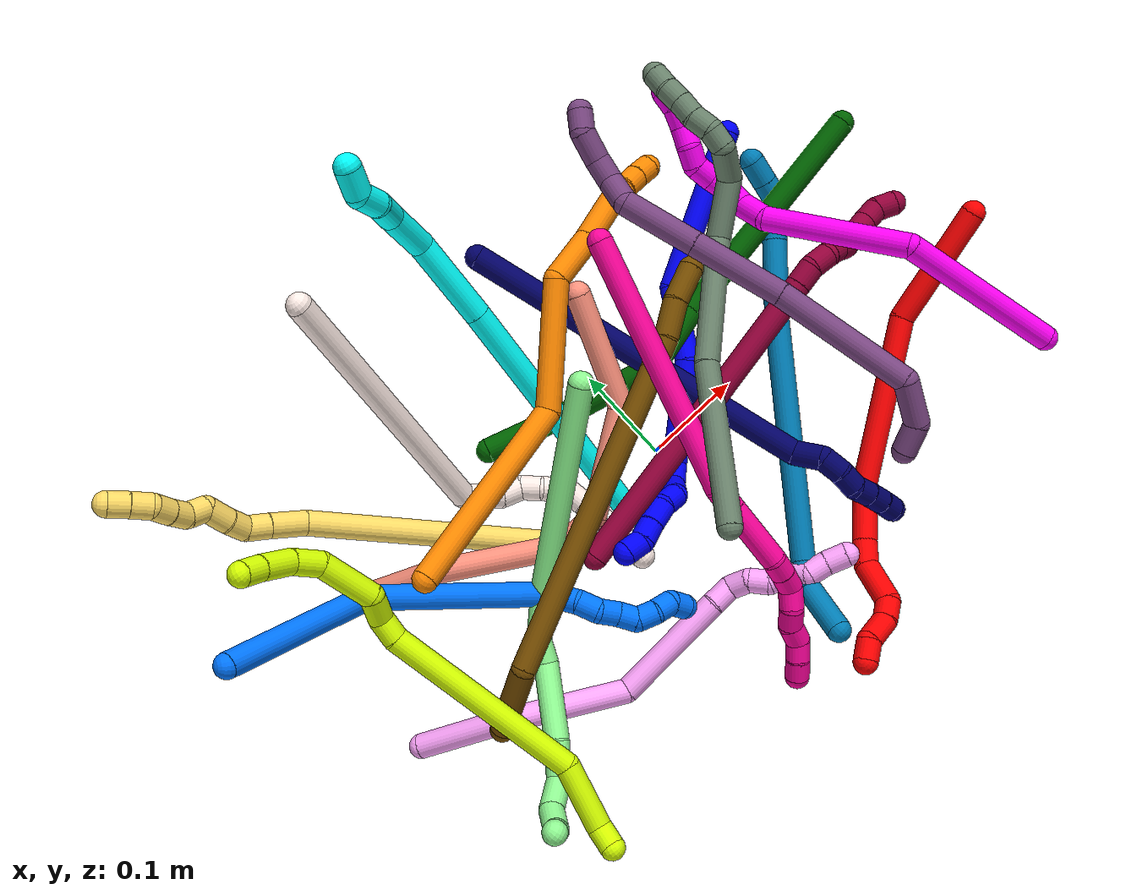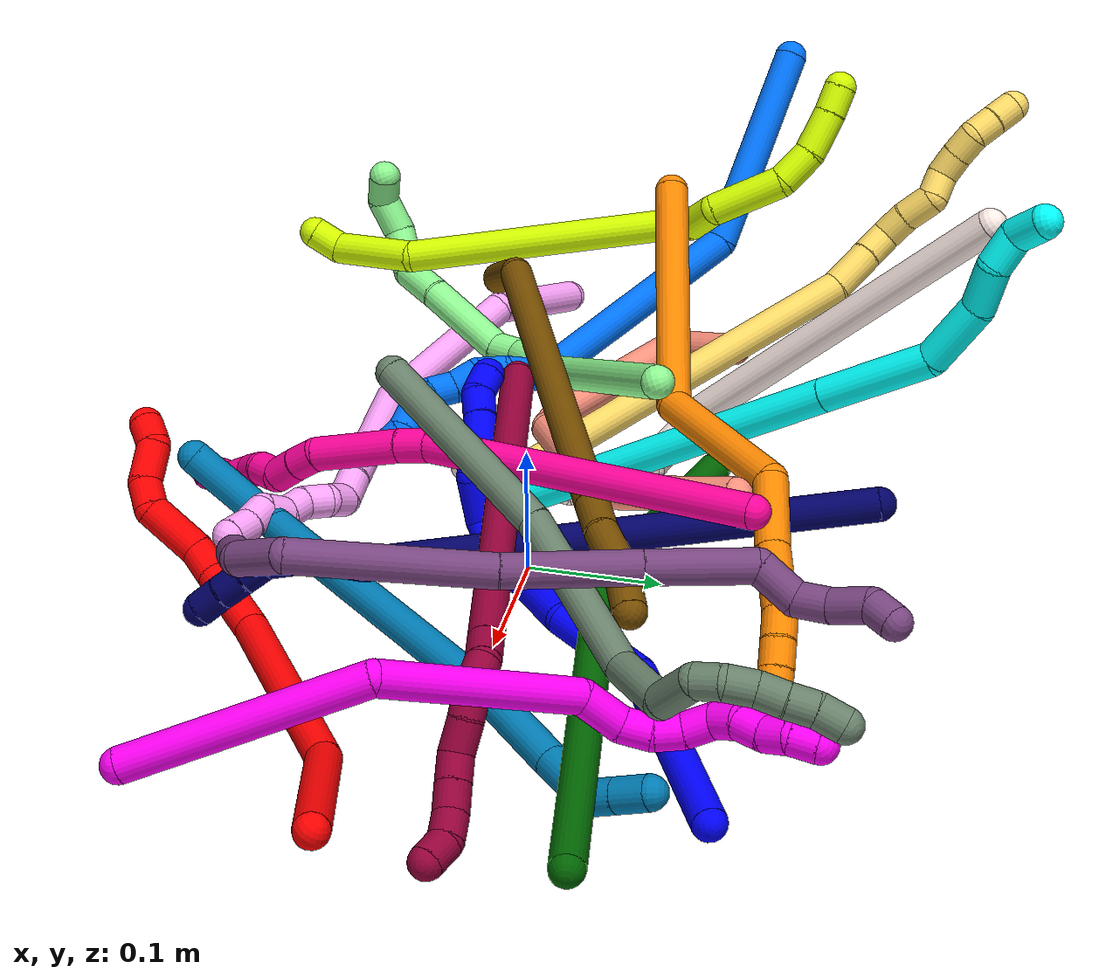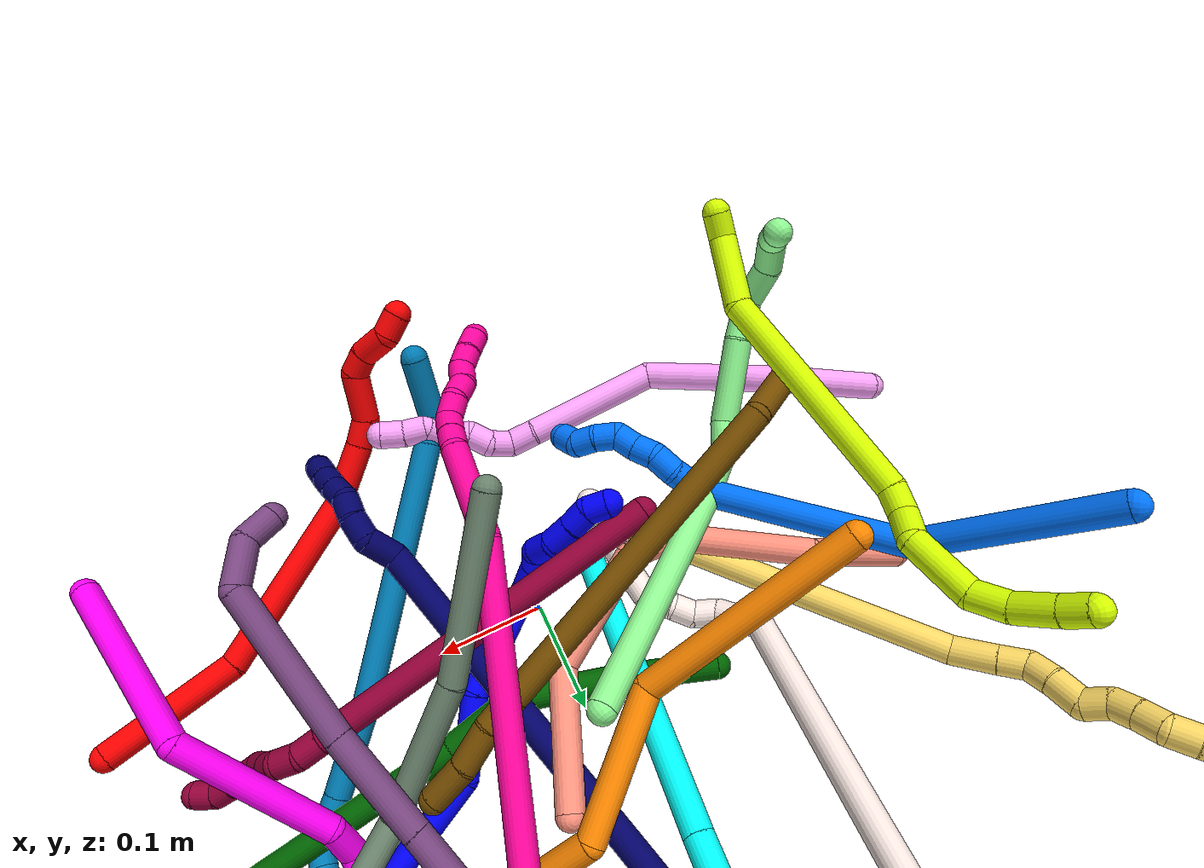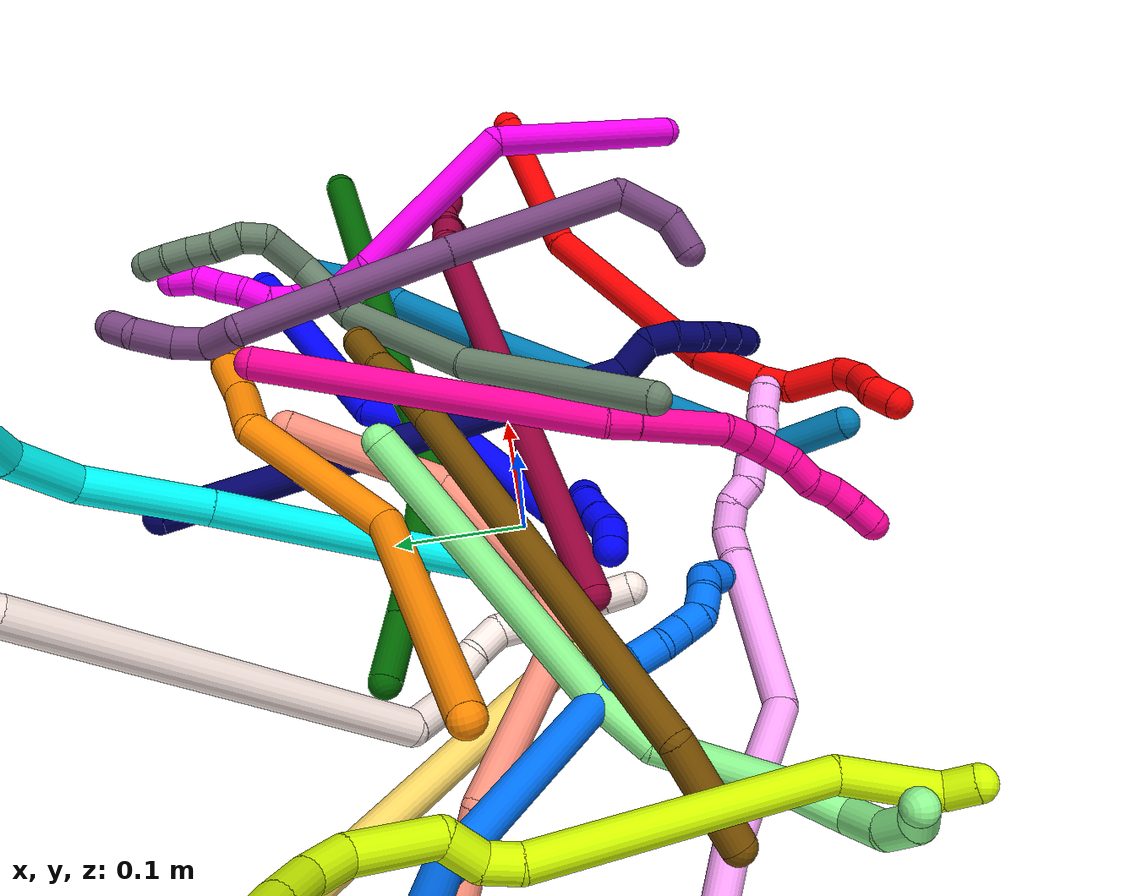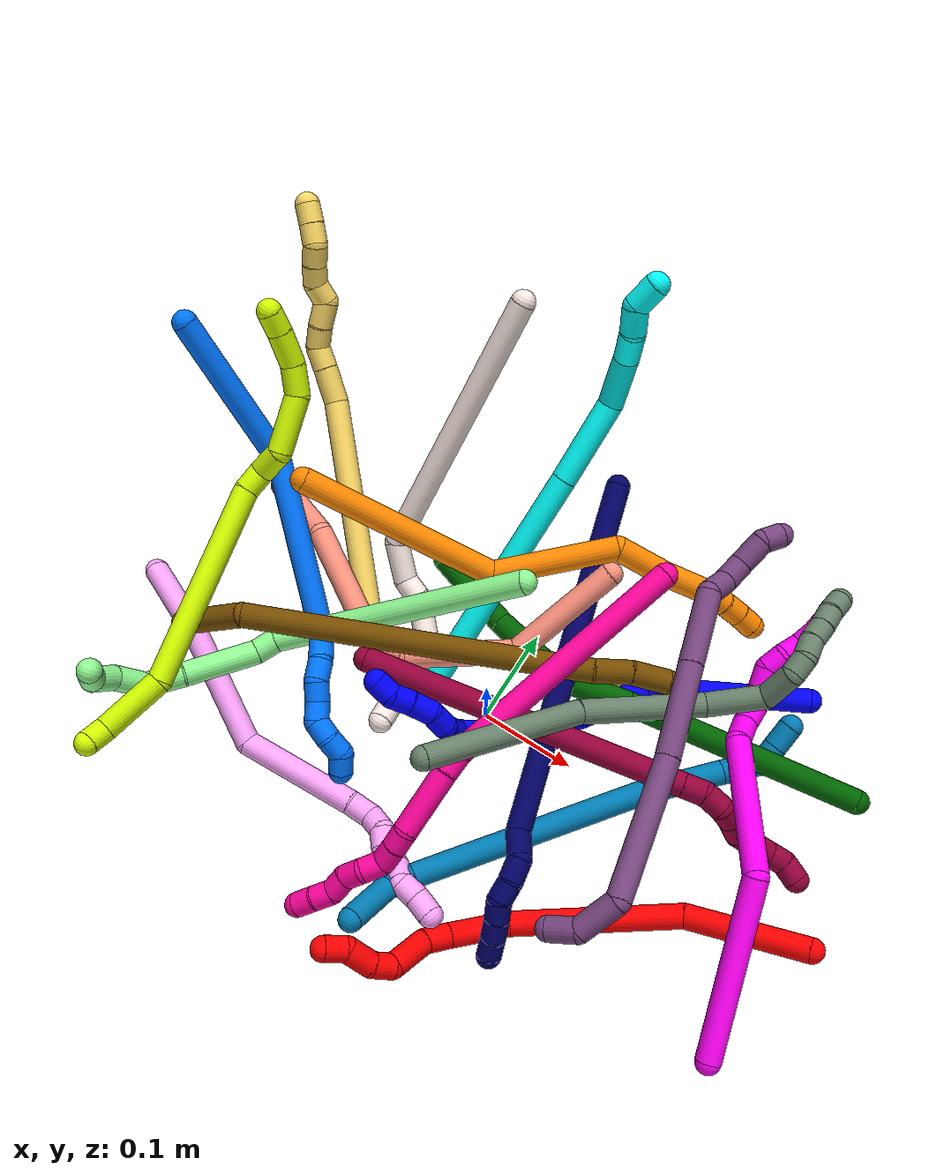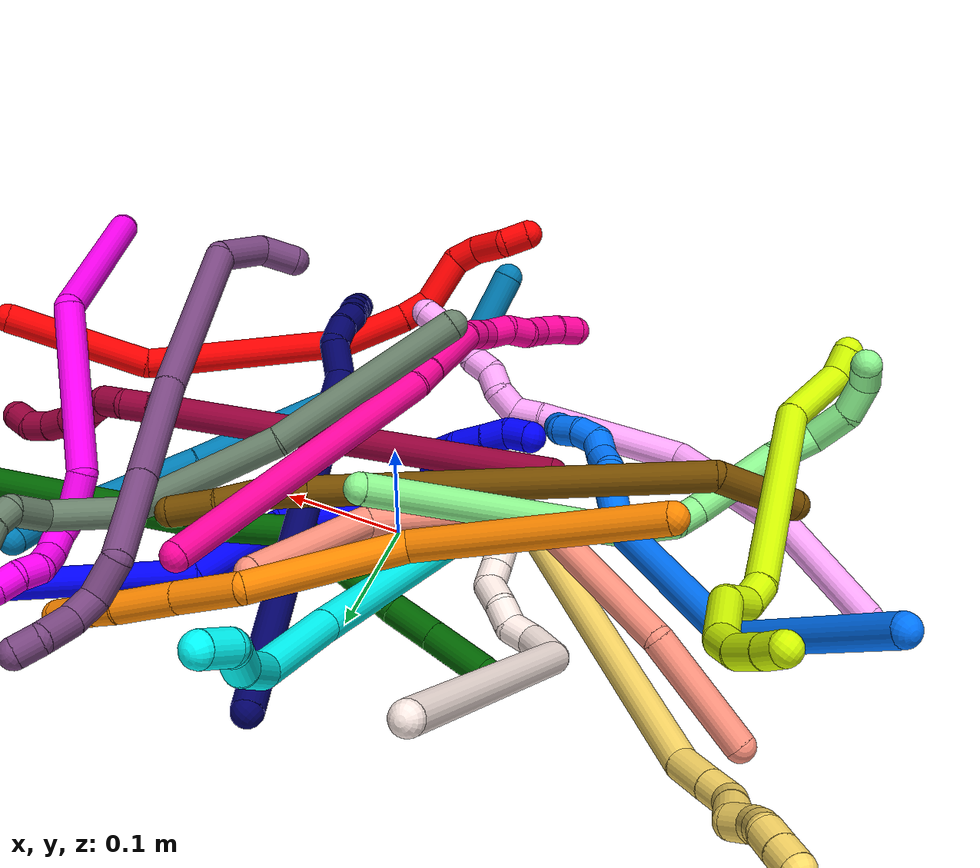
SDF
<sdf version="1.7">
 <world name="default">
  <plugin name="TubeGeneratorPlugin" filename="libtube_generator_plugin.so"/>
  <model name="photoneo_s_sensor">
   <static>1</static>
   <pose>0 0 2 1.57079 1.57079 3.14159</pose>
   <link name="link">
    <inertial><mass>0.1</mass></inertial>
    <sensor name="sensor" type="depth">
     <update_rate>30</update_rate>
     <camera>
      <horizontal_fov>1.22</horizontal_fov>
      <image><width>1920</width><height>1200</height><format>B8G8R8</format></image>
      <clip><near>0.1</near><far>4</far></clip>
      <depth_camera><output>points</output></depth_camera>
     </camera>
     <plugin name="camera_plugin" filename="libgazebo_ros_depth_camera.so">
      <baseline>0.2</baseline>
      <alwaysOn>1</alwaysOn>
      <updateRate>0.0</updateRate>
      <cameraName>camera_ir</cameraName>
      <imageTopicName>/camera/color/image_raw</imageTopicName>
      <cameraInfoTopicName>/camera/color/camera_info</cameraInfoTopicName>
      <depthImageTopicName>/camera/depth/image_raw</depthImageTopicName>
      <depthImageCameraInfoTopicName>/camera/depth/camera_info</depthImageCameraInfoTopicName>
      <pointCloudTopicName>/camera/depth/points</pointCloudTopicName>
      <frameName>fr_optical</frameName>
      <pointCloudCutoff>0.1</pointCloudCutoff>
      <pointCloudCutoffMax>2.0</pointCloudCutoffMax>
      <distortionK1>0</distortionK1>
      <distortionK2>0</distortionK2>
      <distortionK3>0</distortionK3>
      <distortionT1>0</distortionT1>
      <distortionT2>0</distortionT2>
      <CxPrime>0</CxPrime>
      <Cx>0</Cx>
      <Cy>0</Cy>
      <focalLength>0</focalLength>
      <hackBaseline>0</hackBaseline>
     </plugin>
    </sensor>
   </link>
  </model>
  <gravity>0 0 -9.8</gravity>
  <magnetic_field>6e-06 2.3e-05 -4.2e-05</magnetic_field>
  <atmosphere type="adiabatic"/>
  <physics name="default_physics" default="0" type="ode">
   <max_step_size>0.003</max_step_size>
   <real_time_factor>1</real_time_factor>
   <real_time_update_rate>1000</real_time_update_rate>
   <max_contacts>10000</max_contacts>
   <ode>
    <solver>
     <type>quick</type>
     <iters>100</iters>
     <sor>1.3</sor>
     <use_dynamic_moi_rescaling>0</use_dynamic_moi_rescaling>
    </solver>
    <constraints>
     <contact_max_correcting_vel>0</contact_max_correcting_vel>
     <contact_surface_layer>0.001</contact_surface_layer>
     <cfm>0</cfm>
     <erp>0.2</erp>
    </constraints>
   </ode>
  </physics>
  <scene><ambient>0.4 0.4 0.4 1</ambient><background>0.7 0.7 0.7 1</background><shadows>0</shadows></scene>
  <audio><device>default</device></audio>
  <spherical_coordinates>
   <surface_model>EARTH_WGS84</surface_model>
   <latitude_deg>0</latitude_deg>
   <longitude_deg>0</longitude_deg>
   <elevation>0</elevation>
   <heading_deg>0</heading_deg>
  </spherical_coordinates>
  <model name="bin">
   <static>1</static>
   <link name="bottom">
    <collision name="collision-bottom">
     <pose>0 0 -0.01 0 -0 0</pose>
     <geometry><box><size>0.8 0.6 0.02</size></box></geometry>
     <surface>
      <friction><ode><mu>100</mu><mu2>100</mu2></ode></friction>
      <contact><collide_bitmask>65535</collide_bitmask></contact>
     </surface>
    </collision>
   </link>
   <link name="west_wall">
    <collision name="collision-west_wall">
     <pose>-0.41 0 0.1 0 -0 0</pose>
     <geometry><box><size>0.02 0.6 0.2</size></box></geometry>
     <surface>
      <friction><ode><mu>100</mu><mu2>100</mu2></ode></friction>
      <contact><collide_bitmask>65535</collide_bitmask></contact>
     </surface>
    </collision>
   </link>
   <link name="east_wall">
    <collision name="collision-east_wall">
     <pose>0.41 0 0.1 0 -0 0</pose>
     <geometry><box><size>0.02 0.6 0.2</size></box></geometry>
     <surface>
      <friction><ode><mu>100</mu><mu2>100</mu2></ode></friction>
      <contact><collide_bitmask>65535</collide_bitmask></contact>
     </surface>
    </collision>
   </link>
   <link name="south_wall">
    <collision name="collision-south_wall">
     <pose>0 -0.31 0.1 0 -0 0</pose>
     <geometry><box><size>0.8 0.02 0.2</size></box></geometry>
     <surface>
      <friction><ode><mu>100</mu><mu2>100</mu2></ode></friction>
      <contact><collide_bitmask>65535</collide_bitmask></contact>
     </surface>
    </collision>
   </link>
   <link name="north_wall">
    <collision name="collision-north_wall">
     <pose>0 0.31 0.1 0 -0 0</pose>
     <geometry><box><size>0.8 0.02 0.2</size></box></geometry>
     <surface>
      <friction><ode><mu>100</mu><mu2>100</mu2></ode></friction>
      <contact><collide_bitmask>65535</collide_bitmask></contact>
     </surface>
    </collision>
   </link>
  </model>
  <model name="1">
   <static>0</static>
   <link name="1">
    <collision name="collision-cylinder-e_1_1_4">
     <pose>-0.035266 -0.025916 -0.07158 2.79422 -0.433823 -1.79682</pose>
     <geometry><cylinder><radius>0.0125</radius><length>0.167797</length></cylinder></geometry>
     <surface>
      <friction><ode><mu>1.16</mu><mu2>1.16</mu2><slip1>0</slip1><slip2>0</slip2></ode></friction>
      <contact><ode><kp>1e+06</kp><kd>1</kd><max_vel>0</max_vel><min_depth>0.001</min_depth></ode></contact>
     </surface>
    </collision>
    <visual name="visual-cylinder-e_1_1_4">
     <pose>-0.035266 -0.025916 -0.07158 2.79422 -0.433823 -1.79682</pose>
     <geometry><cylinder><radius>0.0125</radius><length>0.167797</length></cylinder></geometry>
     <material><ambient>0 0 1 1</ambient></material>
    </visual>
    <collision name="collision-cylinder-e_2_4_5">
     <pose>-0.072046 -0.077847 -0.17126 2.39471 -0.039508 -0.100757</pose>
     <geometry><cylinder><radius>0.0125</radius><length>0.076648</length></cylinder></geometry>
     <surface>
      <friction><ode><mu>1.16</mu><mu2>1.16</mu2><slip1>0</slip1><slip2>0</slip2></ode></friction>
      <contact><ode><kp>1e+06</kp><kd>1</kd><max_vel>0</max_vel><min_depth>0.001</min_depth></ode></contact>
     </surface>
    </collision>
    <visual name="visual-cylinder-e_2_4_5">
     <pose>-0.072046 -0.077847 -0.17126 2.39471 -0.039508 -0.100757</pose>
     <geometry><cylinder><radius>0.0125</radius><length>0.076648</length></cylinder></geometry>
     <material><ambient>0 0 1 1</ambient></material>
    </visual>
    <collision name="collision-cylinder-e_3_5_6">
     <pose>-0.084686 -0.124403 -0.246896 2.73371 -0.211635 -0.948889</pose>
     <geometry><cylinder><radius>0.0125</radius><length>0.105931</length></cylinder></geometry>
     <surface>
      <friction><ode><mu>1.16</mu><mu2>1.16</mu2><slip1>0</slip1><slip2>0</slip2></ode></friction>
      <contact><ode><kp>1e+06</kp><kd>1</kd><max_vel>0</max_vel><min_depth>0.001</min_depth></ode></contact>
     </surface>
    </collision>
    <visual name="visual-cylinder-e_3_5_6">
     <pose>-0.084686 -0.124403 -0.246896 2.73371 -0.211635 -0.948889</pose>
     <geometry><cylinder><radius>0.0125</radius><length>0.105931</length></cylinder></geometry>
     <material><ambient>0 0 1 1</ambient></material>
    </visual>
    <collision name="collision-cylinder-e_4_6_7">
     <pose>-0.102156 -0.155065 -0.300204 2.08906 -0.4986 -0.826111</pose>
     <geometry><cylinder><radius>0.0125</radius><length>0.026534</length></cylinder></geometry>
     <surface>
      <friction><ode><mu>1.16</mu><mu2>1.16</mu2><slip1>0</slip1><slip2>0</slip2></ode></friction>
      <contact><ode><kp>1e+06</kp><kd>1</kd><max_vel>0</max_vel><min_depth>0.001</min_depth></ode></contact>
     </surface>
    </collision>
    <visual name="visual-cylinder-e_4_6_7">
     <pose>-0.102156 -0.155065 -0.300204 2.08906 -0.4986 -0.826111</pose>
     <geometry><cylinder><radius>0.0125</radius><length>0.026534</length></cylinder></geometry>
     <material><ambient>0 0 1 1</ambient></material>
    </visual>
    <collision name="collision-cylinder-e_5_7_8">
     <pose>-0.117259 -0.179723 -0.301734 1.28689 -0.524422 -0.397232</pose>
     <geometry><cylinder><radius>0.0125</radius><length>0.034985</length></cylinder></geometry>
     <surface>
      <friction><ode><mu>1.16</mu><mu2>1.16</mu2><slip1>0</slip1><slip2>0</slip2></ode></friction>
      <contact><ode><kp>1e+06</kp><kd>1</kd><max_vel>0</max_vel><min_depth>0.001</min_depth></ode></contact>
     </surface>
    </collision>
    <visual name="visual-cylinder-e_5_7_8">
     <pose>-0.117259 -0.179723 -0.301734 1.28689 -0.524422 -0.397232</pose>
     <geometry><cylinder><radius>0.0125</radius><length>0.034985</length></cylinder></geometry>
     <material><ambient>0 0 1 1</ambient></material>
    </visual>
    <collision name="collision-cylinder-e_6_8_9">
     <pose>-0.13614 -0.199336 -0.298403 1.74811 -1.09952 -1.26421</pose>
     <geometry><cylinder><radius>0.0125</radius><length>0.02272</length></cylinder></geometry>
     <surface>
      <friction><ode><mu>1.16</mu><mu2>1.16</mu2><slip1>0</slip1><slip2>0</slip2></ode></friction>
      <contact><ode><kp>1e+06</kp><kd>1</kd><max_vel>0</max_vel><min_depth>0.001</min_depth></ode></contact>
     </surface>
    </collision>
    <visual name="visual-cylinder-e_6_8_9">
     <pose>-0.13614 -0.199336 -0.298403 1.74811 -1.09952 -1.26421</pose>
     <geometry><cylinder><radius>0.0125</radius><length>0.02272</length></cylinder></geometry>
     <material><ambient>0 0 1 1</ambient></material>
    </visual>
    <collision name="collision-cylinder-e_7_9_10">
     <pose>-0.155674 -0.210135 -0.304861 2.3408 -0.868168 -1.66165</pose>
     <geometry><cylinder><radius>0.0125</radius><length>0.024669</length></cylinder></geometry>
     <surface>
      <friction><ode><mu>1.16</mu><mu2>1.16</mu2><slip1>0</slip1><slip2>0</slip2></ode></friction>
      <contact><ode><kp>1e+06</kp><kd>1</kd><max_vel>0</max_vel><min_depth>0.001</min_depth></ode></contact>
     </surface>
    </collision>
    <visual name="visual-cylinder-e_7_9_10">
     <pose>-0.155674 -0.210135 -0.304861 2.3408 -0.868168 -1.66165</pose>
     <geometry><cylinder><radius>0.0125</radius><length>0.024669</length></cylinder></geometry>
     <material><ambient>0 0 1 1</ambient></material>
    </visual>
    <collision name="collision-cylinder-e_8_10_11">
     <pose>-0.172343 -0.221066 -0.315635 2.35766 -0.777085 -1.56107</pose>
     <geometry><cylinder><radius>0.0125</radius><length>0.020695</length></cylinder></geometry>
     <surface>
      <friction><ode><mu>1.16</mu><mu2>1.16</mu2><slip1>0</slip1><slip2>0</slip2></ode></friction>
      <contact><ode><kp>1e+06</kp><kd>1</kd><max_vel>0</max_vel><min_depth>0.001</min_depth></ode></contact>
     </surface>
    </collision>
    <visual name="visual-cylinder-e_8_10_11">
     <pose>-0.172343 -0.221066 -0.315635 2.35766 -0.777085 -1.56107</pose>
     <geometry><cylinder><radius>0.0125</radius><length>0.020695</length></cylinder></geometry>
     <material><ambient>0 0 1 1</ambient></material>
    </visual>
    <collision name="collision-cylinder-e_9_11_2">
     <pose>-0.188628 -0.227249 -0.325069 2.9142 -1.1244 -2.783</pose>
     <geometry><cylinder><radius>0.0125</radius><length>0.02002</length></cylinder></geometry>
     <surface>
      <friction><ode><mu>1.16</mu><mu2>1.16</mu2><slip1>0</slip1><slip2>0</slip2></ode></friction>
      <contact><ode><kp>1e+06</kp><kd>1</kd><max_vel>0</max_vel><min_depth>0.001</min_depth></ode></contact>
     </surface>
    </collision>
    <visual name="visual-cylinder-e_9_11_2">
     <pose>-0.188628 -0.227249 -0.325069 2.9142 -1.1244 -2.783</pose>
     <geometry><cylinder><radius>0.0125</radius><length>0.02002</length></cylinder></geometry>
     <material><ambient>0 0 1 1</ambient></material>
    </visual>
    <collision name="collision-sphere-2">
     <pose>-0.197657 -0.228224 -0.329279 0 -0 0</pose>
     <geometry><sphere><radius>0.0125</radius></sphere></geometry>
     <surface>
      <friction><ode><mu>1.16</mu><mu2>1.16</mu2><slip1>0</slip1><slip2>0</slip2></ode></friction>
      <contact><ode><kp>1e+06</kp><kd>1</kd><max_vel>0</max_vel><min_depth>0.001</min_depth></ode></contact>
     </surface>
    </collision>
    <visual name="visual-sphere-2">
     <pose>-0.197657 -0.228224 -0.329279 0 -0 0</pose>
     <geometry><sphere><radius>0.0125</radius></sphere></geometry>
     <material><ambient>0 0 1 1</ambient></material>
    </visual>
    <collision name="collision-sphere-11">
     <pose>-0.179599 -0.226275 -0.320859 0 -0 0</pose>
     <geometry><sphere><radius>0.0125</radius></sphere></geometry>
     <surface>
      <friction><ode><mu>1.16</mu><mu2>1.16</mu2><slip1>0</slip1><slip2>0</slip2></ode></friction>
      <contact><ode><kp>1e+06</kp><kd>1</kd><max_vel>0</max_vel><min_depth>0.001</min_depth></ode></contact>
     </surface>
    </collision>
    <visual name="visual-sphere-11">
     <pose>-0.179599 -0.226275 -0.320859 0 -0 0</pose>
     <geometry><sphere><radius>0.0125</radius></sphere></geometry>
     <material><ambient>0 0 1 1</ambient></material>
    </visual>
    <collision name="collision-sphere-10">
     <pose>-0.165087 -0.215857 -0.31041 0 -0 0</pose>
     <geometry><sphere><radius>0.0125</radius></sphere></geometry>
     <surface>
      <friction><ode><mu>1.16</mu><mu2>1.16</mu2><slip1>0</slip1><slip2>0</slip2></ode></friction>
      <contact><ode><kp>1e+06</kp><kd>1</kd><max_vel>0</max_vel><min_depth>0.001</min_depth></ode></contact>
     </surface>
    </collision>
    <visual name="visual-sphere-10">
     <pose>-0.165087 -0.215857 -0.31041 0 -0 0</pose>
     <geometry><sphere><radius>0.0125</radius></sphere></geometry>
     <material><ambient>0 0 1 1</ambient></material>
    </visual>
    <collision name="collision-sphere-9">
     <pose>-0.146261 -0.204412 -0.299312 0 -0 0</pose>
     <geometry><sphere><radius>0.0125</radius></sphere></geometry>
     <surface>
      <friction><ode><mu>1.16</mu><mu2>1.16</mu2><slip1>0</slip1><slip2>0</slip2></ode></friction>
      <contact><ode><kp>1e+06</kp><kd>1</kd><max_vel>0</max_vel><min_depth>0.001</min_depth></ode></contact>
     </surface>
    </collision>
    <visual name="visual-sphere-9">
     <pose>-0.146261 -0.204412 -0.299312 0 -0 0</pose>
     <geometry><sphere><radius>0.0125</radius></sphere></geometry>
     <material><ambient>0 0 1 1</ambient></material>
    </visual>
    <collision name="collision-sphere-4">
     <pose>-0.070532 -0.051831 -0.143159 0 -0 0</pose>
     <geometry><sphere><radius>0.0125</radius></sphere></geometry>
     <surface>
      <friction><ode><mu>1.16</mu><mu2>1.16</mu2><slip1>0</slip1><slip2>0</slip2></ode></friction>
      <contact><ode><kp>1e+06</kp><kd>1</kd><max_vel>0</max_vel><min_depth>0.001</min_depth></ode></contact>
     </surface>
    </collision>
    <visual name="visual-sphere-4">
     <pose>-0.070532 -0.051831 -0.143159 0 -0 0</pose>
     <geometry><sphere><radius>0.0125</radius></sphere></geometry>
     <material><ambient>0 0 1 1</ambient></material>
    </visual>
    <collision name="collision-sphere-1">
     <geometry><sphere><radius>0.0125</radius></sphere></geometry>
     <surface>
      <friction><ode><mu>1.16</mu><mu2>1.16</mu2><slip1>0</slip1><slip2>0</slip2></ode></friction>
      <contact><ode><kp>1e+06</kp><kd>1</kd><max_vel>0</max_vel><min_depth>0.001</min_depth></ode></contact>
     </surface>
    </collision>
    <visual name="visual-sphere-1">
     <geometry><sphere><radius>0.0125</radius></sphere></geometry>
     <material><ambient>0 0 1 1</ambient></material>
    </visual>
    <collision name="collision-sphere-8">
     <pose>-0.126018 -0.194259 -0.297493 0 -0 0</pose>
     <geometry><sphere><radius>0.0125</radius></sphere></geometry>
     <surface>
      <friction><ode><mu>1.16</mu><mu2>1.16</mu2><slip1>0</slip1><slip2>0</slip2></ode></friction>
      <contact><ode><kp>1e+06</kp><kd>1</kd><max_vel>0</max_vel><min_depth>0.001</min_depth></ode></contact>
     </surface>
    </collision>
    <visual name="visual-sphere-8">
     <pose>-0.126018 -0.194259 -0.297493 0 -0 0</pose>
     <geometry><sphere><radius>0.0125</radius></sphere></geometry>
     <material><ambient>0 0 1 1</ambient></material>
    </visual>
    <collision name="collision-sphere-5">
     <pose>-0.07356 -0.103862 -0.19936 0 -0 0</pose>
     <geometry><sphere><radius>0.0125</radius></sphere></geometry>
     <surface>
      <friction><ode><mu>1.16</mu><mu2>1.16</mu2><slip1>0</slip1><slip2>0</slip2></ode></friction>
      <contact><ode><kp>1e+06</kp><kd>1</kd><max_vel>0</max_vel><min_depth>0.001</min_depth></ode></contact>
     </surface>
    </collision>
    <visual name="visual-sphere-5">
     <pose>-0.07356 -0.103862 -0.19936 0 -0 0</pose>
     <geometry><sphere><radius>0.0125</radius></sphere></geometry>
     <material><ambient>0 0 1 1</ambient></material>
    </visual>
    <collision name="collision-sphere-6">
     <pose>-0.095812 -0.144944 -0.294431 0 -0 0</pose>
     <geometry><sphere><radius>0.0125</radius></sphere></geometry>
     <surface>
      <friction><ode><mu>1.16</mu><mu2>1.16</mu2><slip1>0</slip1><slip2>0</slip2></ode></friction>
      <contact><ode><kp>1e+06</kp><kd>1</kd><max_vel>0</max_vel><min_depth>0.001</min_depth></ode></contact>
     </surface>
    </collision>
    <visual name="visual-sphere-6">
     <pose>-0.095812 -0.144944 -0.294431 0 -0 0</pose>
     <geometry><sphere><radius>0.0125</radius></sphere></geometry>
     <material><ambient>0 0 1 1</ambient></material>
    </visual>
    <collision name="collision-sphere-7">
     <pose>-0.1085 -0.165187 -0.305976 0 -0 0</pose>
     <geometry><sphere><radius>0.0125</radius></sphere></geometry>
     <surface>
      <friction><ode><mu>1.16</mu><mu2>1.16</mu2><slip1>0</slip1><slip2>0</slip2></ode></friction>
      <contact><ode><kp>1e+06</kp><kd>1</kd><max_vel>0</max_vel><min_depth>0.001</min_depth></ode></contact>
     </surface>
    </collision>
    <visual name="visual-sphere-7">
     <pose>-0.1085 -0.165187 -0.305976 0 -0 0</pose>
     <geometry><sphere><radius>0.0125</radius></sphere></geometry>
     <material><ambient>0 0 1 1</ambient></material>
    </visual>
    <inertial>
     <pose>-0.083 -0.105466 -0.194308 0 -0 0</pose>
     <mass>0.5</mass>
     <inertia>
      <ixx>-0.00044</ixx>
      <ixy>0</ixy>
      <ixz>0</ixz>
      <iyy>-0.000395</iyy>
      <iyz>0</iyz>
      <izz>0.000375</izz>
     </inertia>
    </inertial>
   </link>
   <pose>0.272773 0.188563 0.014148 -0.938547 0.522802 -0.572443</pose>
  </model>
  <model name="2">
   <static>0</static>
   <link name="2">
    <collision name="collision-cylinder-e_1_1_4">
     <pose>-0.055635 -0.022321 0.016636 0.93031 -1.10685 -0.601352</pose>
     <geometry><cylinder><radius>0.0125</radius><length>0.124423</length></cylinder></geometry>
     <surface>
      <friction><ode><mu>1.16</mu><mu2>1.16</mu2><slip1>0</slip1><slip2>0</slip2></ode></friction>
      <contact><ode><kp>1e+06</kp><kd>1</kd><max_vel>0</max_vel><min_depth>0.001</min_depth></ode></contact>
     </surface>
    </collision>
    <visual name="visual-cylinder-e_1_1_4">
     <pose>-0.055635 -0.022321 0.016636 0.93031 -1.10685 -0.601352</pose>
     <geometry><cylinder><radius>0.0125</radius><length>0.124423</length></cylinder></geometry>
     <material><ambient>1 0 0 1</ambient></material>
    </visual>
    <collision name="collision-cylinder-e_2_4_5">
     <pose>-0.194416 -0.03968 0.05244 -0.253343 -1.33701 0.200499</pose>
     <geometry><cylinder><radius>0.0125</radius><length>0.170942</length></cylinder></geometry>
     <surface>
      <friction><ode><mu>1.16</mu><mu2>1.16</mu2><slip1>0</slip1><slip2>0</slip2></ode></friction>
      <contact><ode><kp>1e+06</kp><kd>1</kd><max_vel>0</max_vel><min_depth>0.001</min_depth></ode></contact>
     </surface>
    </collision>
    <visual name="visual-cylinder-e_2_4_5">
     <pose>-0.194416 -0.03968 0.05244 -0.253343 -1.33701 0.200499</pose>
     <geometry><cylinder><radius>0.0125</radius><length>0.170942</length></cylinder></geometry>
     <material><ambient>1 0 0 1</ambient></material>
    </visual>
    <collision name="collision-cylinder-e_3_5_6">
     <pose>-0.30581 -0.025194 0.07443 -1.28278 -1.23272 0.973133</pose>
     <geometry><cylinder><radius>0.0125</radius><length>0.059887</length></cylinder></geometry>
     <surface>
      <friction><ode><mu>1.16</mu><mu2>1.16</mu2><slip1>0</slip1><slip2>0</slip2></ode></friction>
      <contact><ode><kp>1e+06</kp><kd>1</kd><max_vel>0</max_vel><min_depth>0.001</min_depth></ode></contact>
     </surface>
    </collision>
    <visual name="visual-cylinder-e_3_5_6">
     <pose>-0.30581 -0.025194 0.07443 -1.28278 -1.23272 0.973133</pose>
     <geometry><cylinder><radius>0.0125</radius><length>0.059887</length></cylinder></geometry>
     <material><ambient>1 0 0 1</ambient></material>
    </visual>
    <collision name="collision-cylinder-e_4_6_7">
     <pose>-0.345843 -0.010176 0.076973 -1.62137 -1.13391 1.18023</pose>
     <geometry><cylinder><radius>0.0125</radius><length>0.02601</length></cylinder></geometry>
     <surface>
      <friction><ode><mu>1.16</mu><mu2>1.16</mu2><slip1>0</slip1><slip2>0</slip2></ode></friction>
      <contact><ode><kp>1e+06</kp><kd>1</kd><max_vel>0</max_vel><min_depth>0.001</min_depth></ode></contact>
     </surface>
    </collision>
    <visual name="visual-cylinder-e_4_6_7">
     <pose>-0.345843 -0.010176 0.076973 -1.62137 -1.13391 1.18023</pose>
     <geometry><cylinder><radius>0.0125</radius><length>0.02601</length></cylinder></geometry>
     <material><ambient>1 0 0 1</ambient></material>
    </visual>
    <collision name="collision-cylinder-e_5_7_8">
     <pose>-0.37137 0.01285 0.074939 -1.67061 -0.66249 0.726431</pose>
     <geometry><cylinder><radius>0.0125</radius><length>0.04469</length></cylinder></geometry>
     <surface>
      <friction><ode><mu>1.16</mu><mu2>1.16</mu2><slip1>0</slip1><slip2>0</slip2></ode></friction>
      <contact><ode><kp>1e+06</kp><kd>1</kd><max_vel>0</max_vel><min_depth>0.001</min_depth></ode></contact>
     </surface>
    </collision>
    <visual name="visual-cylinder-e_5_7_8">
     <pose>-0.37137 0.01285 0.074939 -1.67061 -0.66249 0.726431</pose>
     <geometry><cylinder><radius>0.0125</radius><length>0.04469</length></cylinder></geometry>
     <material><ambient>1 0 0 1</ambient></material>
    </visual>
    <collision name="collision-cylinder-e_6_8_9">
     <pose>-0.39512 0.033285 0.069878 -2.42054 -1.15646 2.09394</pose>
     <geometry><cylinder><radius>0.0125</radius><length>0.021861</length></cylinder></geometry>
     <surface>
      <friction><ode><mu>1.16</mu><mu2>1.16</mu2><slip1>0</slip1><slip2>0</slip2></ode></friction>
      <contact><ode><kp>1e+06</kp><kd>1</kd><max_vel>0</max_vel><min_depth>0.001</min_depth></ode></contact>
     </surface>
    </collision>
    <visual name="visual-cylinder-e_6_8_9">
     <pose>-0.39512 0.033285 0.069878 -2.42054 -1.15646 2.09394</pose>
     <geometry><cylinder><radius>0.0125</radius><length>0.021861</length></cylinder></geometry>
     <material><ambient>1 0 0 1</ambient></material>
    </visual>
    <collision name="collision-cylinder-e_7_9_10">
     <pose>-0.417769 0.035094 0.058238 3.01088 -0.984006 -2.89856</pose>
     <geometry><cylinder><radius>0.0125</radius><length>0.030367</length></cylinder></geometry>
     <surface>
      <friction><ode><mu>1.16</mu><mu2>1.16</mu2><slip1>0</slip1><slip2>0</slip2></ode></friction>
      <contact><ode><kp>1e+06</kp><kd>1</kd><max_vel>0</max_vel><min_depth>0.001</min_depth></ode></contact>
     </surface>
    </collision>
    <visual name="visual-cylinder-e_7_9_10">
     <pose>-0.417769 0.035094 0.058238 3.01088 -0.984006 -2.89856</pose>
     <geometry><cylinder><radius>0.0125</radius><length>0.030367</length></cylinder></geometry>
     <material><ambient>1 0 0 1</ambient></material>
    </visual>
    <collision name="collision-cylinder-e_8_10_2">
     <pose>-0.441021 0.036352 0.048924 -1.96486 -1.33502 1.73673</pose>
     <geometry><cylinder><radius>0.0125</radius><length>0.02182</length></cylinder></geometry>
     <surface>
      <friction><ode><mu>1.16</mu><mu2>1.16</mu2><slip1>0</slip1><slip2>0</slip2></ode></friction>
      <contact><ode><kp>1e+06</kp><kd>1</kd><max_vel>0</max_vel><min_depth>0.001</min_depth></ode></contact>
     </surface>
    </collision>
    <visual name="visual-cylinder-e_8_10_2">
     <pose>-0.441021 0.036352 0.048924 -1.96486 -1.33502 1.73673</pose>
     <geometry><cylinder><radius>0.0125</radius><length>0.02182</length></cylinder></geometry>
     <material><ambient>1 0 0 1</ambient></material>
    </visual>
    <collision name="collision-sphere-2">
     <pose>-0.451629 0.038705 0.047946 0 -0 0</pose>
     <geometry><sphere><radius>0.0125</radius></sphere></geometry>
     <surface>
      <friction><ode><mu>1.16</mu><mu2>1.16</mu2><slip1>0</slip1><slip2>0</slip2></ode></friction>
      <contact><ode><kp>1e+06</kp><kd>1</kd><max_vel>0</max_vel><min_depth>0.001</min_depth></ode></contact>
     </surface>
    </collision>
    <visual name="visual-sphere-2">
     <pose>-0.451629 0.038705 0.047946 0 -0 0</pose>
     <geometry><sphere><radius>0.0125</radius></sphere></geometry>
     <material><ambient>1 0 0 1</ambient></material>
    </visual>
    <collision name="collision-sphere-10">
     <pose>-0.430413 0.033999 0.049903 0 -0 0</pose>
     <geometry><sphere><radius>0.0125</radius></sphere></geometry>
     <surface>
      <friction><ode><mu>1.16</mu><mu2>1.16</mu2><slip1>0</slip1><slip2>0</slip2></ode></friction>
      <contact><ode><kp>1e+06</kp><kd>1</kd><max_vel>0</max_vel><min_depth>0.001</min_depth></ode></contact>
     </surface>
    </collision>
    <visual name="visual-sphere-10">
     <pose>-0.430413 0.033999 0.049903 0 -0 0</pose>
     <geometry><sphere><radius>0.0125</radius></sphere></geometry>
     <material><ambient>1 0 0 1</ambient></material>
    </visual>
    <collision name="collision-sphere-9">
     <pose>-0.405125 0.03619 0.066573 0 -0 0</pose>
     <geometry><sphere><radius>0.0125</radius></sphere></geometry>
     <surface>
      <friction><ode><mu>1.16</mu><mu2>1.16</mu2><slip1>0</slip1><slip2>0</slip2></ode></friction>
      <contact><ode><kp>1e+06</kp><kd>1</kd><max_vel>0</max_vel><min_depth>0.001</min_depth></ode></contact>
     </surface>
    </collision>
    <visual name="visual-sphere-9">
     <pose>-0.405125 0.03619 0.066573 0 -0 0</pose>
     <geometry><sphere><radius>0.0125</radius></sphere></geometry>
     <material><ambient>1 0 0 1</ambient></material>
    </visual>
    <collision name="collision-sphere-4">
     <pose>-0.11127 -0.044642 0.033272 0 -0 0</pose>
     <geometry><sphere><radius>0.0125</radius></sphere></geometry>
     <surface>
      <friction><ode><mu>1.16</mu><mu2>1.16</mu2><slip1>0</slip1><slip2>0</slip2></ode></friction>
      <contact><ode><kp>1e+06</kp><kd>1</kd><max_vel>0</max_vel><min_depth>0.001</min_depth></ode></contact>
     </surface>
    </collision>
    <visual name="visual-sphere-4">
     <pose>-0.11127 -0.044642 0.033272 0 -0 0</pose>
     <geometry><sphere><radius>0.0125</radius></sphere></geometry>
     <material><ambient>1 0 0 1</ambient></material>
    </visual>
    <collision name="collision-sphere-1">
     <geometry><sphere><radius>0.0125</radius></sphere></geometry>
     <surface>
      <friction><ode><mu>1.16</mu><mu2>1.16</mu2><slip1>0</slip1><slip2>0</slip2></ode></friction>
      <contact><ode><kp>1e+06</kp><kd>1</kd><max_vel>0</max_vel><min_depth>0.001</min_depth></ode></contact>
     </surface>
    </collision>
    <visual name="visual-sphere-1">
     <geometry><sphere><radius>0.0125</radius></sphere></geometry>
     <material><ambient>1 0 0 1</ambient></material>
    </visual>
    <collision name="collision-sphere-8">
     <pose>-0.385114 0.03038 0.073184 0 -0 0</pose>
     <geometry><sphere><radius>0.0125</radius></sphere></geometry>
     <surface>
      <friction><ode><mu>1.16</mu><mu2>1.16</mu2><slip1>0</slip1><slip2>0</slip2></ode></friction>
      <contact><ode><kp>1e+06</kp><kd>1</kd><max_vel>0</max_vel><min_depth>0.001</min_depth></ode></contact>
     </surface>
    </collision>
    <visual name="visual-sphere-8">
     <pose>-0.385114 0.03038 0.073184 0 -0 0</pose>
     <geometry><sphere><radius>0.0125</radius></sphere></geometry>
     <material><ambient>1 0 0 1</ambient></material>
    </visual>
    <collision name="collision-sphere-5">
     <pose>-0.277562 -0.034717 0.071609 0 -0 0</pose>
     <geometry><sphere><radius>0.0125</radius></sphere></geometry>
     <surface>
      <friction><ode><mu>1.16</mu><mu2>1.16</mu2><slip1>0</slip1><slip2>0</slip2></ode></friction>
      <contact><ode><kp>1e+06</kp><kd>1</kd><max_vel>0</max_vel><min_depth>0.001</min_depth></ode></contact>
     </surface>
    </collision>
    <visual name="visual-sphere-5">
     <pose>-0.277562 -0.034717 0.071609 0 -0 0</pose>
     <geometry><sphere><radius>0.0125</radius></sphere></geometry>
     <material><ambient>1 0 0 1</ambient></material>
    </visual>
    <collision name="collision-sphere-6">
     <pose>-0.334059 -0.015672 0.077251 0 -0 0</pose>
     <geometry><sphere><radius>0.0125</radius></sphere></geometry>
     <surface>
      <friction><ode><mu>1.16</mu><mu2>1.16</mu2><slip1>0</slip1><slip2>0</slip2></ode></friction>
      <contact><ode><kp>1e+06</kp><kd>1</kd><max_vel>0</max_vel><min_depth>0.001</min_depth></ode></contact>
     </surface>
    </collision>
    <visual name="visual-sphere-6">
     <pose>-0.334059 -0.015672 0.077251 0 -0 0</pose>
     <geometry><sphere><radius>0.0125</radius></sphere></geometry>
     <material><ambient>1 0 0 1</ambient></material>
    </visual>
    <collision name="collision-sphere-7">
     <pose>-0.357626 -0.00468 0.076695 0 -0 0</pose>
     <geometry><sphere><radius>0.0125</radius></sphere></geometry>
     <surface>
      <friction><ode><mu>1.16</mu><mu2>1.16</mu2><slip1>0</slip1><slip2>0</slip2></ode></friction>
      <contact><ode><kp>1e+06</kp><kd>1</kd><max_vel>0</max_vel><min_depth>0.001</min_depth></ode></contact>
     </surface>
    </collision>
    <visual name="visual-sphere-7">
     <pose>-0.357626 -0.00468 0.076695 0 -0 0</pose>
     <geometry><sphere><radius>0.0125</radius></sphere></geometry>
     <material><ambient>1 0 0 1</ambient></material>
    </visual>
    <inertial>
     <pose>-0.230019 -0.016346 0.050413 0 -0 0</pose>
     <mass>0.5</mass>
     <inertia>
      <ixx>0.000119</ixx>
      <ixy>0</ixy>
      <ixz>0</ixz>
      <iyy>0.000593</iyy>
      <iyz>0</iyz>
      <izz>0.000616</izz>
     </inertia>
    </inertial>
   </link>
   <pose>0.387628 -0.040756 0.059271 2.6316 0.112532 0.446571</pose>
  </model>
  <model name="3">
   <static>0</static>
   <link name="3">
    <collision name="collision-cylinder-e_1_1_4">
     <pose>0.001081 0.023082 0.136217 -0.167853 0.007823 -0.000658</pose>
     <geometry><cylinder><radius>0.0125</radius><length>0.276325</length></cylinder></geometry>
     <surface>
      <friction><ode><mu>1.16</mu><mu2>1.16</mu2><slip1>0</slip1><slip2>0</slip2></ode></friction>
      <contact><ode><kp>1e+06</kp><kd>1</kd><max_vel>0</max_vel><min_depth>0.001</min_depth></ode></contact>
     </surface>
    </collision>
    <visual name="visual-cylinder-e_1_1_4">
     <pose>0.001081 0.023082 0.136217 -0.167853 0.007823 -0.000658</pose>
     <geometry><cylinder><radius>0.0125</radius><length>0.276325</length></cylinder></geometry>
     <material><ambient>0.003922 1 0.996078 1</ambient></material>
    </visual>
    <collision name="collision-cylinder-e_2_4_5">
     <pose>0.003408 0.054255 0.31452 -0.189957 0.029061 -0.002769</pose>
     <geometry><cylinder><radius>0.0125</radius><length>0.085752</length></cylinder></geometry>
     <surface>
      <friction><ode><mu>1.16</mu><mu2>1.16</mu2><slip1>0</slip1><slip2>0</slip2></ode></friction>
      <contact><ode><kp>1e+06</kp><kd>1</kd><max_vel>0</max_vel><min_depth>0.001</min_depth></ode></contact>
     </surface>
    </collision>
    <visual name="visual-cylinder-e_2_4_5">
     <pose>0.003408 0.054255 0.31452 -0.189957 0.029061 -0.002769</pose>
     <geometry><cylinder><radius>0.0125</radius><length>0.085752</length></cylinder></geometry>
     <material><ambient>0.003922 1 0.996078 1</ambient></material>
    </visual>
    <collision name="collision-cylinder-e_3_5_6">
     <pose>-0.00579 0.070483 0.378477 -0.356143 -0.420816 0.076837</pose>
     <geometry><cylinder><radius>0.0125</radius><length>0.05113</length></cylinder></geometry>
     <surface>
      <friction><ode><mu>1.16</mu><mu2>1.16</mu2><slip1>0</slip1><slip2>0</slip2></ode></friction>
      <contact><ode><kp>1e+06</kp><kd>1</kd><max_vel>0</max_vel><min_depth>0.001</min_depth></ode></contact>
     </surface>
    </collision>
    <visual name="visual-cylinder-e_3_5_6">
     <pose>-0.00579 0.070483 0.378477 -0.356143 -0.420816 0.076837</pose>
     <geometry><cylinder><radius>0.0125</radius><length>0.05113</length></cylinder></geometry>
     <material><ambient>0.003922 1 0.996078 1</ambient></material>
    </visual>
    <collision name="collision-cylinder-e_4_6_7">
     <pose>-0.027916 0.083025 0.411656 -0.371492 -0.766363 0.151208</pose>
     <geometry><cylinder><radius>0.0125</radius><length>0.033691</length></cylinder></geometry>
     <surface>
      <friction><ode><mu>1.16</mu><mu2>1.16</mu2><slip1>0</slip1><slip2>0</slip2></ode></friction>
      <contact><ode><kp>1e+06</kp><kd>1</kd><max_vel>0</max_vel><min_depth>0.001</min_depth></ode></contact>
     </surface>
    </collision>
    <visual name="visual-cylinder-e_4_6_7">
     <pose>-0.027916 0.083025 0.411656 -0.371492 -0.766363 0.151208</pose>
     <geometry><cylinder><radius>0.0125</radius><length>0.033691</length></cylinder></geometry>
     <material><ambient>0.003922 1 0.996078 1</ambient></material>
    </visual>
    <collision name="collision-cylinder-e_5_7_8">
     <pose>-0.045348 0.093932 0.432697 -0.588923 -0.456568 0.140691</pose>
     <geometry><cylinder><radius>0.0125</radius><length>0.026081</length></cylinder></geometry>
     <surface>
      <friction><ode><mu>1.16</mu><mu2>1.16</mu2><slip1>0</slip1><slip2>0</slip2></ode></friction>
      <contact><ode><kp>1e+06</kp><kd>1</kd><max_vel>0</max_vel><min_depth>0.001</min_depth></ode></contact>
     </surface>
    </collision>
    <visual name="visual-cylinder-e_5_7_8">
     <pose>-0.045348 0.093932 0.432697 -0.588923 -0.456568 0.140691</pose>
     <geometry><cylinder><radius>0.0125</radius><length>0.026081</length></cylinder></geometry>
     <material><ambient>0.003922 1 0.996078 1</ambient></material>
    </visual>
    <collision name="collision-cylinder-e_6_8_2">
     <pose>-0.053761 0.099402 0.455635 0.077965 -0.19842 -0.007764</pose>
     <geometry><cylinder><radius>0.0125</radius><length>0.027021</length></cylinder></geometry>
     <surface>
      <friction><ode><mu>1.16</mu><mu2>1.16</mu2><slip1>0</slip1><slip2>0</slip2></ode></friction>
      <contact><ode><kp>1e+06</kp><kd>1</kd><max_vel>0</max_vel><min_depth>0.001</min_depth></ode></contact>
     </surface>
    </collision>
    <visual name="visual-cylinder-e_6_8_2">
     <pose>-0.053761 0.099402 0.455635 0.077965 -0.19842 -0.007764</pose>
     <geometry><cylinder><radius>0.0125</radius><length>0.027021</length></cylinder></geometry>
     <material><ambient>0.003922 1 0.996078 1</ambient></material>
    </visual>
    <collision name="collision-sphere-2">
     <pose>-0.056424 0.09837 0.46884 0 -0 0</pose>
     <geometry><sphere><radius>0.0125</radius></sphere></geometry>
     <surface>
      <friction><ode><mu>1.16</mu><mu2>1.16</mu2><slip1>0</slip1><slip2>0</slip2></ode></friction>
      <contact><ode><kp>1e+06</kp><kd>1</kd><max_vel>0</max_vel><min_depth>0.001</min_depth></ode></contact>
     </surface>
    </collision>
    <visual name="visual-sphere-2">
     <pose>-0.056424 0.09837 0.46884 0 -0 0</pose>
     <geometry><sphere><radius>0.0125</radius></sphere></geometry>
     <material><ambient>0.003922 1 0.996078 1</ambient></material>
    </visual>
    <collision name="collision-sphere-4">
     <pose>0.002162 0.046163 0.272434 0 -0 0</pose>
     <geometry><sphere><radius>0.0125</radius></sphere></geometry>
     <surface>
      <friction><ode><mu>1.16</mu><mu2>1.16</mu2><slip1>0</slip1><slip2>0</slip2></ode></friction>
      <contact><ode><kp>1e+06</kp><kd>1</kd><max_vel>0</max_vel><min_depth>0.001</min_depth></ode></contact>
     </surface>
    </collision>
    <visual name="visual-sphere-4">
     <pose>0.002162 0.046163 0.272434 0 -0 0</pose>
     <geometry><sphere><radius>0.0125</radius></sphere></geometry>
     <material><ambient>0.003922 1 0.996078 1</ambient></material>
    </visual>
    <collision name="collision-sphere-1">
     <geometry><sphere><radius>0.0125</radius></sphere></geometry>
     <surface>
      <friction><ode><mu>1.16</mu><mu2>1.16</mu2><slip1>0</slip1><slip2>0</slip2></ode></friction>
      <contact><ode><kp>1e+06</kp><kd>1</kd><max_vel>0</max_vel><min_depth>0.001</min_depth></ode></contact>
     </surface>
    </collision>
    <visual name="visual-sphere-1">
     <geometry><sphere><radius>0.0125</radius></sphere></geometry>
     <material><ambient>0.003922 1 0.996078 1</ambient></material>
    </visual>
    <collision name="collision-sphere-8">
     <pose>-0.051098 0.100434 0.44243 0 -0 0</pose>
     <geometry><sphere><radius>0.0125</radius></sphere></geometry>
     <surface>
      <friction><ode><mu>1.16</mu><mu2>1.16</mu2><slip1>0</slip1><slip2>0</slip2></ode></friction>
      <contact><ode><kp>1e+06</kp><kd>1</kd><max_vel>0</max_vel><min_depth>0.001</min_depth></ode></contact>
     </surface>
    </collision>
    <visual name="visual-sphere-8">
     <pose>-0.051098 0.100434 0.44243 0 -0 0</pose>
     <geometry><sphere><radius>0.0125</radius></sphere></geometry>
     <material><ambient>0.003922 1 0.996078 1</ambient></material>
    </visual>
    <collision name="collision-sphere-5">
     <pose>0.004653 0.062348 0.356607 0 -0 0</pose>
     <geometry><sphere><radius>0.0125</radius></sphere></geometry>
     <surface>
      <friction><ode><mu>1.16</mu><mu2>1.16</mu2><slip1>0</slip1><slip2>0</slip2></ode></friction>
      <contact><ode><kp>1e+06</kp><kd>1</kd><max_vel>0</max_vel><min_depth>0.001</min_depth></ode></contact>
     </surface>
    </collision>
    <visual name="visual-sphere-5">
     <pose>0.004653 0.062348 0.356607 0 -0 0</pose>
     <geometry><sphere><radius>0.0125</radius></sphere></geometry>
     <material><ambient>0.003922 1 0.996078 1</ambient></material>
    </visual>
    <collision name="collision-sphere-6">
     <pose>-0.016233 0.078619 0.400347 0 -0 0</pose>
     <geometry><sphere><radius>0.0125</radius></sphere></geometry>
     <surface>
      <friction><ode><mu>1.16</mu><mu2>1.16</mu2><slip1>0</slip1><slip2>0</slip2></ode></friction>
      <contact><ode><kp>1e+06</kp><kd>1</kd><max_vel>0</max_vel><min_depth>0.001</min_depth></ode></contact>
     </surface>
    </collision>
    <visual name="visual-sphere-6">
     <pose>-0.016233 0.078619 0.400347 0 -0 0</pose>
     <geometry><sphere><radius>0.0125</radius></sphere></geometry>
     <material><ambient>0.003922 1 0.996078 1</ambient></material>
    </visual>
    <collision name="collision-sphere-7">
     <pose>-0.039599 0.08743 0.422964 0 -0 0</pose>
     <geometry><sphere><radius>0.0125</radius></sphere></geometry>
     <surface>
      <friction><ode><mu>1.16</mu><mu2>1.16</mu2><slip1>0</slip1><slip2>0</slip2></ode></friction>
      <contact><ode><kp>1e+06</kp><kd>1</kd><max_vel>0</max_vel><min_depth>0.001</min_depth></ode></contact>
     </surface>
    </collision>
    <visual name="visual-sphere-7">
     <pose>-0.039599 0.08743 0.422964 0 -0 0</pose>
     <geometry><sphere><radius>0.0125</radius></sphere></geometry>
     <material><ambient>0.003922 1 0.996078 1</ambient></material>
    </visual>
    <inertial>
     <pose>-0.006562 0.045135 0.242857 0 -0 0</pose>
     <mass>0.5</mass>
     <inertia>
      <ixx>0.001841</ixx>
      <ixy>0</ixy>
      <ixz>0</ixz>
      <iyy>0.001829</iyy>
      <iyz>0</iyz>
      <izz>-0.000281</izz>
     </inertia>
    </inertial>
   </link>
   <pose>-0.0625 -0.030805 0.011488 0.34635 1.02251 1.6962</pose>
  </model>
  <model name="4">
   <static>0</static>
   <link name="4">
    <collision name="collision-cylinder-e_1_1_4">
     <pose>0.034634 -0.025984 -0.023651 2.30922 0.77819 1.4957</pose>
     <geometry><cylinder><radius>0.0125</radius><length>0.098672</length></cylinder></geometry>
     <surface>
      <friction><ode><mu>1.16</mu><mu2>1.16</mu2><slip1>0</slip1><slip2>0</slip2></ode></friction>
      <contact><ode><kp>1e+06</kp><kd>1</kd><max_vel>0</max_vel><min_depth>0.001</min_depth></ode></contact>
     </surface>
    </collision>
    <visual name="visual-cylinder-e_1_1_4">
     <pose>0.034634 -0.025984 -0.023651 2.30922 0.77819 1.4957</pose>
     <geometry><cylinder><radius>0.0125</radius><length>0.098672</length></cylinder></geometry>
     <material><ambient>1 0.65098 0.996078 1</ambient></material>
    </visual>
    <collision name="collision-cylinder-e_2_4_5">
     <pose>0.088183 -0.075472 -0.102307 2.73778 0.306288 1.29219</pose>
     <geometry><cylinder><radius>0.0125</radius><length>0.125471</length></cylinder></geometry>
     <surface>
      <friction><ode><mu>1.16</mu><mu2>1.16</mu2><slip1>0</slip1><slip2>0</slip2></ode></friction>
      <contact><ode><kp>1e+06</kp><kd>1</kd><max_vel>0</max_vel><min_depth>0.001</min_depth></ode></contact>
     </surface>
    </collision>
    <visual name="visual-cylinder-e_2_4_5">
     <pose>0.088183 -0.075472 -0.102307 2.73778 0.306288 1.29219</pose>
     <geometry><cylinder><radius>0.0125</radius><length>0.125471</length></cylinder></geometry>
     <material><ambient>1 0.65098 0.996078 1</ambient></material>
    </visual>
    <collision name="collision-cylinder-e_3_5_6">
     <pose>0.153693 -0.099904 -0.197454 3.11846 0.859507 3.09113</pose>
     <geometry><cylinder><radius>0.0125</radius><length>0.123017</length></cylinder></geometry>
     <surface>
      <friction><ode><mu>1.16</mu><mu2>1.16</mu2><slip1>0</slip1><slip2>0</slip2></ode></friction>
      <contact><ode><kp>1e+06</kp><kd>1</kd><max_vel>0</max_vel><min_depth>0.001</min_depth></ode></contact>
     </surface>
    </collision>
    <visual name="visual-cylinder-e_3_5_6">
     <pose>0.153693 -0.099904 -0.197454 3.11846 0.859507 3.09113</pose>
     <geometry><cylinder><radius>0.0125</radius><length>0.123017</length></cylinder></geometry>
     <material><ambient>1 0.65098 0.996078 1</ambient></material>
    </visual>
    <collision name="collision-cylinder-e_4_6_7">
     <pose>0.208165 -0.100629 -0.24714 -3.12022 0.68997 -3.08214</pose>
     <geometry><cylinder><radius>0.0125</radius><length>0.024753</length></cylinder></geometry>
     <surface>
      <friction><ode><mu>1.16</mu><mu2>1.16</mu2><slip1>0</slip1><slip2>0</slip2></ode></friction>
      <contact><ode><kp>1e+06</kp><kd>1</kd><max_vel>0</max_vel><min_depth>0.001</min_depth></ode></contact>
     </surface>
    </collision>
    <visual name="visual-cylinder-e_4_6_7">
     <pose>0.208165 -0.100629 -0.24714 -3.12022 0.68997 -3.08214</pose>
     <geometry><cylinder><radius>0.0125</radius><length>0.024753</length></cylinder></geometry>
     <material><ambient>1 0.65098 0.996078 1</ambient></material>
    </visual>
    <collision name="collision-cylinder-e_5_7_8">
     <pose>0.224885 -0.106085 -0.260381 2.14946 0.918033 1.48012</pose>
     <geometry><cylinder><radius>0.0125</radius><length>0.022261</length></cylinder></geometry>
     <surface>
      <friction><ode><mu>1.16</mu><mu2>1.16</mu2><slip1>0</slip1><slip2>0</slip2></ode></friction>
      <contact><ode><kp>1e+06</kp><kd>1</kd><max_vel>0</max_vel><min_depth>0.001</min_depth></ode></contact>
     </surface>
    </collision>
    <visual name="visual-cylinder-e_5_7_8">
     <pose>0.224885 -0.106085 -0.260381 2.14946 0.918033 1.48012</pose>
     <geometry><cylinder><radius>0.0125</radius><length>0.022261</length></cylinder></geometry>
     <material><ambient>1 0.65098 0.996078 1</ambient></material>
    </visual>
    <collision name="collision-cylinder-e_6_8_9">
     <pose>0.237394 -0.119787 -0.269304 2.14704 0.365206 0.655866</pose>
     <geometry><cylinder><radius>0.0125</radius><length>0.020536</length></cylinder></geometry>
     <surface>
      <friction><ode><mu>1.16</mu><mu2>1.16</mu2><slip1>0</slip1><slip2>0</slip2></ode></friction>
      <contact><ode><kp>1e+06</kp><kd>1</kd><max_vel>0</max_vel><min_depth>0.001</min_depth></ode></contact>
     </surface>
    </collision>
    <visual name="visual-cylinder-e_6_8_9">
     <pose>0.237394 -0.119787 -0.269304 2.14704 0.365206 0.655866</pose>
     <geometry><cylinder><radius>0.0125</radius><length>0.020536</length></cylinder></geometry>
     <material><ambient>1 0.65098 0.996078 1</ambient></material>
    </visual>
    <collision name="collision-cylinder-e_7_9_10">
     <pose>0.24748 -0.131696 -0.281416 2.62991 0.682477 1.87192</pose>
     <geometry><cylinder><radius>0.0125</radius><length>0.020353</length></cylinder></geometry>
     <surface>
      <friction><ode><mu>1.16</mu><mu2>1.16</mu2><slip1>0</slip1><slip2>0</slip2></ode></friction>
      <contact><ode><kp>1e+06</kp><kd>1</kd><max_vel>0</max_vel><min_depth>0.001</min_depth></ode></contact>
     </surface>
    </collision>
    <visual name="visual-cylinder-e_7_9_10">
     <pose>0.24748 -0.131696 -0.281416 2.62991 0.682477 1.87192</pose>
     <geometry><cylinder><radius>0.0125</radius><length>0.020353</length></cylinder></geometry>
     <material><ambient>1 0.65098 0.996078 1</ambient></material>
    </visual>
    <collision name="collision-cylinder-e_8_10_11">
     <pose>0.260638 -0.143748 -0.29115 1.90565 0.660897 0.899194</pose>
     <geometry><cylinder><radius>0.0125</radius><length>0.021958</length></cylinder></geometry>
     <surface>
      <friction><ode><mu>1.16</mu><mu2>1.16</mu2><slip1>0</slip1><slip2>0</slip2></ode></friction>
      <contact><ode><kp>1e+06</kp><kd>1</kd><max_vel>0</max_vel><min_depth>0.001</min_depth></ode></contact>
     </surface>
    </collision>
    <visual name="visual-cylinder-e_8_10_11">
     <pose>0.260638 -0.143748 -0.29115 1.90565 0.660897 0.899194</pose>
     <geometry><cylinder><radius>0.0125</radius><length>0.021958</length></cylinder></geometry>
     <material><ambient>1 0.65098 0.996078 1</ambient></material>
    </visual>
    <collision name="collision-cylinder-e_9_11_12">
     <pose>0.274156 -0.15421 -0.301612 2.85107 0.70624 2.3859</pose>
     <geometry><cylinder><radius>0.0125</radius><length>0.020892</length></cylinder></geometry>
     <surface>
      <friction><ode><mu>1.16</mu><mu2>1.16</mu2><slip1>0</slip1><slip2>0</slip2></ode></friction>
      <contact><ode><kp>1e+06</kp><kd>1</kd><max_vel>0</max_vel><min_depth>0.001</min_depth></ode></contact>
     </surface>
    </collision>
    <visual name="visual-cylinder-e_9_11_12">
     <pose>0.274156 -0.15421 -0.301612 2.85107 0.70624 2.3859</pose>
     <geometry><cylinder><radius>0.0125</radius><length>0.020892</length></cylinder></geometry>
     <material><ambient>1 0.65098 0.996078 1</ambient></material>
    </visual>
    <collision name="collision-cylinder-e_10_12_2">
     <pose>0.288197 -0.160859 -0.316306 2.58838 0.717606 1.84573</pose>
     <geometry><cylinder><radius>0.0125</radius><length>0.022087</length></cylinder></geometry>
     <surface>
      <friction><ode><mu>1.16</mu><mu2>1.16</mu2><slip1>0</slip1><slip2>0</slip2></ode></friction>
      <contact><ode><kp>1e+06</kp><kd>1</kd><max_vel>0</max_vel><min_depth>0.001</min_depth></ode></contact>
     </surface>
    </collision>
    <visual name="visual-cylinder-e_10_12_2">
     <pose>0.288197 -0.160859 -0.316306 2.58838 0.717606 1.84573</pose>
     <geometry><cylinder><radius>0.0125</radius><length>0.022087</length></cylinder></geometry>
     <material><ambient>1 0.65098 0.996078 1</ambient></material>
    </visual>
    <collision name="collision-sphere-2">
     <pose>0.295459 -0.16523 -0.323385 0 -0 0</pose>
     <geometry><sphere><radius>0.0125</radius></sphere></geometry>
     <surface>
      <friction><ode><mu>1.16</mu><mu2>1.16</mu2><slip1>0</slip1><slip2>0</slip2></ode></friction>
      <contact><ode><kp>1e+06</kp><kd>1</kd><max_vel>0</max_vel><min_depth>0.001</min_depth></ode></contact>
     </surface>
    </collision>
    <visual name="visual-sphere-2">
     <pose>0.295459 -0.16523 -0.323385 0 -0 0</pose>
     <geometry><sphere><radius>0.0125</radius></sphere></geometry>
     <material><ambient>1 0.65098 0.996078 1</ambient></material>
    </visual>
    <collision name="collision-sphere-12">
     <pose>0.280935 -0.156487 -0.309227 0 -0 0</pose>
     <geometry><sphere><radius>0.0125</radius></sphere></geometry>
     <surface>
      <friction><ode><mu>1.16</mu><mu2>1.16</mu2><slip1>0</slip1><slip2>0</slip2></ode></friction>
      <contact><ode><kp>1e+06</kp><kd>1</kd><max_vel>0</max_vel><min_depth>0.001</min_depth></ode></contact>
     </surface>
    </collision>
    <visual name="visual-sphere-12">
     <pose>0.280935 -0.156487 -0.309227 0 -0 0</pose>
     <geometry><sphere><radius>0.0125</radius></sphere></geometry>
     <material><ambient>1 0.65098 0.996078 1</ambient></material>
    </visual>
    <collision name="collision-sphere-11">
     <pose>0.267377 -0.151934 -0.293998 0 -0 0</pose>
     <geometry><sphere><radius>0.0125</radius></sphere></geometry>
     <surface>
      <friction><ode><mu>1.16</mu><mu2>1.16</mu2><slip1>0</slip1><slip2>0</slip2></ode></friction>
      <contact><ode><kp>1e+06</kp><kd>1</kd><max_vel>0</max_vel><min_depth>0.001</min_depth></ode></contact>
     </surface>
    </collision>
    <visual name="visual-sphere-11">
     <pose>0.267377 -0.151934 -0.293998 0 -0 0</pose>
     <geometry><sphere><radius>0.0125</radius></sphere></geometry>
     <material><ambient>1 0.65098 0.996078 1</ambient></material>
    </visual>
    <collision name="collision-sphere-10">
     <pose>0.253898 -0.135562 -0.288301 0 -0 0</pose>
     <geometry><sphere><radius>0.0125</radius></sphere></geometry>
     <surface>
      <friction><ode><mu>1.16</mu><mu2>1.16</mu2><slip1>0</slip1><slip2>0</slip2></ode></friction>
      <contact><ode><kp>1e+06</kp><kd>1</kd><max_vel>0</max_vel><min_depth>0.001</min_depth></ode></contact>
     </surface>
    </collision>
    <visual name="visual-sphere-10">
     <pose>0.253898 -0.135562 -0.288301 0 -0 0</pose>
     <geometry><sphere><radius>0.0125</radius></sphere></geometry>
     <material><ambient>1 0.65098 0.996078 1</ambient></material>
    </visual>
    <collision name="collision-sphere-9">
     <pose>0.241062 -0.127829 -0.27453 0 -0 0</pose>
     <geometry><sphere><radius>0.0125</radius></sphere></geometry>
     <surface>
      <friction><ode><mu>1.16</mu><mu2>1.16</mu2><slip1>0</slip1><slip2>0</slip2></ode></friction>
      <contact><ode><kp>1e+06</kp><kd>1</kd><max_vel>0</max_vel><min_depth>0.001</min_depth></ode></contact>
     </surface>
    </collision>
    <visual name="visual-sphere-9">
     <pose>0.241062 -0.127829 -0.27453 0 -0 0</pose>
     <geometry><sphere><radius>0.0125</radius></sphere></geometry>
     <material><ambient>1 0.65098 0.996078 1</ambient></material>
    </visual>
    <collision name="collision-sphere-4">
     <pose>0.069267 -0.051969 -0.047302 0 -0 0</pose>
     <geometry><sphere><radius>0.0125</radius></sphere></geometry>
     <surface>
      <friction><ode><mu>1.16</mu><mu2>1.16</mu2><slip1>0</slip1><slip2>0</slip2></ode></friction>
      <contact><ode><kp>1e+06</kp><kd>1</kd><max_vel>0</max_vel><min_depth>0.001</min_depth></ode></contact>
     </surface>
    </collision>
    <visual name="visual-sphere-4">
     <pose>0.069267 -0.051969 -0.047302 0 -0 0</pose>
     <geometry><sphere><radius>0.0125</radius></sphere></geometry>
     <material><ambient>1 0.65098 0.996078 1</ambient></material>
    </visual>
    <collision name="collision-sphere-1">
     <geometry><sphere><radius>0.0125</radius></sphere></geometry>
     <surface>
      <friction><ode><mu>1.16</mu><mu2>1.16</mu2><slip1>0</slip1><slip2>0</slip2></ode></friction>
      <contact><ode><kp>1e+06</kp><kd>1</kd><max_vel>0</max_vel><min_depth>0.001</min_depth></ode></contact>
     </surface>
    </collision>
    <visual name="visual-sphere-1">
     <geometry><sphere><radius>0.0125</radius></sphere></geometry>
     <material><ambient>1 0.65098 0.996078 1</ambient></material>
    </visual>
    <collision name="collision-sphere-8">
     <pose>0.233727 -0.111745 -0.264078 0 -0 0</pose>
     <geometry><sphere><radius>0.0125</radius></sphere></geometry>
     <surface>
      <friction><ode><mu>1.16</mu><mu2>1.16</mu2><slip1>0</slip1><slip2>0</slip2></ode></friction>
      <contact><ode><kp>1e+06</kp><kd>1</kd><max_vel>0</max_vel><min_depth>0.001</min_depth></ode></contact>
     </surface>
    </collision>
    <visual name="visual-sphere-8">
     <pose>0.233727 -0.111745 -0.264078 0 -0 0</pose>
     <geometry><sphere><radius>0.0125</radius></sphere></geometry>
     <material><ambient>1 0.65098 0.996078 1</ambient></material>
    </visual>
    <collision name="collision-sphere-5">
     <pose>0.107099 -0.098975 -0.157312 0 -0 0</pose>
     <geometry><sphere><radius>0.0125</radius></sphere></geometry>
     <surface>
      <friction><ode><mu>1.16</mu><mu2>1.16</mu2><slip1>0</slip1><slip2>0</slip2></ode></friction>
      <contact><ode><kp>1e+06</kp><kd>1</kd><max_vel>0</max_vel><min_depth>0.001</min_depth></ode></contact>
     </surface>
    </collision>
    <visual name="visual-sphere-5">
     <pose>0.107099 -0.098975 -0.157312 0 -0 0</pose>
     <geometry><sphere><radius>0.0125</radius></sphere></geometry>
     <material><ambient>1 0.65098 0.996078 1</ambient></material>
    </visual>
    <collision name="collision-sphere-6">
     <pose>0.200287 -0.100833 -0.237597 0 -0 0</pose>
     <geometry><sphere><radius>0.0125</radius></sphere></geometry>
     <surface>
      <friction><ode><mu>1.16</mu><mu2>1.16</mu2><slip1>0</slip1><slip2>0</slip2></ode></friction>
      <contact><ode><kp>1e+06</kp><kd>1</kd><max_vel>0</max_vel><min_depth>0.001</min_depth></ode></contact>
     </surface>
    </collision>
    <visual name="visual-sphere-6">
     <pose>0.200287 -0.100833 -0.237597 0 -0 0</pose>
     <geometry><sphere><radius>0.0125</radius></sphere></geometry>
     <material><ambient>1 0.65098 0.996078 1</ambient></material>
    </visual>
    <collision name="collision-sphere-7">
     <pose>0.216043 -0.100425 -0.256683 0 -0 0</pose>
     <geometry><sphere><radius>0.0125</radius></sphere></geometry>
     <surface>
      <friction><ode><mu>1.16</mu><mu2>1.16</mu2><slip1>0</slip1><slip2>0</slip2></ode></friction>
      <contact><ode><kp>1e+06</kp><kd>1</kd><max_vel>0</max_vel><min_depth>0.001</min_depth></ode></contact>
     </surface>
    </collision>
    <visual name="visual-sphere-7">
     <pose>0.216043 -0.100425 -0.256683 0 -0 0</pose>
     <geometry><sphere><radius>0.0125</radius></sphere></geometry>
     <material><ambient>1 0.65098 0.996078 1</ambient></material>
    </visual>
    <inertial>
     <pose>0.142552 -0.088494 -0.164626 0 -0 0</pose>
     <mass>0.5</mass>
     <inertia>
      <ixx>0.000193</ixx>
      <ixy>0</ixy>
      <ixz>0</ixz>
      <iyy>0.000395</iyy>
      <iyz>0</iyz>
      <izz>-0.000149</izz>
     </inertia>
    </inertial>
   </link>
   <pose>-0.376507 -0.057601 0.012553 -0.560329 -0.645058 0.410379</pose>
  </model>
  <model name="5">
   <static>0</static>
   <link name="5">
    <collision name="collision-cylinder-e_1_1_4">
     <pose>-0.008833 0.006274 0.144841 -0.043289 -0.060854 0.001318</pose>
     <geometry><cylinder><radius>0.0125</radius><length>0.290491</length></cylinder></geometry>
     <surface>
      <friction><ode><mu>1.16</mu><mu2>1.16</mu2><slip1>0</slip1><slip2>0</slip2></ode></friction>
      <contact><ode><kp>1e+06</kp><kd>1</kd><max_vel>0</max_vel><min_depth>0.001</min_depth></ode></contact>
     </surface>
    </collision>
    <visual name="visual-cylinder-e_1_1_4">
     <pose>-0.008833 0.006274 0.144841 -0.043289 -0.060854 0.001318</pose>
     <geometry><cylinder><radius>0.0125</radius><length>0.290491</length></cylinder></geometry>
     <material><ambient>1 0.858824 0.4 1</ambient></material>
    </visual>
    <collision name="collision-cylinder-e_2_4_5">
     <pose>-0.015154 0.016322 0.307417 -0.209655 0.137675 -0.014508</pose>
     <geometry><cylinder><radius>0.0125</radius><length>0.036612</length></cylinder></geometry>
     <surface>
      <friction><ode><mu>1.16</mu><mu2>1.16</mu2><slip1>0</slip1><slip2>0</slip2></ode></friction>
      <contact><ode><kp>1e+06</kp><kd>1</kd><max_vel>0</max_vel><min_depth>0.001</min_depth></ode></contact>
     </surface>
    </collision>
    <visual name="visual-cylinder-e_2_4_5">
     <pose>-0.015154 0.016322 0.307417 -0.209655 0.137675 -0.014508</pose>
     <geometry><cylinder><radius>0.0125</radius><length>0.036612</length></cylinder></geometry>
     <material><ambient>1 0.858824 0.4 1</ambient></material>
    </visual>
    <collision name="collision-cylinder-e_3_5_6">
     <pose>-0.010759 0.022078 0.336377 -0.17479 0.163743 -0.014379</pose>
     <geometry><cylinder><radius>0.0125</radius><length>0.023104</length></cylinder></geometry>
     <surface>
      <friction><ode><mu>1.16</mu><mu2>1.16</mu2><slip1>0</slip1><slip2>0</slip2></ode></friction>
      <contact><ode><kp>1e+06</kp><kd>1</kd><max_vel>0</max_vel><min_depth>0.001</min_depth></ode></contact>
     </surface>
    </collision>
    <visual name="visual-cylinder-e_3_5_6">
     <pose>-0.010759 0.022078 0.336377 -0.17479 0.163743 -0.014379</pose>
     <geometry><cylinder><radius>0.0125</radius><length>0.023104</length></cylinder></geometry>
     <material><ambient>1 0.858824 0.4 1</ambient></material>
    </visual>
    <collision name="collision-cylinder-e_4_6_7">
     <pose>-0.011093 0.030718 0.356214 -0.658043 -0.20089 0.068795</pose>
     <geometry><cylinder><radius>0.0125</radius><length>0.022221</length></cylinder></geometry>
     <surface>
      <friction><ode><mu>1.16</mu><mu2>1.16</mu2><slip1>0</slip1><slip2>0</slip2></ode></friction>
      <contact><ode><kp>1e+06</kp><kd>1</kd><max_vel>0</max_vel><min_depth>0.001</min_depth></ode></contact>
     </surface>
    </collision>
    <visual name="visual-cylinder-e_4_6_7">
     <pose>-0.011093 0.030718 0.356214 -0.658043 -0.20089 0.068795</pose>
     <geometry><cylinder><radius>0.0125</radius><length>0.022221</length></cylinder></geometry>
     <material><ambient>1 0.858824 0.4 1</ambient></material>
    </visual>
    <collision name="collision-cylinder-e_5_7_8">
     <pose>-0.017564 0.044198 0.375054 -0.588316 -0.333189 0.101795</pose>
     <geometry><cylinder><radius>0.0125</radius><length>0.026018</length></cylinder></geometry>
     <surface>
      <friction><ode><mu>1.16</mu><mu2>1.16</mu2><slip1>0</slip1><slip2>0</slip2></ode></friction>
      <contact><ode><kp>1e+06</kp><kd>1</kd><max_vel>0</max_vel><min_depth>0.001</min_depth></ode></contact>
     </surface>
    </collision>
    <visual name="visual-cylinder-e_5_7_8">
     <pose>-0.017564 0.044198 0.375054 -0.588316 -0.333189 0.101795</pose>
     <geometry><cylinder><radius>0.0125</radius><length>0.026018</length></cylinder></geometry>
     <material><ambient>1 0.858824 0.4 1</ambient></material>
    </visual>
    <collision name="collision-cylinder-e_6_8_9">
     <pose>-0.017416 0.054911 0.393913 -0.423476 0.435314 -0.09501</pose>
     <geometry><cylinder><radius>0.0125</radius><length>0.020884</length></cylinder></geometry>
     <surface>
      <friction><ode><mu>1.16</mu><mu2>1.16</mu2><slip1>0</slip1><slip2>0</slip2></ode></friction>
      <contact><ode><kp>1e+06</kp><kd>1</kd><max_vel>0</max_vel><min_depth>0.001</min_depth></ode></contact>
     </surface>
    </collision>
    <visual name="visual-cylinder-e_6_8_9">
     <pose>-0.017416 0.054911 0.393913 -0.423476 0.435314 -0.09501</pose>
     <geometry><cylinder><radius>0.0125</radius><length>0.020884</length></cylinder></geometry>
     <material><ambient>1 0.858824 0.4 1</ambient></material>
    </visual>
    <collision name="collision-cylinder-e_7_9_10">
     <pose>-0.013226 0.06537 0.410202 -0.708962 -0.021182 0.00784</pose>
     <geometry><cylinder><radius>0.0125</radius><length>0.020181</length></cylinder></geometry>
     <surface>
      <friction><ode><mu>1.16</mu><mu2>1.16</mu2><slip1>0</slip1><slip2>0</slip2></ode></friction>
      <contact><ode><kp>1e+06</kp><kd>1</kd><max_vel>0</max_vel><min_depth>0.001</min_depth></ode></contact>
     </surface>
    </collision>
    <visual name="visual-cylinder-e_7_9_10">
     <pose>-0.013226 0.06537 0.410202 -0.708962 -0.021182 0.00784</pose>
     <geometry><cylinder><radius>0.0125</radius><length>0.020181</length></cylinder></geometry>
     <material><ambient>1 0.858824 0.4 1</ambient></material>
    </visual>
    <collision name="collision-cylinder-e_8_10_11">
     <pose>-0.014503 0.078398 0.425457 -0.704629 -0.106185 0.039071</pose>
     <geometry><cylinder><radius>0.0125</radius><length>0.020059</length></cylinder></geometry>
     <surface>
      <friction><ode><mu>1.16</mu><mu2>1.16</mu2><slip1>0</slip1><slip2>0</slip2></ode></friction>
      <contact><ode><kp>1e+06</kp><kd>1</kd><max_vel>0</max_vel><min_depth>0.001</min_depth></ode></contact>
     </surface>
    </collision>
    <visual name="visual-cylinder-e_8_10_11">
     <pose>-0.014503 0.078398 0.425457 -0.704629 -0.106185 0.039071</pose>
     <geometry><cylinder><radius>0.0125</radius><length>0.020059</length></cylinder></geometry>
     <material><ambient>1 0.858824 0.4 1</ambient></material>
    </visual>
    <collision name="collision-cylinder-e_9_11_12">
     <pose>-0.015744 0.086593 0.442996 -0.172777 -0.017648 0.001528</pose>
     <geometry><cylinder><radius>0.0125</radius><length>0.020185</length></cylinder></geometry>
     <surface>
      <friction><ode><mu>1.16</mu><mu2>1.16</mu2><slip1>0</slip1><slip2>0</slip2></ode></friction>
      <contact><ode><kp>1e+06</kp><kd>1</kd><max_vel>0</max_vel><min_depth>0.001</min_depth></ode></contact>
     </surface>
    </collision>
    <visual name="visual-cylinder-e_9_11_12">
     <pose>-0.015744 0.086593 0.442996 -0.172777 -0.017648 0.001528</pose>
     <geometry><cylinder><radius>0.0125</radius><length>0.020185</length></cylinder></geometry>
     <material><ambient>1 0.858824 0.4 1</ambient></material>
    </visual>
    <collision name="collision-cylinder-e_10_12_2">
     <pose>-0.015759 0.089561 0.462983 -0.122134 0.016036 -0.00098</pose>
     <geometry><cylinder><radius>0.0125</radius><length>0.020246</length></cylinder></geometry>
     <surface>
      <friction><ode><mu>1.16</mu><mu2>1.16</mu2><slip1>0</slip1><slip2>0</slip2></ode></friction>
      <contact><ode><kp>1e+06</kp><kd>1</kd><max_vel>0</max_vel><min_depth>0.001</min_depth></ode></contact>
     </surface>
    </collision>
    <visual name="visual-cylinder-e_10_12_2">
     <pose>-0.015759 0.089561 0.462983 -0.122134 0.016036 -0.00098</pose>
     <geometry><cylinder><radius>0.0125</radius><length>0.020246</length></cylinder></geometry>
     <material><ambient>1 0.858824 0.4 1</ambient></material>
    </visual>
    <collision name="collision-sphere-2">
     <pose>-0.015597 0.090794 0.473029 0 -0 0</pose>
     <geometry><sphere><radius>0.0125</radius></sphere></geometry>
     <surface>
      <friction><ode><mu>1.16</mu><mu2>1.16</mu2><slip1>0</slip1><slip2>0</slip2></ode></friction>
      <contact><ode><kp>1e+06</kp><kd>1</kd><max_vel>0</max_vel><min_depth>0.001</min_depth></ode></contact>
     </surface>
    </collision>
    <visual name="visual-sphere-2">
     <pose>-0.015597 0.090794 0.473029 0 -0 0</pose>
     <geometry><sphere><radius>0.0125</radius></sphere></geometry>
     <material><ambient>1 0.858824 0.4 1</ambient></material>
    </visual>
    <collision name="collision-sphere-12">
     <pose>-0.015922 0.088328 0.452936 0 -0 0</pose>
     <geometry><sphere><radius>0.0125</radius></sphere></geometry>
     <surface>
      <friction><ode><mu>1.16</mu><mu2>1.16</mu2><slip1>0</slip1><slip2>0</slip2></ode></friction>
      <contact><ode><kp>1e+06</kp><kd>1</kd><max_vel>0</max_vel><min_depth>0.001</min_depth></ode></contact>
     </surface>
    </collision>
    <visual name="visual-sphere-12">
     <pose>-0.015922 0.088328 0.452936 0 -0 0</pose>
     <geometry><sphere><radius>0.0125</radius></sphere></geometry>
     <material><ambient>1 0.858824 0.4 1</ambient></material>
    </visual>
    <collision name="collision-sphere-11">
     <pose>-0.015566 0.084858 0.433055 0 -0 0</pose>
     <geometry><sphere><radius>0.0125</radius></sphere></geometry>
     <surface>
      <friction><ode><mu>1.16</mu><mu2>1.16</mu2><slip1>0</slip1><slip2>0</slip2></ode></friction>
      <contact><ode><kp>1e+06</kp><kd>1</kd><max_vel>0</max_vel><min_depth>0.001</min_depth></ode></contact>
     </surface>
    </collision>
    <visual name="visual-sphere-11">
     <pose>-0.015566 0.084858 0.433055 0 -0 0</pose>
     <geometry><sphere><radius>0.0125</radius></sphere></geometry>
     <material><ambient>1 0.858824 0.4 1</ambient></material>
    </visual>
    <collision name="collision-sphere-10">
     <pose>-0.01344 0.071938 0.417859 0 -0 0</pose>
     <geometry><sphere><radius>0.0125</radius></sphere></geometry>
     <surface>
      <friction><ode><mu>1.16</mu><mu2>1.16</mu2><slip1>0</slip1><slip2>0</slip2></ode></friction>
      <contact><ode><kp>1e+06</kp><kd>1</kd><max_vel>0</max_vel><min_depth>0.001</min_depth></ode></contact>
     </surface>
    </collision>
    <visual name="visual-sphere-10">
     <pose>-0.01344 0.071938 0.417859 0 -0 0</pose>
     <geometry><sphere><radius>0.0125</radius></sphere></geometry>
     <material><ambient>1 0.858824 0.4 1</ambient></material>
    </visual>
    <collision name="collision-sphere-9">
     <pose>-0.013012 0.058802 0.402545 0 -0 0</pose>
     <geometry><sphere><radius>0.0125</radius></sphere></geometry>
     <surface>
      <friction><ode><mu>1.16</mu><mu2>1.16</mu2><slip1>0</slip1><slip2>0</slip2></ode></friction>
      <contact><ode><kp>1e+06</kp><kd>1</kd><max_vel>0</max_vel><min_depth>0.001</min_depth></ode></contact>
     </surface>
    </collision>
    <visual name="visual-sphere-9">
     <pose>-0.013012 0.058802 0.402545 0 -0 0</pose>
     <geometry><sphere><radius>0.0125</radius></sphere></geometry>
     <material><ambient>1 0.858824 0.4 1</ambient></material>
    </visual>
    <collision name="collision-sphere-4">
     <pose>-0.017667 0.012548 0.289681 0 -0 0</pose>
     <geometry><sphere><radius>0.0125</radius></sphere></geometry>
     <surface>
      <friction><ode><mu>1.16</mu><mu2>1.16</mu2><slip1>0</slip1><slip2>0</slip2></ode></friction>
      <contact><ode><kp>1e+06</kp><kd>1</kd><max_vel>0</max_vel><min_depth>0.001</min_depth></ode></contact>
     </surface>
    </collision>
    <visual name="visual-sphere-4">
     <pose>-0.017667 0.012548 0.289681 0 -0 0</pose>
     <geometry><sphere><radius>0.0125</radius></sphere></geometry>
     <material><ambient>1 0.858824 0.4 1</ambient></material>
    </visual>
    <collision name="collision-sphere-1">
     <geometry><sphere><radius>0.0125</radius></sphere></geometry>
     <surface>
      <friction><ode><mu>1.16</mu><mu2>1.16</mu2><slip1>0</slip1><slip2>0</slip2></ode></friction>
      <contact><ode><kp>1e+06</kp><kd>1</kd><max_vel>0</max_vel><min_depth>0.001</min_depth></ode></contact>
     </surface>
    </collision>
    <visual name="visual-sphere-1">
     <geometry><sphere><radius>0.0125</radius></sphere></geometry>
     <material><ambient>1 0.858824 0.4 1</ambient></material>
    </visual>
    <collision name="collision-sphere-8">
     <pose>-0.021819 0.051021 0.385281 0 -0 0</pose>
     <geometry><sphere><radius>0.0125</radius></sphere></geometry>
     <surface>
      <friction><ode><mu>1.16</mu><mu2>1.16</mu2><slip1>0</slip1><slip2>0</slip2></ode></friction>
      <contact><ode><kp>1e+06</kp><kd>1</kd><max_vel>0</max_vel><min_depth>0.001</min_depth></ode></contact>
     </surface>
    </collision>
    <visual name="visual-sphere-8">
     <pose>-0.021819 0.051021 0.385281 0 -0 0</pose>
     <geometry><sphere><radius>0.0125</radius></sphere></geometry>
     <material><ambient>1 0.858824 0.4 1</ambient></material>
    </visual>
    <collision name="collision-sphere-5">
     <pose>-0.012642 0.020096 0.325153 0 -0 0</pose>
     <geometry><sphere><radius>0.0125</radius></sphere></geometry>
     <surface>
      <friction><ode><mu>1.16</mu><mu2>1.16</mu2><slip1>0</slip1><slip2>0</slip2></ode></friction>
      <contact><ode><kp>1e+06</kp><kd>1</kd><max_vel>0</max_vel><min_depth>0.001</min_depth></ode></contact>
     </surface>
    </collision>
    <visual name="visual-sphere-5">
     <pose>-0.012642 0.020096 0.325153 0 -0 0</pose>
     <geometry><sphere><radius>0.0125</radius></sphere></geometry>
     <material><ambient>1 0.858824 0.4 1</ambient></material>
    </visual>
    <collision name="collision-sphere-6">
     <pose>-0.008876 0.02406 0.347601 0 -0 0</pose>
     <geometry><sphere><radius>0.0125</radius></sphere></geometry>
     <surface>
      <friction><ode><mu>1.16</mu><mu2>1.16</mu2><slip1>0</slip1><slip2>0</slip2></ode></friction>
      <contact><ode><kp>1e+06</kp><kd>1</kd><max_vel>0</max_vel><min_depth>0.001</min_depth></ode></contact>
     </surface>
    </collision>
    <visual name="visual-sphere-6">
     <pose>-0.008876 0.02406 0.347601 0 -0 0</pose>
     <geometry><sphere><radius>0.0125</radius></sphere></geometry>
     <material><ambient>1 0.858824 0.4 1</ambient></material>
    </visual>
    <collision name="collision-sphere-7">
     <pose>-0.01331 0.037376 0.364828 0 -0 0</pose>
     <geometry><sphere><radius>0.0125</radius></sphere></geometry>
     <surface>
      <friction><ode><mu>1.16</mu><mu2>1.16</mu2><slip1>0</slip1><slip2>0</slip2></ode></friction>
      <contact><ode><kp>1e+06</kp><kd>1</kd><max_vel>0</max_vel><min_depth>0.001</min_depth></ode></contact>
     </surface>
    </collision>
    <visual name="visual-sphere-7">
     <pose>-0.01331 0.037376 0.364828 0 -0 0</pose>
     <geometry><sphere><radius>0.0125</radius></sphere></geometry>
     <material><ambient>1 0.858824 0.4 1</ambient></material>
    </visual>
    <inertial>
     <pose>-0.011262 0.024725 0.244259 0 -0 0</pose>
     <mass>0.5</mass>
     <inertia><ixx>0.002071</ixx><ixy>0</ixy><ixz>0</ixz><iyy>0.00208</iyy><iyz>0</iyz><izz>6.6e-05</izz></inertia>
    </inertial>
   </link>
   <pose>-0.112398 -0.02893 0.011445 1.30439 -0.207114 -2.27912</pose>
  </model>
  <model name="6">
   <static>0</static>
   <link name="6">
    <collision name="collision-cylinder-e_1_1_4">
     <pose>0.002142 -0.000476 -0.121519 3.13768 0.017623 2.70436</pose>
     <geometry><cylinder><radius>0.0125</radius><length>0.243078</length></cylinder></geometry>
     <surface>
      <friction><ode><mu>1.16</mu><mu2>1.16</mu2><slip1>0</slip1><slip2>0</slip2></ode></friction>
      <contact><ode><kp>1e+06</kp><kd>1</kd><max_vel>0</max_vel><min_depth>0.001</min_depth></ode></contact>
     </surface>
    </collision>
    <visual name="visual-cylinder-e_1_1_4">
     <pose>0.002142 -0.000476 -0.121519 3.13768 0.017623 2.70436</pose>
     <geometry><cylinder><radius>0.0125</radius><length>0.243078</length></cylinder></geometry>
     <material><ambient>0 0.392157 0.003922 1</ambient></material>
    </visual>
    <collision name="collision-cylinder-e_2_4_5">
     <pose>0.008653 -0.002205 -0.277126 3.10485 0.127391 2.58064</pose>
     <geometry><cylinder><radius>0.0125</radius><length>0.06878</length></cylinder></geometry>
     <surface>
      <friction><ode><mu>1.16</mu><mu2>1.16</mu2><slip1>0</slip1><slip2>0</slip2></ode></friction>
      <contact><ode><kp>1e+06</kp><kd>1</kd><max_vel>0</max_vel><min_depth>0.001</min_depth></ode></contact>
     </surface>
    </collision>
    <visual name="visual-cylinder-e_2_4_5">
     <pose>0.008653 -0.002205 -0.277126 3.10485 0.127391 2.58064</pose>
     <geometry><cylinder><radius>0.0125</radius><length>0.06878</length></cylinder></geometry>
     <material><ambient>0 0.392157 0.003922 1</ambient></material>
    </visual>
    <collision name="collision-cylinder-e_3_5_6">
     <pose>-0.008448 0.00026 -0.354038 -3.05499 -0.463229 2.77822</pose>
     <geometry><cylinder><radius>0.0125</radius><length>0.096095</length></cylinder></geometry>
     <surface>
      <friction><ode><mu>1.16</mu><mu2>1.16</mu2><slip1>0</slip1><slip2>0</slip2></ode></friction>
      <contact><ode><kp>1e+06</kp><kd>1</kd><max_vel>0</max_vel><min_depth>0.001</min_depth></ode></contact>
     </surface>
    </collision>
    <visual name="visual-cylinder-e_3_5_6">
     <pose>-0.008448 0.00026 -0.354038 -3.05499 -0.463229 2.77822</pose>
     <geometry><cylinder><radius>0.0125</radius><length>0.096095</length></cylinder></geometry>
     <material><ambient>0 0.392157 0.003922 1</ambient></material>
    </visual>
    <collision name="collision-cylinder-e_4_6_7">
     <pose>-0.037729 0.000654 -0.41536 2.96382 -0.393892 -2.30145</pose>
     <geometry><cylinder><radius>0.0125</radius><length>0.040709</length></cylinder></geometry>
     <surface>
      <friction><ode><mu>1.16</mu><mu2>1.16</mu2><slip1>0</slip1><slip2>0</slip2></ode></friction>
      <contact><ode><kp>1e+06</kp><kd>1</kd><max_vel>0</max_vel><min_depth>0.001</min_depth></ode></contact>
     </surface>
    </collision>
    <visual name="visual-cylinder-e_4_6_7">
     <pose>-0.037729 0.000654 -0.41536 2.96382 -0.393892 -2.30145</pose>
     <geometry><cylinder><radius>0.0125</radius><length>0.040709</length></cylinder></geometry>
     <material><ambient>0 0.392157 0.003922 1</ambient></material>
    </visual>
    <collision name="collision-cylinder-e_5_7_2">
     <pose>-0.055569 -0.007423 -0.457006 2.93904 -0.401381 -2.21501</pose>
     <geometry><cylinder><radius>0.0125</radius><length>0.051338</length></cylinder></geometry>
     <surface>
      <friction><ode><mu>1.16</mu><mu2>1.16</mu2><slip1>0</slip1><slip2>0</slip2></ode></friction>
      <contact><ode><kp>1e+06</kp><kd>1</kd><max_vel>0</max_vel><min_depth>0.001</min_depth></ode></contact>
     </surface>
    </collision>
    <visual name="visual-cylinder-e_5_7_2">
     <pose>-0.055569 -0.007423 -0.457006 2.93904 -0.401381 -2.21501</pose>
     <geometry><cylinder><radius>0.0125</radius><length>0.051338</length></cylinder></geometry>
     <material><ambient>0 0.392157 0.003922 1</ambient></material>
    </visual>
    <collision name="collision-sphere-2">
     <pose>-0.065598 -0.012177 -0.480152 0 -0 0</pose>
     <geometry><sphere><radius>0.0125</radius></sphere></geometry>
     <surface>
      <friction><ode><mu>1.16</mu><mu2>1.16</mu2><slip1>0</slip1><slip2>0</slip2></ode></friction>
      <contact><ode><kp>1e+06</kp><kd>1</kd><max_vel>0</max_vel><min_depth>0.001</min_depth></ode></contact>
     </surface>
    </collision>
    <visual name="visual-sphere-2">
     <pose>-0.065598 -0.012177 -0.480152 0 -0 0</pose>
     <geometry><sphere><radius>0.0125</radius></sphere></geometry>
     <material><ambient>0 0.392157 0.003922 1</ambient></material>
    </visual>
    <collision name="collision-sphere-7">
     <pose>-0.045541 -0.00267 -0.43386 0 -0 0</pose>
     <geometry><sphere><radius>0.0125</radius></sphere></geometry>
     <surface>
      <friction><ode><mu>1.16</mu><mu2>1.16</mu2><slip1>0</slip1><slip2>0</slip2></ode></friction>
      <contact><ode><kp>1e+06</kp><kd>1</kd><max_vel>0</max_vel><min_depth>0.001</min_depth></ode></contact>
     </surface>
    </collision>
    <visual name="visual-sphere-7">
     <pose>-0.045541 -0.00267 -0.43386 0 -0 0</pose>
     <geometry><sphere><radius>0.0125</radius></sphere></geometry>
     <material><ambient>0 0.392157 0.003922 1</ambient></material>
    </visual>
    <collision name="collision-sphere-6">
     <pose>-0.029917 0.003978 -0.396861 0 -0 0</pose>
     <geometry><sphere><radius>0.0125</radius></sphere></geometry>
     <surface>
      <friction><ode><mu>1.16</mu><mu2>1.16</mu2><slip1>0</slip1><slip2>0</slip2></ode></friction>
      <contact><ode><kp>1e+06</kp><kd>1</kd><max_vel>0</max_vel><min_depth>0.001</min_depth></ode></contact>
     </surface>
    </collision>
    <visual name="visual-sphere-6">
     <pose>-0.029917 0.003978 -0.396861 0 -0 0</pose>
     <geometry><sphere><radius>0.0125</radius></sphere></geometry>
     <material><ambient>0 0.392157 0.003922 1</ambient></material>
    </visual>
    <collision name="collision-sphere-5">
     <pose>0.013022 -0.003458 -0.311215 0 -0 0</pose>
     <geometry><sphere><radius>0.0125</radius></sphere></geometry>
     <surface>
      <friction><ode><mu>1.16</mu><mu2>1.16</mu2><slip1>0</slip1><slip2>0</slip2></ode></friction>
      <contact><ode><kp>1e+06</kp><kd>1</kd><max_vel>0</max_vel><min_depth>0.001</min_depth></ode></contact>
     </surface>
    </collision>
    <visual name="visual-sphere-5">
     <pose>0.013022 -0.003458 -0.311215 0 -0 0</pose>
     <geometry><sphere><radius>0.0125</radius></sphere></geometry>
     <material><ambient>0 0.392157 0.003922 1</ambient></material>
    </visual>
    <collision name="collision-sphere-1">
     <geometry><sphere><radius>0.0125</radius></sphere></geometry>
     <surface>
      <friction><ode><mu>1.16</mu><mu2>1.16</mu2><slip1>0</slip1><slip2>0</slip2></ode></friction>
      <contact><ode><kp>1e+06</kp><kd>1</kd><max_vel>0</max_vel><min_depth>0.001</min_depth></ode></contact>
     </surface>
    </collision>
    <visual name="visual-sphere-1">
     <geometry><sphere><radius>0.0125</radius></sphere></geometry>
     <material><ambient>0 0.392157 0.003922 1</ambient></material>
    </visual>
    <collision name="collision-sphere-4">
     <pose>0.004284 -0.000952 -0.243038 0 -0 0</pose>
     <geometry><sphere><radius>0.0125</radius></sphere></geometry>
     <surface>
      <friction><ode><mu>1.16</mu><mu2>1.16</mu2><slip1>0</slip1><slip2>0</slip2></ode></friction>
      <contact><ode><kp>1e+06</kp><kd>1</kd><max_vel>0</max_vel><min_depth>0.001</min_depth></ode></contact>
     </surface>
    </collision>
    <visual name="visual-sphere-4">
     <pose>0.004284 -0.000952 -0.243038 0 -0 0</pose>
     <geometry><sphere><radius>0.0125</radius></sphere></geometry>
     <material><ambient>0 0.392157 0.003922 1</ambient></material>
    </visual>
    <inertial>
     <pose>-0.00817 -0.001194 -0.245983 0 -0 0</pose>
     <mass>0.5</mass>
     <inertia>
      <ixx>-0.000663</ixx>
      <ixy>0</ixy>
      <ixz>0</ixz>
      <iyy>0.001741</iyy>
      <iyz>0</iyz>
      <izz>-1.6e-05</izz>
     </inertia>
    </inertial>
   </link>
   <pose>0.359949 0.115084 0.034944 -1.58041 -0.420814 -1.43204</pose>
  </model>
  <model name="7">
   <static>0</static>
   <link name="7">
    <collision name="collision-cylinder-e_1_1_4">
     <pose>-0.041882 -0.156491 0.084164 1.07736 -0.231481 -0.138739</pose>
     <geometry><cylinder><radius>0.0125</radius><length>0.365115</length></cylinder></geometry>
     <surface>
      <friction><ode><mu>1.16</mu><mu2>1.16</mu2><slip1>0</slip1><slip2>0</slip2></ode></friction>
      <contact><ode><kp>1e+06</kp><kd>1</kd><max_vel>0</max_vel><min_depth>0.001</min_depth></ode></contact>
     </surface>
    </collision>
    <visual name="visual-cylinder-e_1_1_4">
     <pose>-0.041882 -0.156491 0.084164 1.07736 -0.231481 -0.138739</pose>
     <geometry><cylinder><radius>0.0125</radius><length>0.365115</length></cylinder></geometry>
     <material><ambient>0.003922 0 0.403922 1</ambient></material>
    </visual>
    <collision name="collision-cylinder-e_2_4_5">
     <pose>-0.090574 -0.319083 0.180748 0.456545 -0.457333 -0.108035</pose>
     <geometry><cylinder><radius>0.0125</radius><length>0.030845</length></cylinder></geometry>
     <surface>
      <friction><ode><mu>1.16</mu><mu2>1.16</mu2><slip1>0</slip1><slip2>0</slip2></ode></friction>
      <contact><ode><kp>1e+06</kp><kd>1</kd><max_vel>0</max_vel><min_depth>0.001</min_depth></ode></contact>
     </surface>
    </collision>
    <visual name="visual-cylinder-e_2_4_5">
     <pose>-0.090574 -0.319083 0.180748 0.456545 -0.457333 -0.108035</pose>
     <geometry><cylinder><radius>0.0125</radius><length>0.030845</length></cylinder></geometry>
     <material><ambient>0.003922 0 0.403922 1</ambient></material>
    </visual>
    <collision name="collision-cylinder-e_3_5_6">
     <pose>-0.101154 -0.335247 0.197639 1.15276 -0.329811 -0.215507</pose>
     <geometry><cylinder><radius>0.0125</radius><length>0.023278</length></cylinder></geometry>
     <surface>
      <friction><ode><mu>1.16</mu><mu2>1.16</mu2><slip1>0</slip1><slip2>0</slip2></ode></friction>
      <contact><ode><kp>1e+06</kp><kd>1</kd><max_vel>0</max_vel><min_depth>0.001</min_depth></ode></contact>
     </surface>
    </collision>
    <visual name="visual-cylinder-e_3_5_6">
     <pose>-0.101154 -0.335247 0.197639 1.15276 -0.329811 -0.215507</pose>
     <geometry><cylinder><radius>0.0125</radius><length>0.023278</length></cylinder></geometry>
     <material><ambient>0.003922 0 0.403922 1</ambient></material>
    </visual>
    <collision name="collision-cylinder-e_4_6_7">
     <pose>-0.107024 -0.355217 0.203835 1.39833 -0.205976 -0.173376</pose>
     <geometry><cylinder><radius>0.0125</radius><length>0.020546</length></cylinder></geometry>
     <surface>
      <friction><ode><mu>1.16</mu><mu2>1.16</mu2><slip1>0</slip1><slip2>0</slip2></ode></friction>
      <contact><ode><kp>1e+06</kp><kd>1</kd><max_vel>0</max_vel><min_depth>0.001</min_depth></ode></contact>
     </surface>
    </collision>
    <visual name="visual-cylinder-e_4_6_7">
     <pose>-0.107024 -0.355217 0.203835 1.39833 -0.205976 -0.173376</pose>
     <geometry><cylinder><radius>0.0125</radius><length>0.020546</length></cylinder></geometry>
     <material><ambient>0.003922 0 0.403922 1</ambient></material>
    </visual>
    <collision name="collision-cylinder-e_5_7_8">
     <pose>-0.106674 -0.374288 0.20878 1.23297 0.247175 0.175597</pose>
     <geometry><cylinder><radius>0.0125</radius><length>0.020035</length></cylinder></geometry>
     <surface>
      <friction><ode><mu>1.16</mu><mu2>1.16</mu2><slip1>0</slip1><slip2>0</slip2></ode></friction>
      <contact><ode><kp>1e+06</kp><kd>1</kd><max_vel>0</max_vel><min_depth>0.001</min_depth></ode></contact>
     </surface>
    </collision>
    <visual name="visual-cylinder-e_5_7_8">
     <pose>-0.106674 -0.374288 0.20878 1.23297 0.247175 0.175597</pose>
     <geometry><cylinder><radius>0.0125</radius><length>0.020035</length></cylinder></geometry>
     <material><ambient>0.003922 0 0.403922 1</ambient></material>
    </visual>
    <collision name="collision-cylinder-e_6_8_9">
     <pose>-0.101836 -0.392845 0.214513 1.30926 0.240819 0.185204</pose>
     <geometry><cylinder><radius>0.0125</radius><length>0.020025</length></cylinder></geometry>
     <surface>
      <friction><ode><mu>1.16</mu><mu2>1.16</mu2><slip1>0</slip1><slip2>0</slip2></ode></friction>
      <contact><ode><kp>1e+06</kp><kd>1</kd><max_vel>0</max_vel><min_depth>0.001</min_depth></ode></contact>
     </surface>
    </collision>
    <visual name="visual-cylinder-e_6_8_9">
     <pose>-0.101836 -0.392845 0.214513 1.30926 0.240819 0.185204</pose>
     <geometry><cylinder><radius>0.0125</radius><length>0.020025</length></cylinder></geometry>
     <material><ambient>0.003922 0 0.403922 1</ambient></material>
    </visual>
    <collision name="collision-cylinder-e_7_9_2">
     <pose>-0.096709 -0.411774 0.218796 1.38746 0.275218 0.229323</pose>
     <geometry><cylinder><radius>0.0125</radius><length>0.020156</length></cylinder></geometry>
     <surface>
      <friction><ode><mu>1.16</mu><mu2>1.16</mu2><slip1>0</slip1><slip2>0</slip2></ode></friction>
      <contact><ode><kp>1e+06</kp><kd>1</kd><max_vel>0</max_vel><min_depth>0.001</min_depth></ode></contact>
     </surface>
    </collision>
    <visual name="visual-cylinder-e_7_9_2">
     <pose>-0.096709 -0.411774 0.218796 1.38746 0.275218 0.229323</pose>
     <geometry><cylinder><radius>0.0125</radius><length>0.020156</length></cylinder></geometry>
     <material><ambient>0.003922 0 0.403922 1</ambient></material>
    </visual>
    <collision name="collision-sphere-2">
     <pose>-0.09397 -0.42131 0.220564 0 -0 0</pose>
     <geometry><sphere><radius>0.0125</radius></sphere></geometry>
     <surface>
      <friction><ode><mu>1.16</mu><mu2>1.16</mu2><slip1>0</slip1><slip2>0</slip2></ode></friction>
      <contact><ode><kp>1e+06</kp><kd>1</kd><max_vel>0</max_vel><min_depth>0.001</min_depth></ode></contact>
     </surface>
    </collision>
    <visual name="visual-sphere-2">
     <pose>-0.09397 -0.42131 0.220564 0 -0 0</pose>
     <geometry><sphere><radius>0.0125</radius></sphere></geometry>
     <material><ambient>0.003922 0 0.403922 1</ambient></material>
    </visual>
    <collision name="collision-sphere-9">
     <pose>-0.099448 -0.402237 0.217027 0 -0 0</pose>
     <geometry><sphere><radius>0.0125</radius></sphere></geometry>
     <surface>
      <friction><ode><mu>1.16</mu><mu2>1.16</mu2><slip1>0</slip1><slip2>0</slip2></ode></friction>
      <contact><ode><kp>1e+06</kp><kd>1</kd><max_vel>0</max_vel><min_depth>0.001</min_depth></ode></contact>
     </surface>
    </collision>
    <visual name="visual-sphere-9">
     <pose>-0.099448 -0.402237 0.217027 0 -0 0</pose>
     <geometry><sphere><radius>0.0125</radius></sphere></geometry>
     <material><ambient>0.003922 0 0.403922 1</ambient></material>
    </visual>
    <collision name="collision-sphere-4">
     <pose>-0.083764 -0.312983 0.168328 0 -0 0</pose>
     <geometry><sphere><radius>0.0125</radius></sphere></geometry>
     <surface>
      <friction><ode><mu>1.16</mu><mu2>1.16</mu2><slip1>0</slip1><slip2>0</slip2></ode></friction>
      <contact><ode><kp>1e+06</kp><kd>1</kd><max_vel>0</max_vel><min_depth>0.001</min_depth></ode></contact>
     </surface>
    </collision>
    <visual name="visual-sphere-4">
     <pose>-0.083764 -0.312983 0.168328 0 -0 0</pose>
     <geometry><sphere><radius>0.0125</radius></sphere></geometry>
     <material><ambient>0.003922 0 0.403922 1</ambient></material>
    </visual>
    <collision name="collision-sphere-1">
     <geometry><sphere><radius>0.0125</radius></sphere></geometry>
     <surface>
      <friction><ode><mu>1.16</mu><mu2>1.16</mu2><slip1>0</slip1><slip2>0</slip2></ode></friction>
      <contact><ode><kp>1e+06</kp><kd>1</kd><max_vel>0</max_vel><min_depth>0.001</min_depth></ode></contact>
     </surface>
    </collision>
    <visual name="visual-sphere-1">
     <geometry><sphere><radius>0.0125</radius></sphere></geometry>
     <material><ambient>0.003922 0 0.403922 1</ambient></material>
    </visual>
    <collision name="collision-sphere-8">
     <pose>-0.104224 -0.383452 0.211999 0 -0 0</pose>
     <geometry><sphere><radius>0.0125</radius></sphere></geometry>
     <surface>
      <friction><ode><mu>1.16</mu><mu2>1.16</mu2><slip1>0</slip1><slip2>0</slip2></ode></friction>
      <contact><ode><kp>1e+06</kp><kd>1</kd><max_vel>0</max_vel><min_depth>0.001</min_depth></ode></contact>
     </surface>
    </collision>
    <visual name="visual-sphere-8">
     <pose>-0.104224 -0.383452 0.211999 0 -0 0</pose>
     <geometry><sphere><radius>0.0125</radius></sphere></geometry>
     <material><ambient>0.003922 0 0.403922 1</ambient></material>
    </visual>
    <collision name="collision-sphere-5">
     <pose>-0.097384 -0.325183 0.193168 0 -0 0</pose>
     <geometry><sphere><radius>0.0125</radius></sphere></geometry>
     <surface>
      <friction><ode><mu>1.16</mu><mu2>1.16</mu2><slip1>0</slip1><slip2>0</slip2></ode></friction>
      <contact><ode><kp>1e+06</kp><kd>1</kd><max_vel>0</max_vel><min_depth>0.001</min_depth></ode></contact>
     </surface>
    </collision>
    <visual name="visual-sphere-5">
     <pose>-0.097384 -0.325183 0.193168 0 -0 0</pose>
     <geometry><sphere><radius>0.0125</radius></sphere></geometry>
     <material><ambient>0.003922 0 0.403922 1</ambient></material>
    </visual>
    <collision name="collision-sphere-6">
     <pose>-0.104923 -0.345311 0.202109 0 -0 0</pose>
     <geometry><sphere><radius>0.0125</radius></sphere></geometry>
     <surface>
      <friction><ode><mu>1.16</mu><mu2>1.16</mu2><slip1>0</slip1><slip2>0</slip2></ode></friction>
      <contact><ode><kp>1e+06</kp><kd>1</kd><max_vel>0</max_vel><min_depth>0.001</min_depth></ode></contact>
     </surface>
    </collision>
    <visual name="visual-sphere-6">
     <pose>-0.104923 -0.345311 0.202109 0 -0 0</pose>
     <geometry><sphere><radius>0.0125</radius></sphere></geometry>
     <material><ambient>0.003922 0 0.403922 1</ambient></material>
    </visual>
    <collision name="collision-sphere-7">
     <pose>-0.109125 -0.365124 0.205561 0 -0 0</pose>
     <geometry><sphere><radius>0.0125</radius></sphere></geometry>
     <surface>
      <friction><ode><mu>1.16</mu><mu2>1.16</mu2><slip1>0</slip1><slip2>0</slip2></ode></friction>
      <contact><ode><kp>1e+06</kp><kd>1</kd><max_vel>0</max_vel><min_depth>0.001</min_depth></ode></contact>
     </surface>
    </collision>
    <visual name="visual-sphere-7">
     <pose>-0.109125 -0.365124 0.205561 0 -0 0</pose>
     <geometry><sphere><radius>0.0125</radius></sphere></geometry>
     <material><ambient>0.003922 0 0.403922 1</ambient></material>
    </visual>
    <inertial>
     <pose>-0.05753 -0.211494 0.115964 0 -0 0</pose>
     <mass>0.5</mass>
     <inertia>
      <ixx>0.003379</ixx>
      <ixy>0</ixy>
      <ixz>0</ixz>
      <iyy>0.001448</iyy>
      <iyz>0</iyz>
      <izz>0.00445</izz>
     </inertia>
    </inertial>
   </link>
   <pose>-0.003797 0.254913 0.091086 0.978555 0.896804 0.803215</pose>
  </model>
  <model name="8">
   <static>0</static>
   <link name="8">
    <collision name="collision-cylinder-e_1_1_4">
     <pose>0.08268 0.008213 -0.142463 -3.084 0.525133 -2.92809</pose>
     <geometry><cylinder><radius>0.0125</radius><length>0.329844</length></cylinder></geometry>
     <surface>
      <friction><ode><mu>1.16</mu><mu2>1.16</mu2><slip1>0</slip1><slip2>0</slip2></ode></friction>
      <contact><ode><kp>1e+06</kp><kd>1</kd><max_vel>0</max_vel><min_depth>0.001</min_depth></ode></contact>
     </surface>
    </collision>
    <visual name="visual-cylinder-e_1_1_4">
     <pose>0.08268 0.008213 -0.142463 -3.084 0.525133 -2.92809</pose>
     <geometry><cylinder><radius>0.0125</radius><length>0.329844</length></cylinder></geometry>
     <material><ambient>0.584314 0 0.227451 1</ambient></material>
    </visual>
    <collision name="collision-cylinder-e_2_4_5">
     <pose>0.171032 0.017002 -0.294378 -3.08074 0.539689 -2.92239</pose>
     <geometry><cylinder><radius>0.0125</radius><length>0.022075</length></cylinder></geometry>
     <surface>
      <friction><ode><mu>1.16</mu><mu2>1.16</mu2><slip1>0</slip1><slip2>0</slip2></ode></friction>
      <contact><ode><kp>1e+06</kp><kd>1</kd><max_vel>0</max_vel><min_depth>0.001</min_depth></ode></contact>
     </surface>
    </collision>
    <visual name="visual-cylinder-e_2_4_5">
     <pose>0.171032 0.017002 -0.294378 -3.08074 0.539689 -2.92239</pose>
     <geometry><cylinder><radius>0.0125</radius><length>0.022075</length></cylinder></geometry>
     <material><ambient>0.584314 0 0.227451 1</ambient></material>
    </visual>
    <collision name="collision-cylinder-e_3_5_6">
     <pose>0.183305 0.021916 -0.311354 -2.6187 0.649868 -1.79911</pose>
     <geometry><cylinder><radius>0.0125</radius><length>0.02182</length></cylinder></geometry>
     <surface>
      <friction><ode><mu>1.16</mu><mu2>1.16</mu2><slip1>0</slip1><slip2>0</slip2></ode></friction>
      <contact><ode><kp>1e+06</kp><kd>1</kd><max_vel>0</max_vel><min_depth>0.001</min_depth></ode></contact>
     </surface>
    </collision>
    <visual name="visual-cylinder-e_3_5_6">
     <pose>0.183305 0.021916 -0.311354 -2.6187 0.649868 -1.79911</pose>
     <geometry><cylinder><radius>0.0125</radius><length>0.02182</length></cylinder></geometry>
     <material><ambient>0.584314 0 0.227451 1</ambient></material>
    </visual>
    <collision name="collision-cylinder-e_4_6_7">
     <pose>0.198597 0.031341 -0.321025 -1.96983 1.00484 -1.38314</pose>
     <geometry><cylinder><radius>0.0125</radius><length>0.020592</length></cylinder></geometry>
     <surface>
      <friction><ode><mu>1.16</mu><mu2>1.16</mu2><slip1>0</slip1><slip2>0</slip2></ode></friction>
      <contact><ode><kp>1e+06</kp><kd>1</kd><max_vel>0</max_vel><min_depth>0.001</min_depth></ode></contact>
     </surface>
    </collision>
    <visual name="visual-cylinder-e_4_6_7">
     <pose>0.198597 0.031341 -0.321025 -1.96983 1.00484 -1.38314</pose>
     <geometry><cylinder><radius>0.0125</radius><length>0.020592</length></cylinder></geometry>
     <material><ambient>0.584314 0 0.227451 1</ambient></material>
    </visual>
    <collision name="collision-cylinder-e_5_7_8">
     <pose>0.216948 0.043356 -0.324602 -1.77463 0.938734 -1.11393</pose>
     <geometry><cylinder><radius>0.0125</radius><length>0.023948</length></cylinder></geometry>
     <surface>
      <friction><ode><mu>1.16</mu><mu2>1.16</mu2><slip1>0</slip1><slip2>0</slip2></ode></friction>
      <contact><ode><kp>1e+06</kp><kd>1</kd><max_vel>0</max_vel><min_depth>0.001</min_depth></ode></contact>
     </surface>
    </collision>
    <visual name="visual-cylinder-e_5_7_8">
     <pose>0.216948 0.043356 -0.324602 -1.77463 0.938734 -1.11393</pose>
     <geometry><cylinder><radius>0.0125</radius><length>0.023948</length></cylinder></geometry>
     <material><ambient>0.584314 0 0.227451 1</ambient></material>
    </visual>
    <collision name="collision-cylinder-e_6_8_9">
     <pose>0.234934 0.053135 -0.331057 -2.62543 0.964234 -2.20723</pose>
     <geometry><cylinder><radius>0.0125</radius><length>0.020265</length></cylinder></geometry>
     <surface>
      <friction><ode><mu>1.16</mu><mu2>1.16</mu2><slip1>0</slip1><slip2>0</slip2></ode></friction>
      <contact><ode><kp>1e+06</kp><kd>1</kd><max_vel>0</max_vel><min_depth>0.001</min_depth></ode></contact>
     </surface>
    </collision>
    <visual name="visual-cylinder-e_6_8_9">
     <pose>0.234934 0.053135 -0.331057 -2.62543 0.964234 -2.20723</pose>
     <geometry><cylinder><radius>0.0125</radius><length>0.020265</length></cylinder></geometry>
     <material><ambient>0.584314 0 0.227451 1</ambient></material>
    </visual>
    <collision name="collision-cylinder-e_7_9_10">
     <pose>0.252007 0.058813 -0.341422 -2.65464 0.966193 -2.25705</pose>
     <geometry><cylinder><radius>0.0125</radius><length>0.021266</length></cylinder></geometry>
     <surface>
      <friction><ode><mu>1.16</mu><mu2>1.16</mu2><slip1>0</slip1><slip2>0</slip2></ode></friction>
      <contact><ode><kp>1e+06</kp><kd>1</kd><max_vel>0</max_vel><min_depth>0.001</min_depth></ode></contact>
     </surface>
    </collision>
    <visual name="visual-cylinder-e_7_9_10">
     <pose>0.252007 0.058813 -0.341422 -2.65464 0.966193 -2.25705</pose>
     <geometry><cylinder><radius>0.0125</radius><length>0.021266</length></cylinder></geometry>
     <material><ambient>0.584314 0 0.227451 1</ambient></material>
    </visual>
    <collision name="collision-cylinder-e_8_10_11">
     <pose>0.267548 0.064131 -0.353745 -2.79907 0.741913 -2.30479</pose>
     <geometry><cylinder><radius>0.0125</radius><length>0.020107</length></cylinder></geometry>
     <surface>
      <friction><ode><mu>1.16</mu><mu2>1.16</mu2><slip1>0</slip1><slip2>0</slip2></ode></friction>
      <contact><ode><kp>1e+06</kp><kd>1</kd><max_vel>0</max_vel><min_depth>0.001</min_depth></ode></contact>
     </surface>
    </collision>
    <visual name="visual-cylinder-e_8_10_11">
     <pose>0.267548 0.064131 -0.353745 -2.79907 0.741913 -2.30479</pose>
     <geometry><cylinder><radius>0.0125</radius><length>0.020107</length></cylinder></geometry>
     <material><ambient>0.584314 0 0.227451 1</ambient></material>
    </visual>
    <collision name="collision-cylinder-e_9_11_2">
     <pose>0.277587 0.072532 -0.368165 -2.47013 0.329105 -0.888336</pose>
     <geometry><cylinder><radius>0.0125</radius><length>0.020084</length></cylinder></geometry>
     <surface>
      <friction><ode><mu>1.16</mu><mu2>1.16</mu2><slip1>0</slip1><slip2>0</slip2></ode></friction>
      <contact><ode><kp>1e+06</kp><kd>1</kd><max_vel>0</max_vel><min_depth>0.001</min_depth></ode></contact>
     </surface>
    </collision>
    <visual name="visual-cylinder-e_9_11_2">
     <pose>0.277587 0.072532 -0.368165 -2.47013 0.329105 -0.888336</pose>
     <geometry><cylinder><radius>0.0125</radius><length>0.020084</length></cylinder></geometry>
     <material><ambient>0.584314 0 0.227451 1</ambient></material>
    </visual>
    <collision name="collision-sphere-2">
     <pose>0.280832 0.078444 -0.375605 0 -0 0</pose>
     <geometry><sphere><radius>0.0125</radius></sphere></geometry>
     <surface>
      <friction><ode><mu>1.16</mu><mu2>1.16</mu2><slip1>0</slip1><slip2>0</slip2></ode></friction>
      <contact><ode><kp>1e+06</kp><kd>1</kd><max_vel>0</max_vel><min_depth>0.001</min_depth></ode></contact>
     </surface>
    </collision>
    <visual name="visual-sphere-2">
     <pose>0.280832 0.078444 -0.375605 0 -0 0</pose>
     <geometry><sphere><radius>0.0125</radius></sphere></geometry>
     <material><ambient>0.584314 0 0.227451 1</ambient></material>
    </visual>
    <collision name="collision-sphere-11">
     <pose>0.274341 0.06662 -0.360725 0 -0 0</pose>
     <geometry><sphere><radius>0.0125</radius></sphere></geometry>
     <surface>
      <friction><ode><mu>1.16</mu><mu2>1.16</mu2><slip1>0</slip1><slip2>0</slip2></ode></friction>
      <contact><ode><kp>1e+06</kp><kd>1</kd><max_vel>0</max_vel><min_depth>0.001</min_depth></ode></contact>
     </surface>
    </collision>
    <visual name="visual-sphere-11">
     <pose>0.274341 0.06662 -0.360725 0 -0 0</pose>
     <geometry><sphere><radius>0.0125</radius></sphere></geometry>
     <material><ambient>0.584314 0 0.227451 1</ambient></material>
    </visual>
    <collision name="collision-sphere-10">
     <pose>0.260755 0.061642 -0.346764 0 -0 0</pose>
     <geometry><sphere><radius>0.0125</radius></sphere></geometry>
     <surface>
      <friction><ode><mu>1.16</mu><mu2>1.16</mu2><slip1>0</slip1><slip2>0</slip2></ode></friction>
      <contact><ode><kp>1e+06</kp><kd>1</kd><max_vel>0</max_vel><min_depth>0.001</min_depth></ode></contact>
     </surface>
    </collision>
    <visual name="visual-sphere-10">
     <pose>0.260755 0.061642 -0.346764 0 -0 0</pose>
     <geometry><sphere><radius>0.0125</radius></sphere></geometry>
     <material><ambient>0.584314 0 0.227451 1</ambient></material>
    </visual>
    <collision name="collision-sphere-9">
     <pose>0.243259 0.055985 -0.336081 0 -0 0</pose>
     <geometry><sphere><radius>0.0125</radius></sphere></geometry>
     <surface>
      <friction><ode><mu>1.16</mu><mu2>1.16</mu2><slip1>0</slip1><slip2>0</slip2></ode></friction>
      <contact><ode><kp>1e+06</kp><kd>1</kd><max_vel>0</max_vel><min_depth>0.001</min_depth></ode></contact>
     </surface>
    </collision>
    <visual name="visual-sphere-9">
     <pose>0.243259 0.055985 -0.336081 0 -0 0</pose>
     <geometry><sphere><radius>0.0125</radius></sphere></geometry>
     <material><ambient>0.584314 0 0.227451 1</ambient></material>
    </visual>
    <collision name="collision-sphere-4">
     <pose>0.16536 0.016426 -0.284927 0 -0 0</pose>
     <geometry><sphere><radius>0.0125</radius></sphere></geometry>
     <surface>
      <friction><ode><mu>1.16</mu><mu2>1.16</mu2><slip1>0</slip1><slip2>0</slip2></ode></friction>
      <contact><ode><kp>1e+06</kp><kd>1</kd><max_vel>0</max_vel><min_depth>0.001</min_depth></ode></contact>
     </surface>
    </collision>
    <visual name="visual-sphere-4">
     <pose>0.16536 0.016426 -0.284927 0 -0 0</pose>
     <geometry><sphere><radius>0.0125</radius></sphere></geometry>
     <material><ambient>0.584314 0 0.227451 1</ambient></material>
    </visual>
    <collision name="collision-sphere-1">
     <geometry><sphere><radius>0.0125</radius></sphere></geometry>
     <surface>
      <friction><ode><mu>1.16</mu><mu2>1.16</mu2><slip1>0</slip1><slip2>0</slip2></ode></friction>
      <contact><ode><kp>1e+06</kp><kd>1</kd><max_vel>0</max_vel><min_depth>0.001</min_depth></ode></contact>
     </surface>
    </collision>
    <visual name="visual-sphere-1">
     <geometry><sphere><radius>0.0125</radius></sphere></geometry>
     <material><ambient>0.584314 0 0.227451 1</ambient></material>
    </visual>
    <collision name="collision-sphere-8">
     <pose>0.226609 0.050284 -0.326034 0 -0 0</pose>
     <geometry><sphere><radius>0.0125</radius></sphere></geometry>
     <surface>
      <friction><ode><mu>1.16</mu><mu2>1.16</mu2><slip1>0</slip1><slip2>0</slip2></ode></friction>
      <contact><ode><kp>1e+06</kp><kd>1</kd><max_vel>0</max_vel><min_depth>0.001</min_depth></ode></contact>
     </surface>
    </collision>
    <visual name="visual-sphere-8">
     <pose>0.226609 0.050284 -0.326034 0 -0 0</pose>
     <geometry><sphere><radius>0.0125</radius></sphere></geometry>
     <material><ambient>0.584314 0 0.227451 1</ambient></material>
    </visual>
    <collision name="collision-sphere-5">
     <pose>0.176703 0.017578 -0.303829 0 -0 0</pose>
     <geometry><sphere><radius>0.0125</radius></sphere></geometry>
     <surface>
      <friction><ode><mu>1.16</mu><mu2>1.16</mu2><slip1>0</slip1><slip2>0</slip2></ode></friction>
      <contact><ode><kp>1e+06</kp><kd>1</kd><max_vel>0</max_vel><min_depth>0.001</min_depth></ode></contact>
     </surface>
    </collision>
    <visual name="visual-sphere-5">
     <pose>0.176703 0.017578 -0.303829 0 -0 0</pose>
     <geometry><sphere><radius>0.0125</radius></sphere></geometry>
     <material><ambient>0.584314 0 0.227451 1</ambient></material>
    </visual>
    <collision name="collision-sphere-6">
     <pose>0.189906 0.026253 -0.31888 0 -0 0</pose>
     <geometry><sphere><radius>0.0125</radius></sphere></geometry>
     <surface>
      <friction><ode><mu>1.16</mu><mu2>1.16</mu2><slip1>0</slip1><slip2>0</slip2></ode></friction>
      <contact><ode><kp>1e+06</kp><kd>1</kd><max_vel>0</max_vel><min_depth>0.001</min_depth></ode></contact>
     </surface>
    </collision>
    <visual name="visual-sphere-6">
     <pose>0.189906 0.026253 -0.31888 0 -0 0</pose>
     <geometry><sphere><radius>0.0125</radius></sphere></geometry>
     <material><ambient>0.584314 0 0.227451 1</ambient></material>
    </visual>
    <collision name="collision-sphere-7">
     <pose>0.207288 0.036428 -0.32317 0 -0 0</pose>
     <geometry><sphere><radius>0.0125</radius></sphere></geometry>
     <surface>
      <friction><ode><mu>1.16</mu><mu2>1.16</mu2><slip1>0</slip1><slip2>0</slip2></ode></friction>
      <contact><ode><kp>1e+06</kp><kd>1</kd><max_vel>0</max_vel><min_depth>0.001</min_depth></ode></contact>
     </surface>
    </collision>
    <visual name="visual-sphere-7">
     <pose>0.207288 0.036428 -0.32317 0 -0 0</pose>
     <geometry><sphere><radius>0.0125</radius></sphere></geometry>
     <material><ambient>0.584314 0 0.227451 1</ambient></material>
    </visual>
    <inertial>
     <pose>0.130812 0.02064 -0.206286 0 -0 0</pose>
     <mass>0.5</mass>
     <inertia>
      <ixx>-0.003077</ixx>
      <ixy>0</ixy>
      <ixz>0</ixz>
      <iyy>0.002406</iyy>
      <iyz>0</iyz>
      <izz>-0.001698</izz>
     </inertia>
    </inertial>
   </link>
   <pose>-0.117337 -0.035885 0.088932 -2.43693 0.906364 0.822529</pose>
  </model>
  <model name="9">
   <static>0</static>
   <link name="9">
    <collision name="collision-cylinder-e_1_1_4">
     <pose>-0.012227 0.015116 0.020622 -0.632515 -0.446057 0.148166</pose>
     <geometry><cylinder><radius>0.0125</radius><length>0.056684</length></cylinder></geometry>
     <surface>
      <friction><ode><mu>1.16</mu><mu2>1.16</mu2><slip1>0</slip1><slip2>0</slip2></ode></friction>
      <contact><ode><kp>1e+06</kp><kd>1</kd><max_vel>0</max_vel><min_depth>0.001</min_depth></ode></contact>
     </surface>
    </collision>
    <visual name="visual-cylinder-e_1_1_4">
     <pose>-0.012227 0.015116 0.020622 -0.632515 -0.446057 0.148166</pose>
     <geometry><cylinder><radius>0.0125</radius><length>0.056684</length></cylinder></geometry>
     <material><ambient>0 0.490196 0.709804 1</ambient></material>
    </visual>
    <collision name="collision-cylinder-e_2_4_5">
     <pose>-0.022598 0.038831 0.051769 -0.685088 0.135765 -0.048479</pose>
     <geometry><cylinder><radius>0.0125</radius><length>0.027434</length></cylinder></geometry>
     <surface>
      <friction><ode><mu>1.16</mu><mu2>1.16</mu2><slip1>0</slip1><slip2>0</slip2></ode></friction>
      <contact><ode><kp>1e+06</kp><kd>1</kd><max_vel>0</max_vel><min_depth>0.001</min_depth></ode></contact>
     </surface>
    </collision>
    <visual name="visual-cylinder-e_2_4_5">
     <pose>-0.022598 0.038831 0.051769 -0.685088 0.135765 -0.048479</pose>
     <geometry><cylinder><radius>0.0125</radius><length>0.027434</length></cylinder></geometry>
     <material><ambient>0 0.490196 0.709804 1</ambient></material>
    </visual>
    <collision name="collision-cylinder-e_3_5_6">
     <pose>0.010652 0.12284 0.152631 -0.695574 0.260703 -0.094978</pose>
     <geometry><cylinder><radius>0.0125</radius><length>0.243581</length></cylinder></geometry>
     <surface>
      <friction><ode><mu>1.16</mu><mu2>1.16</mu2><slip1>0</slip1><slip2>0</slip2></ode></friction>
      <contact><ode><kp>1e+06</kp><kd>1</kd><max_vel>0</max_vel><min_depth>0.001</min_depth></ode></contact>
     </surface>
    </collision>
    <visual name="visual-cylinder-e_3_5_6">
     <pose>0.010652 0.12284 0.152631 -0.695574 0.260703 -0.094978</pose>
     <geometry><cylinder><radius>0.0125</radius><length>0.243581</length></cylinder></geometry>
     <material><ambient>0 0.490196 0.709804 1</ambient></material>
    </visual>
    <collision name="collision-cylinder-e_4_6_7">
     <pose>0.052135 0.227186 0.270707 -0.806547 0.246599 -0.105651</pose>
     <geometry><cylinder><radius>0.0125</radius><length>0.082669</length></cylinder></geometry>
     <surface>
      <friction><ode><mu>1.16</mu><mu2>1.16</mu2><slip1>0</slip1><slip2>0</slip2></ode></friction>
      <contact><ode><kp>1e+06</kp><kd>1</kd><max_vel>0</max_vel><min_depth>0.001</min_depth></ode></contact>
     </surface>
    </collision>
    <visual name="visual-cylinder-e_4_6_7">
     <pose>0.052135 0.227186 0.270707 -0.806547 0.246599 -0.105651</pose>
     <geometry><cylinder><radius>0.0125</radius><length>0.082669</length></cylinder></geometry>
     <material><ambient>0 0.490196 0.709804 1</ambient></material>
    </visual>
    <collision name="collision-cylinder-e_5_7_8">
     <pose>0.069368 0.270932 0.313102 -0.790561 0.330256 -0.138839</pose>
     <geometry><cylinder><radius>0.0125</radius><length>0.044054</length></cylinder></geometry>
     <surface>
      <friction><ode><mu>1.16</mu><mu2>1.16</mu2><slip1>0</slip1><slip2>0</slip2></ode></friction>
      <contact><ode><kp>1e+06</kp><kd>1</kd><max_vel>0</max_vel><min_depth>0.001</min_depth></ode></contact>
     </surface>
    </collision>
    <visual name="visual-cylinder-e_5_7_8">
     <pose>0.069368 0.270932 0.313102 -0.790561 0.330256 -0.138839</pose>
     <geometry><cylinder><radius>0.0125</radius><length>0.044054</length></cylinder></geometry>
     <material><ambient>0 0.490196 0.709804 1</ambient></material>
    </visual>
    <collision name="collision-cylinder-e_6_8_9">
     <pose>0.079547 0.28597 0.33756 -0.023276 0.300336 -0.003522</pose>
     <geometry><cylinder><radius>0.0125</radius><length>0.020525</length></cylinder></geometry>
     <surface>
      <friction><ode><mu>1.16</mu><mu2>1.16</mu2><slip1>0</slip1><slip2>0</slip2></ode></friction>
      <contact><ode><kp>1e+06</kp><kd>1</kd><max_vel>0</max_vel><min_depth>0.001</min_depth></ode></contact>
     </surface>
    </collision>
    <visual name="visual-cylinder-e_6_8_9">
     <pose>0.079547 0.28597 0.33756 -0.023276 0.300336 -0.003522</pose>
     <geometry><cylinder><radius>0.0125</radius><length>0.020525</length></cylinder></geometry>
     <material><ambient>0 0.490196 0.709804 1</ambient></material>
    </visual>
    <collision name="collision-cylinder-e_7_9_2">
     <pose>0.086325 0.28643 0.359312 -0.019366 0.303374 -0.00296</pose>
     <geometry><cylinder><radius>0.0125</radius><length>0.025053</length></cylinder></geometry>
     <surface>
      <friction><ode><mu>1.16</mu><mu2>1.16</mu2><slip1>0</slip1><slip2>0</slip2></ode></friction>
      <contact><ode><kp>1e+06</kp><kd>1</kd><max_vel>0</max_vel><min_depth>0.001</min_depth></ode></contact>
     </surface>
    </collision>
    <visual name="visual-cylinder-e_7_9_2">
     <pose>0.086325 0.28643 0.359312 -0.019366 0.303374 -0.00296</pose>
     <geometry><cylinder><radius>0.0125</radius><length>0.025053</length></cylinder></geometry>
     <material><ambient>0 0.490196 0.709804 1</ambient></material>
    </visual>
    <collision name="collision-sphere-2">
     <pose>0.090067 0.286661 0.371264 0 -0 0</pose>
     <geometry><sphere><radius>0.0125</radius></sphere></geometry>
     <surface>
      <friction><ode><mu>1.16</mu><mu2>1.16</mu2><slip1>0</slip1><slip2>0</slip2></ode></friction>
      <contact><ode><kp>1e+06</kp><kd>1</kd><max_vel>0</max_vel><min_depth>0.001</min_depth></ode></contact>
     </surface>
    </collision>
    <visual name="visual-sphere-2">
     <pose>0.090067 0.286661 0.371264 0 -0 0</pose>
     <geometry><sphere><radius>0.0125</radius></sphere></geometry>
     <material><ambient>0 0.490196 0.709804 1</ambient></material>
    </visual>
    <collision name="collision-sphere-9">
     <pose>0.082583 0.286198 0.34736 0 -0 0</pose>
     <geometry><sphere><radius>0.0125</radius></sphere></geometry>
     <surface>
      <friction><ode><mu>1.16</mu><mu2>1.16</mu2><slip1>0</slip1><slip2>0</slip2></ode></friction>
      <contact><ode><kp>1e+06</kp><kd>1</kd><max_vel>0</max_vel><min_depth>0.001</min_depth></ode></contact>
     </surface>
    </collision>
    <visual name="visual-sphere-9">
     <pose>0.082583 0.286198 0.34736 0 -0 0</pose>
     <geometry><sphere><radius>0.0125</radius></sphere></geometry>
     <material><ambient>0 0.490196 0.709804 1</ambient></material>
    </visual>
    <collision name="collision-sphere-4">
     <pose>-0.024454 0.030231 0.041245 0 -0 0</pose>
     <geometry><sphere><radius>0.0125</radius></sphere></geometry>
     <surface>
      <friction><ode><mu>1.16</mu><mu2>1.16</mu2><slip1>0</slip1><slip2>0</slip2></ode></friction>
      <contact><ode><kp>1e+06</kp><kd>1</kd><max_vel>0</max_vel><min_depth>0.001</min_depth></ode></contact>
     </surface>
    </collision>
    <visual name="visual-sphere-4">
     <pose>-0.024454 0.030231 0.041245 0 -0 0</pose>
     <geometry><sphere><radius>0.0125</radius></sphere></geometry>
     <material><ambient>0 0.490196 0.709804 1</ambient></material>
    </visual>
    <collision name="collision-sphere-1">
     <geometry><sphere><radius>0.0125</radius></sphere></geometry>
     <surface>
      <friction><ode><mu>1.16</mu><mu2>1.16</mu2><slip1>0</slip1><slip2>0</slip2></ode></friction>
      <contact><ode><kp>1e+06</kp><kd>1</kd><max_vel>0</max_vel><min_depth>0.001</min_depth></ode></contact>
     </surface>
    </collision>
    <visual name="visual-sphere-1">
     <geometry><sphere><radius>0.0125</radius></sphere></geometry>
     <material><ambient>0 0.490196 0.709804 1</ambient></material>
    </visual>
    <collision name="collision-sphere-8">
     <pose>0.076511 0.285742 0.32776 0 -0 0</pose>
     <geometry><sphere><radius>0.0125</radius></sphere></geometry>
     <surface>
      <friction><ode><mu>1.16</mu><mu2>1.16</mu2><slip1>0</slip1><slip2>0</slip2></ode></friction>
      <contact><ode><kp>1e+06</kp><kd>1</kd><max_vel>0</max_vel><min_depth>0.001</min_depth></ode></contact>
     </surface>
    </collision>
    <visual name="visual-sphere-8">
     <pose>0.076511 0.285742 0.32776 0 -0 0</pose>
     <geometry><sphere><radius>0.0125</radius></sphere></geometry>
     <material><ambient>0 0.490196 0.709804 1</ambient></material>
    </visual>
    <collision name="collision-sphere-5">
     <pose>-0.020741 0.04743 0.062293 0 -0 0</pose>
     <geometry><sphere><radius>0.0125</radius></sphere></geometry>
     <surface>
      <friction><ode><mu>1.16</mu><mu2>1.16</mu2><slip1>0</slip1><slip2>0</slip2></ode></friction>
      <contact><ode><kp>1e+06</kp><kd>1</kd><max_vel>0</max_vel><min_depth>0.001</min_depth></ode></contact>
     </surface>
    </collision>
    <visual name="visual-sphere-5">
     <pose>-0.020741 0.04743 0.062293 0 -0 0</pose>
     <geometry><sphere><radius>0.0125</radius></sphere></geometry>
     <material><ambient>0 0.490196 0.709804 1</ambient></material>
    </visual>
    <collision name="collision-sphere-6">
     <pose>0.042045 0.198249 0.242969 0 -0 0</pose>
     <geometry><sphere><radius>0.0125</radius></sphere></geometry>
     <surface>
      <friction><ode><mu>1.16</mu><mu2>1.16</mu2><slip1>0</slip1><slip2>0</slip2></ode></friction>
      <contact><ode><kp>1e+06</kp><kd>1</kd><max_vel>0</max_vel><min_depth>0.001</min_depth></ode></contact>
     </surface>
    </collision>
    <visual name="visual-sphere-6">
     <pose>0.042045 0.198249 0.242969 0 -0 0</pose>
     <geometry><sphere><radius>0.0125</radius></sphere></geometry>
     <material><ambient>0 0.490196 0.709804 1</ambient></material>
    </visual>
    <collision name="collision-sphere-7">
     <pose>0.062225 0.256123 0.298445 0 -0 0</pose>
     <geometry><sphere><radius>0.0125</radius></sphere></geometry>
     <surface>
      <friction><ode><mu>1.16</mu><mu2>1.16</mu2><slip1>0</slip1><slip2>0</slip2></ode></friction>
      <contact><ode><kp>1e+06</kp><kd>1</kd><max_vel>0</max_vel><min_depth>0.001</min_depth></ode></contact>
     </surface>
    </collision>
    <visual name="visual-sphere-7">
     <pose>0.062225 0.256123 0.298445 0 -0 0</pose>
     <geometry><sphere><radius>0.0125</radius></sphere></geometry>
     <material><ambient>0 0.490196 0.709804 1</ambient></material>
    </visual>
    <inertial>
     <pose>0.024886 0.151212 0.18374 0 -0 0</pose>
     <mass>0.5</mass>
     <inertia>
      <ixx>0.001138</ixx>
      <ixy>0</ixy>
      <ixz>0</ixz>
      <iyy>0.000916</iyy>
      <iyz>0</iyz>
      <izz>-0.001097</izz>
     </inertia>
    </inertial>
   </link>
   <pose>0.008578 -0.250162 0.06583 -1.34343 -0.966713 -0.116181</pose>
  </model>
  <model name="10">
   <static>0</static>
   <link name="10">
    <collision name="collision-cylinder-e_1_1_4">
     <pose>0.02539 0.083597 0.003419 -1.52992 0.294635 -0.282992</pose>
     <geometry><cylinder><radius>0.0125</radius><length>0.17487</length></cylinder></geometry>
     <surface>
      <friction><ode><mu>1.16</mu><mu2>1.16</mu2><slip1>0</slip1><slip2>0</slip2></ode></friction>
      <contact><ode><kp>1e+06</kp><kd>1</kd><max_vel>0</max_vel><min_depth>0.001</min_depth></ode></contact>
     </surface>
    </collision>
    <visual name="visual-cylinder-e_1_1_4">
     <pose>0.02539 0.083597 0.003419 -1.52992 0.294635 -0.282992</pose>
     <geometry><cylinder><radius>0.0125</radius><length>0.17487</length></cylinder></geometry>
     <material><ambient>1 0 0.964706 1</ambient></material>
    </visual>
    <collision name="collision-cylinder-e_2_4_5">
     <pose>0.056483 0.220485 0.057554 -0.810145 0.077354 -0.033182</pose>
     <geometry><cylinder><radius>0.0125</radius><length>0.147572</length></cylinder></geometry>
     <surface>
      <friction><ode><mu>1.16</mu><mu2>1.16</mu2><slip1>0</slip1><slip2>0</slip2></ode></friction>
      <contact><ode><kp>1e+06</kp><kd>1</kd><max_vel>0</max_vel><min_depth>0.001</min_depth></ode></contact>
     </surface>
    </collision>
    <visual name="visual-cylinder-e_2_4_5">
     <pose>0.056483 0.220485 0.057554 -0.810145 0.077354 -0.033182</pose>
     <geometry><cylinder><radius>0.0125</radius><length>0.147572</length></cylinder></geometry>
     <material><ambient>1 0 0.964706 1</ambient></material>
    </visual>
    <collision name="collision-cylinder-e_3_5_6">
     <pose>0.055119 0.2842 0.118996 -0.771104 -0.441292 0.181569</pose>
     <geometry><cylinder><radius>0.0125</radius><length>0.033087</length></cylinder></geometry>
     <surface>
      <friction><ode><mu>1.16</mu><mu2>1.16</mu2><slip1>0</slip1><slip2>0</slip2></ode></friction>
      <contact><ode><kp>1e+06</kp><kd>1</kd><max_vel>0</max_vel><min_depth>0.001</min_depth></ode></contact>
     </surface>
    </collision>
    <visual name="visual-cylinder-e_3_5_6">
     <pose>0.055119 0.2842 0.118996 -0.771104 -0.441292 0.181569</pose>
     <geometry><cylinder><radius>0.0125</radius><length>0.033087</length></cylinder></geometry>
     <material><ambient>1 0 0.964706 1</ambient></material>
    </visual>
    <collision name="collision-cylinder-e_4_6_7">
     <pose>0.045418 0.304968 0.132612 -1.29849 -0.240611 0.183001</pose>
     <geometry><cylinder><radius>0.0125</radius><length>0.022114</length></cylinder></geometry>
     <surface>
      <friction><ode><mu>1.16</mu><mu2>1.16</mu2><slip1>0</slip1><slip2>0</slip2></ode></friction>
      <contact><ode><kp>1e+06</kp><kd>1</kd><max_vel>0</max_vel><min_depth>0.001</min_depth></ode></contact>
     </surface>
    </collision>
    <visual name="visual-cylinder-e_4_6_7">
     <pose>0.045418 0.304968 0.132612 -1.29849 -0.240611 0.183001</pose>
     <geometry><cylinder><radius>0.0125</radius><length>0.022114</length></cylinder></geometry>
     <material><ambient>1 0 0.964706 1</ambient></material>
    </visual>
    <collision name="collision-cylinder-e_5_7_8">
     <pose>0.043751 0.325064 0.137806 -1.33866 0.09621 -0.076139</pose>
     <geometry><cylinder><radius>0.0125</radius><length>0.020138</length></cylinder></geometry>
     <surface>
      <friction><ode><mu>1.16</mu><mu2>1.16</mu2><slip1>0</slip1><slip2>0</slip2></ode></friction>
      <contact><ode><kp>1e+06</kp><kd>1</kd><max_vel>0</max_vel><min_depth>0.001</min_depth></ode></contact>
     </surface>
    </collision>
    <visual name="visual-cylinder-e_5_7_8">
     <pose>0.043751 0.325064 0.137806 -1.33866 0.09621 -0.076139</pose>
     <geometry><cylinder><radius>0.0125</radius><length>0.020138</length></cylinder></geometry>
     <material><ambient>1 0 0.964706 1</ambient></material>
    </visual>
    <collision name="collision-cylinder-e_6_8_9">
     <pose>0.047588 0.345285 0.139545 -1.62489 0.267237 -0.281907</pose>
     <geometry><cylinder><radius>0.0125</radius><length>0.021737</length></cylinder></geometry>
     <surface>
      <friction><ode><mu>1.16</mu><mu2>1.16</mu2><slip1>0</slip1><slip2>0</slip2></ode></friction>
      <contact><ode><kp>1e+06</kp><kd>1</kd><max_vel>0</max_vel><min_depth>0.001</min_depth></ode></contact>
     </surface>
    </collision>
    <visual name="visual-cylinder-e_6_8_9">
     <pose>0.047588 0.345285 0.139545 -1.62489 0.267237 -0.281907</pose>
     <geometry><cylinder><radius>0.0125</radius><length>0.021737</length></cylinder></geometry>
     <material><ambient>1 0 0.964706 1</ambient></material>
    </visual>
    <collision name="collision-cylinder-e_7_9_10">
     <pose>0.04856 0.364918 0.135204 -1.96142 -0.189192 0.281482</pose>
     <geometry><cylinder><radius>0.0125</radius><length>0.020183</length></cylinder></geometry>
     <surface>
      <friction><ode><mu>1.16</mu><mu2>1.16</mu2><slip1>0</slip1><slip2>0</slip2></ode></friction>
      <contact><ode><kp>1e+06</kp><kd>1</kd><max_vel>0</max_vel><min_depth>0.001</min_depth></ode></contact>
     </surface>
    </collision>
    <visual name="visual-cylinder-e_7_9_10">
     <pose>0.04856 0.364918 0.135204 -1.96142 -0.189192 0.281482</pose>
     <geometry><cylinder><radius>0.0125</radius><length>0.020183</length></cylinder></geometry>
     <material><ambient>1 0 0.964706 1</ambient></material>
    </visual>
    <collision name="collision-cylinder-e_8_10_11">
     <pose>0.041786 0.382815 0.130102 -1.72168 -0.504384 0.582579</pose>
     <geometry><cylinder><radius>0.0125</radius><length>0.020179</length></cylinder></geometry>
     <surface>
      <friction><ode><mu>1.16</mu><mu2>1.16</mu2><slip1>0</slip1><slip2>0</slip2></ode></friction>
      <contact><ode><kp>1e+06</kp><kd>1</kd><max_vel>0</max_vel><min_depth>0.001</min_depth></ode></contact>
     </surface>
    </collision>
    <visual name="visual-cylinder-e_8_10_11">
     <pose>0.041786 0.382815 0.130102 -1.72168 -0.504384 0.582579</pose>
     <geometry><cylinder><radius>0.0125</radius><length>0.020179</length></cylinder></geometry>
     <material><ambient>1 0 0.964706 1</ambient></material>
    </visual>
    <collision name="collision-cylinder-e_9_11_12">
     <pose>0.034717 0.400872 0.125892 -1.87068 -0.221037 0.298694</pose>
     <geometry><cylinder><radius>0.0125</radius><length>0.020006</length></cylinder></geometry>
     <surface>
      <friction><ode><mu>1.16</mu><mu2>1.16</mu2><slip1>0</slip1><slip2>0</slip2></ode></friction>
      <contact><ode><kp>1e+06</kp><kd>1</kd><max_vel>0</max_vel><min_depth>0.001</min_depth></ode></contact>
     </surface>
    </collision>
    <visual name="visual-cylinder-e_9_11_12">
     <pose>0.034717 0.400872 0.125892 -1.87068 -0.221037 0.298694</pose>
     <geometry><cylinder><radius>0.0125</radius><length>0.020006</length></cylinder></geometry>
     <material><ambient>1 0 0.964706 1</ambient></material>
    </visual>
    <collision name="collision-cylinder-e_10_12_2">
     <pose>0.029417 0.419676 0.124278 -1.43768 -0.31417 0.275432</pose>
     <geometry><cylinder><radius>0.0125</radius><length>0.020113</length></cylinder></geometry>
     <surface>
      <friction><ode><mu>1.16</mu><mu2>1.16</mu2><slip1>0</slip1><slip2>0</slip2></ode></friction>
      <contact><ode><kp>1e+06</kp><kd>1</kd><max_vel>0</max_vel><min_depth>0.001</min_depth></ode></contact>
     </surface>
    </collision>
    <visual name="visual-cylinder-e_10_12_2">
     <pose>0.029417 0.419676 0.124278 -1.43768 -0.31417 0.275432</pose>
     <geometry><cylinder><radius>0.0125</radius><length>0.020113</length></cylinder></geometry>
     <material><ambient>1 0 0.964706 1</ambient></material>
    </visual>
    <collision name="collision-sphere-2">
     <pose>0.026309 0.429156 0.125547 0 -0 0</pose>
     <geometry><sphere><radius>0.0125</radius></sphere></geometry>
     <surface>
      <friction><ode><mu>1.16</mu><mu2>1.16</mu2><slip1>0</slip1><slip2>0</slip2></ode></friction>
      <contact><ode><kp>1e+06</kp><kd>1</kd><max_vel>0</max_vel><min_depth>0.001</min_depth></ode></contact>
     </surface>
    </collision>
    <visual name="visual-sphere-2">
     <pose>0.026309 0.429156 0.125547 0 -0 0</pose>
     <geometry><sphere><radius>0.0125</radius></sphere></geometry>
     <material><ambient>1 0 0.964706 1</ambient></material>
    </visual>
    <collision name="collision-sphere-12">
     <pose>0.032524 0.410196 0.123009 0 -0 0</pose>
     <geometry><sphere><radius>0.0125</radius></sphere></geometry>
     <surface>
      <friction><ode><mu>1.16</mu><mu2>1.16</mu2><slip1>0</slip1><slip2>0</slip2></ode></friction>
      <contact><ode><kp>1e+06</kp><kd>1</kd><max_vel>0</max_vel><min_depth>0.001</min_depth></ode></contact>
     </surface>
    </collision>
    <visual name="visual-sphere-12">
     <pose>0.032524 0.410196 0.123009 0 -0 0</pose>
     <geometry><sphere><radius>0.0125</radius></sphere></geometry>
     <material><ambient>1 0 0.964706 1</ambient></material>
    </visual>
    <collision name="collision-sphere-11">
     <pose>0.036911 0.391548 0.128775 0 -0 0</pose>
     <geometry><sphere><radius>0.0125</radius></sphere></geometry>
     <surface>
      <friction><ode><mu>1.16</mu><mu2>1.16</mu2><slip1>0</slip1><slip2>0</slip2></ode></friction>
      <contact><ode><kp>1e+06</kp><kd>1</kd><max_vel>0</max_vel><min_depth>0.001</min_depth></ode></contact>
     </surface>
    </collision>
    <visual name="visual-sphere-11">
     <pose>0.036911 0.391548 0.128775 0 -0 0</pose>
     <geometry><sphere><radius>0.0125</radius></sphere></geometry>
     <material><ambient>1 0 0.964706 1</ambient></material>
    </visual>
    <collision name="collision-sphere-10">
     <pose>0.046662 0.374083 0.13143 0 -0 0</pose>
     <geometry><sphere><radius>0.0125</radius></sphere></geometry>
     <surface>
      <friction><ode><mu>1.16</mu><mu2>1.16</mu2><slip1>0</slip1><slip2>0</slip2></ode></friction>
      <contact><ode><kp>1e+06</kp><kd>1</kd><max_vel>0</max_vel><min_depth>0.001</min_depth></ode></contact>
     </surface>
    </collision>
    <visual name="visual-sphere-10">
     <pose>0.046662 0.374083 0.13143 0 -0 0</pose>
     <geometry><sphere><radius>0.0125</radius></sphere></geometry>
     <material><ambient>1 0 0.964706 1</ambient></material>
    </visual>
    <collision name="collision-sphere-9">
     <pose>0.050458 0.355753 0.138978 0 -0 0</pose>
     <geometry><sphere><radius>0.0125</radius></sphere></geometry>
     <surface>
      <friction><ode><mu>1.16</mu><mu2>1.16</mu2><slip1>0</slip1><slip2>0</slip2></ode></friction>
      <contact><ode><kp>1e+06</kp><kd>1</kd><max_vel>0</max_vel><min_depth>0.001</min_depth></ode></contact>
     </surface>
    </collision>
    <visual name="visual-sphere-9">
     <pose>0.050458 0.355753 0.138978 0 -0 0</pose>
     <geometry><sphere><radius>0.0125</radius></sphere></geometry>
     <material><ambient>1 0 0.964706 1</ambient></material>
    </visual>
    <collision name="collision-sphere-4">
     <pose>0.050781 0.167195 0.006838 0 -0 0</pose>
     <geometry><sphere><radius>0.0125</radius></sphere></geometry>
     <surface>
      <friction><ode><mu>1.16</mu><mu2>1.16</mu2><slip1>0</slip1><slip2>0</slip2></ode></friction>
      <contact><ode><kp>1e+06</kp><kd>1</kd><max_vel>0</max_vel><min_depth>0.001</min_depth></ode></contact>
     </surface>
    </collision>
    <visual name="visual-sphere-4">
     <pose>0.050781 0.167195 0.006838 0 -0 0</pose>
     <geometry><sphere><radius>0.0125</radius></sphere></geometry>
     <material><ambient>1 0 0.964706 1</ambient></material>
    </visual>
    <collision name="collision-sphere-1">
     <geometry><sphere><radius>0.0125</radius></sphere></geometry>
     <surface>
      <friction><ode><mu>1.16</mu><mu2>1.16</mu2><slip1>0</slip1><slip2>0</slip2></ode></friction>
      <contact><ode><kp>1e+06</kp><kd>1</kd><max_vel>0</max_vel><min_depth>0.001</min_depth></ode></contact>
     </surface>
    </collision>
    <visual name="visual-sphere-1">
     <geometry><sphere><radius>0.0125</radius></sphere></geometry>
     <material><ambient>1 0 0.964706 1</ambient></material>
    </visual>
    <collision name="collision-sphere-8">
     <pose>0.044718 0.334818 0.140112 0 -0 0</pose>
     <geometry><sphere><radius>0.0125</radius></sphere></geometry>
     <surface>
      <friction><ode><mu>1.16</mu><mu2>1.16</mu2><slip1>0</slip1><slip2>0</slip2></ode></friction>
      <contact><ode><kp>1e+06</kp><kd>1</kd><max_vel>0</max_vel><min_depth>0.001</min_depth></ode></contact>
     </surface>
    </collision>
    <visual name="visual-sphere-8">
     <pose>0.044718 0.334818 0.140112 0 -0 0</pose>
     <geometry><sphere><radius>0.0125</radius></sphere></geometry>
     <material><ambient>1 0 0.964706 1</ambient></material>
    </visual>
    <collision name="collision-sphere-5">
     <pose>0.062185 0.273775 0.108269 0 -0 0</pose>
     <geometry><sphere><radius>0.0125</radius></sphere></geometry>
     <surface>
      <friction><ode><mu>1.16</mu><mu2>1.16</mu2><slip1>0</slip1><slip2>0</slip2></ode></friction>
      <contact><ode><kp>1e+06</kp><kd>1</kd><max_vel>0</max_vel><min_depth>0.001</min_depth></ode></contact>
     </surface>
    </collision>
    <visual name="visual-sphere-5">
     <pose>0.062185 0.273775 0.108269 0 -0 0</pose>
     <geometry><sphere><radius>0.0125</radius></sphere></geometry>
     <material><ambient>1 0 0.964706 1</ambient></material>
    </visual>
    <collision name="collision-sphere-6">
     <pose>0.048053 0.294625 0.129724 0 -0 0</pose>
     <geometry><sphere><radius>0.0125</radius></sphere></geometry>
     <surface>
      <friction><ode><mu>1.16</mu><mu2>1.16</mu2><slip1>0</slip1><slip2>0</slip2></ode></friction>
      <contact><ode><kp>1e+06</kp><kd>1</kd><max_vel>0</max_vel><min_depth>0.001</min_depth></ode></contact>
     </surface>
    </collision>
    <visual name="visual-sphere-6">
     <pose>0.048053 0.294625 0.129724 0 -0 0</pose>
     <geometry><sphere><radius>0.0125</radius></sphere></geometry>
     <material><ambient>1 0 0.964706 1</ambient></material>
    </visual>
    <collision name="collision-sphere-7">
     <pose>0.042783 0.315311 0.1355 0 -0 0</pose>
     <geometry><sphere><radius>0.0125</radius></sphere></geometry>
     <surface>
      <friction><ode><mu>1.16</mu><mu2>1.16</mu2><slip1>0</slip1><slip2>0</slip2></ode></friction>
      <contact><ode><kp>1e+06</kp><kd>1</kd><max_vel>0</max_vel><min_depth>0.001</min_depth></ode></contact>
     </surface>
    </collision>
    <visual name="visual-sphere-7">
     <pose>0.042783 0.315311 0.1355 0 -0 0</pose>
     <geometry><sphere><radius>0.0125</radius></sphere></geometry>
     <material><ambient>1 0 0.964706 1</ambient></material>
    </visual>
    <inertial>
     <pose>0.041257 0.217812 0.064284 0 -0 0</pose>
     <mass>0.5</mass>
     <inertia>
      <ixx>0.000577</ixx>
      <ixy>0</ixy>
      <ixz>0</ixz>
      <iyy>0.000153</iyy>
      <iyz>0</iyz>
      <izz>-0.000782</izz>
     </inertia>
    </inertial>
   </link>
   <pose>0.354742 -0.179537 0.059899 2.88189 -0.636155 -2.95295</pose>
  </model>
  <model name="11">
   <static>0</static>
   <link name="11">
    <collision name="collision-cylinder-e_1_1_4">
     <pose>-0.003683 0.000569 -0.142934 -3.13761 -0.025764 2.83475</pose>
     <geometry><cylinder><radius>0.0125</radius><length>0.285966</length></cylinder></geometry>
     <surface>
      <friction><ode><mu>1.16</mu><mu2>1.16</mu2><slip1>0</slip1><slip2>0</slip2></ode></friction>
      <contact><ode><kp>1e+06</kp><kd>1</kd><max_vel>0</max_vel><min_depth>0.001</min_depth></ode></contact>
     </surface>
    </collision>
    <visual name="visual-cylinder-e_1_1_4">
     <pose>-0.003683 0.000569 -0.142934 -3.13761 -0.025764 2.83475</pose>
     <geometry><cylinder><radius>0.0125</radius><length>0.285966</length></cylinder></geometry>
     <material><ambient>1 0.933333 0.909804 1</ambient></material>
    </visual>
    <collision name="collision-cylinder-e_2_4_5">
     <pose>0.004998 -0.004663 -0.302017 2.79666 0.624411 2.15179</pose>
     <geometry><cylinder><radius>0.0125</radius><length>0.042299</length></cylinder></geometry>
     <surface>
      <friction><ode><mu>1.16</mu><mu2>1.16</mu2><slip1>0</slip1><slip2>0</slip2></ode></friction>
      <contact><ode><kp>1e+06</kp><kd>1</kd><max_vel>0</max_vel><min_depth>0.001</min_depth></ode></contact>
     </surface>
    </collision>
    <visual name="visual-cylinder-e_2_4_5">
     <pose>0.004998 -0.004663 -0.302017 2.79666 0.624411 2.15179</pose>
     <geometry><cylinder><radius>0.0125</radius><length>0.042299</length></cylinder></geometry>
     <material><ambient>1 0.933333 0.909804 1</ambient></material>
    </visual>
    <collision name="collision-cylinder-e_3_5_6">
     <pose>0.0265 -0.015949 -0.321877 2.16585 0.943645 1.53162</pose>
     <geometry><cylinder><radius>0.0125</radius><length>0.02257</length></cylinder></geometry>
     <surface>
      <friction><ode><mu>1.16</mu><mu2>1.16</mu2><slip1>0</slip1><slip2>0</slip2></ode></friction>
      <contact><ode><kp>1e+06</kp><kd>1</kd><max_vel>0</max_vel><min_depth>0.001</min_depth></ode></contact>
     </surface>
    </collision>
    <visual name="visual-cylinder-e_3_5_6">
     <pose>0.0265 -0.015949 -0.321877 2.16585 0.943645 1.53162</pose>
     <geometry><cylinder><radius>0.0125</radius><length>0.02257</length></cylinder></geometry>
     <material><ambient>1 0.933333 0.909804 1</ambient></material>
    </visual>
    <collision name="collision-cylinder-e_4_6_7">
     <pose>0.039896 -0.029756 -0.329895 2.04818 0.426652 0.683919</pose>
     <geometry><cylinder><radius>0.0125</radius><length>0.020586</length></cylinder></geometry>
     <surface>
      <friction><ode><mu>1.16</mu><mu2>1.16</mu2><slip1>0</slip1><slip2>0</slip2></ode></friction>
      <contact><ode><kp>1e+06</kp><kd>1</kd><max_vel>0</max_vel><min_depth>0.001</min_depth></ode></contact>
     </surface>
    </collision>
    <visual name="visual-cylinder-e_4_6_7">
     <pose>0.039896 -0.029756 -0.329895 2.04818 0.426652 0.683919</pose>
     <geometry><cylinder><radius>0.0125</radius><length>0.020586</length></cylinder></geometry>
     <material><ambient>1 0.933333 0.909804 1</ambient></material>
    </visual>
    <collision name="collision-cylinder-e_5_7_8">
     <pose>0.050744 -0.045672 -0.342653 2.4097 0.525422 1.22384</pose>
     <geometry><cylinder><radius>0.0125</radius><length>0.02627</length></cylinder></geometry>
     <surface>
      <friction><ode><mu>1.16</mu><mu2>1.16</mu2><slip1>0</slip1><slip2>0</slip2></ode></friction>
      <contact><ode><kp>1e+06</kp><kd>1</kd><max_vel>0</max_vel><min_depth>0.001</min_depth></ode></contact>
     </surface>
    </collision>
    <visual name="visual-cylinder-e_5_7_8">
     <pose>0.050744 -0.045672 -0.342653 2.4097 0.525422 1.22384</pose>
     <geometry><cylinder><radius>0.0125</radius><length>0.02627</length></cylinder></geometry>
     <material><ambient>1 0.933333 0.909804 1</ambient></material>
    </visual>
    <collision name="collision-cylinder-e_6_8_9">
     <pose>0.056411 -0.059839 -0.359427 2.473 -0.086665 -0.248389</pose>
     <geometry><cylinder><radius>0.0125</radius><length>0.021286</length></cylinder></geometry>
     <surface>
      <friction><ode><mu>1.16</mu><mu2>1.16</mu2><slip1>0</slip1><slip2>0</slip2></ode></friction>
      <contact><ode><kp>1e+06</kp><kd>1</kd><max_vel>0</max_vel><min_depth>0.001</min_depth></ode></contact>
     </surface>
    </collision>
    <visual name="visual-cylinder-e_6_8_9">
     <pose>0.056411 -0.059839 -0.359427 2.473 -0.086665 -0.248389</pose>
     <geometry><cylinder><radius>0.0125</radius><length>0.021286</length></cylinder></geometry>
     <material><ambient>1 0.933333 0.909804 1</ambient></material>
    </visual>
    <collision name="collision-cylinder-e_7_9_10">
     <pose>0.05322 -0.0748 -0.373537 2.1749 -0.219169 -0.413262</pose>
     <geometry><cylinder><radius>0.0125</radius><length>0.020884</length></cylinder></geometry>
     <surface>
      <friction><ode><mu>1.16</mu><mu2>1.16</mu2><slip1>0</slip1><slip2>0</slip2></ode></friction>
      <contact><ode><kp>1e+06</kp><kd>1</kd><max_vel>0</max_vel><min_depth>0.001</min_depth></ode></contact>
     </surface>
    </collision>
    <visual name="visual-cylinder-e_7_9_10">
     <pose>0.05322 -0.0748 -0.373537 2.1749 -0.219169 -0.413262</pose>
     <geometry><cylinder><radius>0.0125</radius><length>0.020884</length></cylinder></geometry>
     <material><ambient>1 0.933333 0.909804 1</ambient></material>
    </visual>
    <collision name="collision-cylinder-e_8_10_11">
     <pose>0.048755 -0.090989 -0.385282 2.2229 -0.219946 -0.439262</pose>
     <geometry><cylinder><radius>0.0125</radius><length>0.020112</length></cylinder></geometry>
     <surface>
      <friction><ode><mu>1.16</mu><mu2>1.16</mu2><slip1>0</slip1><slip2>0</slip2></ode></friction>
      <contact><ode><kp>1e+06</kp><kd>1</kd><max_vel>0</max_vel><min_depth>0.001</min_depth></ode></contact>
     </surface>
    </collision>
    <visual name="visual-cylinder-e_8_10_11">
     <pose>0.048755 -0.090989 -0.385282 2.2229 -0.219946 -0.439262</pose>
     <geometry><cylinder><radius>0.0125</radius><length>0.020112</length></cylinder></geometry>
     <material><ambient>1 0.933333 0.909804 1</ambient></material>
    </visual>
    <collision name="collision-cylinder-e_9_11_12">
     <pose>0.044075 -0.106544 -0.397048 2.21383 -0.251139 -0.494322</pose>
     <geometry><cylinder><radius>0.0125</radius><length>0.02001</length></cylinder></geometry>
     <surface>
      <friction><ode><mu>1.16</mu><mu2>1.16</mu2><slip1>0</slip1><slip2>0</slip2></ode></friction>
      <contact><ode><kp>1e+06</kp><kd>1</kd><max_vel>0</max_vel><min_depth>0.001</min_depth></ode></contact>
     </surface>
    </collision>
    <visual name="visual-cylinder-e_9_11_12">
     <pose>0.044075 -0.106544 -0.397048 2.21383 -0.251139 -0.494322</pose>
     <geometry><cylinder><radius>0.0125</radius><length>0.02001</length></cylinder></geometry>
     <material><ambient>1 0.933333 0.909804 1</ambient></material>
    </visual>
    <collision name="collision-cylinder-e_10_12_2">
     <pose>0.039164 -0.122037 -0.408727 2.21961 -0.244731 -0.485439</pose>
     <geometry><cylinder><radius>0.0125</radius><length>0.020016</length></cylinder></geometry>
     <surface>
      <friction><ode><mu>1.16</mu><mu2>1.16</mu2><slip1>0</slip1><slip2>0</slip2></ode></friction>
      <contact><ode><kp>1e+06</kp><kd>1</kd><max_vel>0</max_vel><min_depth>0.001</min_depth></ode></contact>
     </surface>
    </collision>
    <visual name="visual-cylinder-e_10_12_2">
     <pose>0.039164 -0.122037 -0.408727 2.21961 -0.244731 -0.485439</pose>
     <geometry><cylinder><radius>0.0125</radius><length>0.020016</length></cylinder></geometry>
     <material><ambient>1 0.933333 0.909804 1</ambient></material>
    </visual>
    <collision name="collision-sphere-2">
     <pose>0.036739 -0.129774 -0.414594 0 -0 0</pose>
     <geometry><sphere><radius>0.0125</radius></sphere></geometry>
     <surface>
      <friction><ode><mu>1.16</mu><mu2>1.16</mu2><slip1>0</slip1><slip2>0</slip2></ode></friction>
      <contact><ode><kp>1e+06</kp><kd>1</kd><max_vel>0</max_vel><min_depth>0.001</min_depth></ode></contact>
     </surface>
    </collision>
    <visual name="visual-sphere-2">
     <pose>0.036739 -0.129774 -0.414594 0 -0 0</pose>
     <geometry><sphere><radius>0.0125</radius></sphere></geometry>
     <material><ambient>1 0.933333 0.909804 1</ambient></material>
    </visual>
    <collision name="collision-sphere-12">
     <pose>0.041589 -0.1143 -0.402859 0 -0 0</pose>
     <geometry><sphere><radius>0.0125</radius></sphere></geometry>
     <surface>
      <friction><ode><mu>1.16</mu><mu2>1.16</mu2><slip1>0</slip1><slip2>0</slip2></ode></friction>
      <contact><ode><kp>1e+06</kp><kd>1</kd><max_vel>0</max_vel><min_depth>0.001</min_depth></ode></contact>
     </surface>
    </collision>
    <visual name="visual-sphere-12">
     <pose>0.041589 -0.1143 -0.402859 0 -0 0</pose>
     <geometry><sphere><radius>0.0125</radius></sphere></geometry>
     <material><ambient>1 0.933333 0.909804 1</ambient></material>
    </visual>
    <collision name="collision-sphere-11">
     <pose>0.046561 -0.098789 -0.391237 0 -0 0</pose>
     <geometry><sphere><radius>0.0125</radius></sphere></geometry>
     <surface>
      <friction><ode><mu>1.16</mu><mu2>1.16</mu2><slip1>0</slip1><slip2>0</slip2></ode></friction>
      <contact><ode><kp>1e+06</kp><kd>1</kd><max_vel>0</max_vel><min_depth>0.001</min_depth></ode></contact>
     </surface>
    </collision>
    <visual name="visual-sphere-11">
     <pose>0.046561 -0.098789 -0.391237 0 -0 0</pose>
     <geometry><sphere><radius>0.0125</radius></sphere></geometry>
     <material><ambient>1 0.933333 0.909804 1</ambient></material>
    </visual>
    <collision name="collision-sphere-10">
     <pose>0.050949 -0.083189 -0.379326 0 -0 0</pose>
     <geometry><sphere><radius>0.0125</radius></sphere></geometry>
     <surface>
      <friction><ode><mu>1.16</mu><mu2>1.16</mu2><slip1>0</slip1><slip2>0</slip2></ode></friction>
      <contact><ode><kp>1e+06</kp><kd>1</kd><max_vel>0</max_vel><min_depth>0.001</min_depth></ode></contact>
     </surface>
    </collision>
    <visual name="visual-sphere-10">
     <pose>0.050949 -0.083189 -0.379326 0 -0 0</pose>
     <geometry><sphere><radius>0.0125</radius></sphere></geometry>
     <material><ambient>1 0.933333 0.909804 1</ambient></material>
    </visual>
    <collision name="collision-sphere-9">
     <pose>0.05549 -0.066412 -0.367747 0 -0 0</pose>
     <geometry><sphere><radius>0.0125</radius></sphere></geometry>
     <surface>
      <friction><ode><mu>1.16</mu><mu2>1.16</mu2><slip1>0</slip1><slip2>0</slip2></ode></friction>
      <contact><ode><kp>1e+06</kp><kd>1</kd><max_vel>0</max_vel><min_depth>0.001</min_depth></ode></contact>
     </surface>
    </collision>
    <visual name="visual-sphere-9">
     <pose>0.05549 -0.066412 -0.367747 0 -0 0</pose>
     <geometry><sphere><radius>0.0125</radius></sphere></geometry>
     <material><ambient>1 0.933333 0.909804 1</ambient></material>
    </visual>
    <collision name="collision-sphere-4">
     <pose>-0.007367 0.001139 -0.285869 0 -0 0</pose>
     <geometry><sphere><radius>0.0125</radius></sphere></geometry>
     <surface>
      <friction><ode><mu>1.16</mu><mu2>1.16</mu2><slip1>0</slip1><slip2>0</slip2></ode></friction>
      <contact><ode><kp>1e+06</kp><kd>1</kd><max_vel>0</max_vel><min_depth>0.001</min_depth></ode></contact>
     </surface>
    </collision>
    <visual name="visual-sphere-4">
     <pose>-0.007367 0.001139 -0.285869 0 -0 0</pose>
     <geometry><sphere><radius>0.0125</radius></sphere></geometry>
     <material><ambient>1 0.933333 0.909804 1</ambient></material>
    </visual>
    <collision name="collision-sphere-1">
     <geometry><sphere><radius>0.0125</radius></sphere></geometry>
     <surface>
      <friction><ode><mu>1.16</mu><mu2>1.16</mu2><slip1>0</slip1><slip2>0</slip2></ode></friction>
      <contact><ode><kp>1e+06</kp><kd>1</kd><max_vel>0</max_vel><min_depth>0.001</min_depth></ode></contact>
     </surface>
    </collision>
    <visual name="visual-sphere-1">
     <geometry><sphere><radius>0.0125</radius></sphere></geometry>
     <material><ambient>1 0.933333 0.909804 1</ambient></material>
    </visual>
    <collision name="collision-sphere-8">
     <pose>0.057332 -0.053266 -0.351106 0 -0 0</pose>
     <geometry><sphere><radius>0.0125</radius></sphere></geometry>
     <surface>
      <friction><ode><mu>1.16</mu><mu2>1.16</mu2><slip1>0</slip1><slip2>0</slip2></ode></friction>
      <contact><ode><kp>1e+06</kp><kd>1</kd><max_vel>0</max_vel><min_depth>0.001</min_depth></ode></contact>
     </surface>
    </collision>
    <visual name="visual-sphere-8">
     <pose>0.057332 -0.053266 -0.351106 0 -0 0</pose>
     <geometry><sphere><radius>0.0125</radius></sphere></geometry>
     <material><ambient>1 0.933333 0.909804 1</ambient></material>
    </visual>
    <collision name="collision-sphere-5">
     <pose>0.017362 -0.010465 -0.318165 0 -0 0</pose>
     <geometry><sphere><radius>0.0125</radius></sphere></geometry>
     <surface>
      <friction><ode><mu>1.16</mu><mu2>1.16</mu2><slip1>0</slip1><slip2>0</slip2></ode></friction>
      <contact><ode><kp>1e+06</kp><kd>1</kd><max_vel>0</max_vel><min_depth>0.001</min_depth></ode></contact>
     </surface>
    </collision>
    <visual name="visual-sphere-5">
     <pose>0.017362 -0.010465 -0.318165 0 -0 0</pose>
     <geometry><sphere><radius>0.0125</radius></sphere></geometry>
     <material><ambient>1 0.933333 0.909804 1</ambient></material>
    </visual>
    <collision name="collision-sphere-6">
     <pose>0.035637 -0.021433 -0.325589 0 -0 0</pose>
     <geometry><sphere><radius>0.0125</radius></sphere></geometry>
     <surface>
      <friction><ode><mu>1.16</mu><mu2>1.16</mu2><slip1>0</slip1><slip2>0</slip2></ode></friction>
      <contact><ode><kp>1e+06</kp><kd>1</kd><max_vel>0</max_vel><min_depth>0.001</min_depth></ode></contact>
     </surface>
    </collision>
    <visual name="visual-sphere-6">
     <pose>0.035637 -0.021433 -0.325589 0 -0 0</pose>
     <geometry><sphere><radius>0.0125</radius></sphere></geometry>
     <material><ambient>1 0.933333 0.909804 1</ambient></material>
    </visual>
    <collision name="collision-sphere-7">
     <pose>0.044156 -0.038078 -0.3342 0 -0 0</pose>
     <geometry><sphere><radius>0.0125</radius></sphere></geometry>
     <surface>
      <friction><ode><mu>1.16</mu><mu2>1.16</mu2><slip1>0</slip1><slip2>0</slip2></ode></friction>
      <contact><ode><kp>1e+06</kp><kd>1</kd><max_vel>0</max_vel><min_depth>0.001</min_depth></ode></contact>
     </surface>
    </collision>
    <visual name="visual-sphere-7">
     <pose>0.044156 -0.038078 -0.3342 0 -0 0</pose>
     <geometry><sphere><radius>0.0125</radius></sphere></geometry>
     <material><ambient>1 0.933333 0.909804 1</ambient></material>
    </visual>
    <inertial>
     <pose>0.013738 -0.022895 -0.232068 0 -0 0</pose>
     <mass>0.5</mass>
     <inertia>
      <ixx>-0.001262</ixx>
      <ixy>0</ixy>
      <ixz>0</ixz>
      <iyy>0.002459</iyy>
      <iyz>0</iyz>
      <izz>1.5e-05</izz>
     </inertia>
    </inertial>
   </link>
   <pose>-0.155173 0.30545 0.240245 -0.756191 0.331359 0.281221</pose>
  </model>
  <model name="12">
   <static>0</static>
   <link name="12">
    <collision name="collision-cylinder-e_1_1_4">
     <pose>0.009962 0.027155 0.024918 -0.828325 0.263993 -0.116595</pose>
     <geometry><cylinder><radius>0.0125</radius><length>0.076356</length></cylinder></geometry>
     <surface>
      <friction><ode><mu>1.16</mu><mu2>1.16</mu2><slip1>0</slip1><slip2>0</slip2></ode></friction>
      <contact><ode><kp>1e+06</kp><kd>1</kd><max_vel>0</max_vel><min_depth>0.001</min_depth></ode></contact>
     </surface>
    </collision>
    <visual name="visual-cylinder-e_1_1_4">
     <pose>0.009962 0.027155 0.024918 -0.828325 0.263993 -0.116595</pose>
     <geometry><cylinder><radius>0.0125</radius><length>0.076356</length></cylinder></geometry>
     <material><ambient>0.466667 0.301961 0 1</ambient></material>
    </visual>
    <collision name="collision-cylinder-e_2_4_5">
     <pose>0.133464 0.151425 0.097461 -1.11486 0.809641 -0.522032</pose>
     <geometry><cylinder><radius>0.0125</radius><length>0.313629</length></cylinder></geometry>
     <surface>
      <friction><ode><mu>1.16</mu><mu2>1.16</mu2><slip1>0</slip1><slip2>0</slip2></ode></friction>
      <contact><ode><kp>1e+06</kp><kd>1</kd><max_vel>0</max_vel><min_depth>0.001</min_depth></ode></contact>
     </surface>
    </collision>
    <visual name="visual-cylinder-e_2_4_5">
     <pose>0.133464 0.151425 0.097461 -1.11486 0.809641 -0.522032</pose>
     <geometry><cylinder><radius>0.0125</radius><length>0.313629</length></cylinder></geometry>
     <material><ambient>0.466667 0.301961 0 1</ambient></material>
    </visual>
    <collision name="collision-cylinder-e_3_5_6">
     <pose>0.25903 0.25892 0.150207 -1.11242 0.804541 -0.517173</pose>
     <geometry><cylinder><radius>0.0125</radius><length>0.033382</length></cylinder></geometry>
     <surface>
      <friction><ode><mu>1.16</mu><mu2>1.16</mu2><slip1>0</slip1><slip2>0</slip2></ode></friction>
      <contact><ode><kp>1e+06</kp><kd>1</kd><max_vel>0</max_vel><min_depth>0.001</min_depth></ode></contact>
     </surface>
    </collision>
    <visual name="visual-cylinder-e_3_5_6">
     <pose>0.25903 0.25892 0.150207 -1.11242 0.804541 -0.517173</pose>
     <geometry><cylinder><radius>0.0125</radius><length>0.033382</length></cylinder></geometry>
     <material><ambient>0.466667 0.301961 0 1</ambient></material>
    </visual>
    <collision name="collision-cylinder-e_4_6_7">
     <pose>0.284766 0.28235 0.157708 -1.39043 0.801859 -0.679729</pose>
     <geometry><cylinder><radius>0.0125</radius><length>0.038153</length></cylinder></geometry>
     <surface>
      <friction><ode><mu>1.16</mu><mu2>1.16</mu2><slip1>0</slip1><slip2>0</slip2></ode></friction>
      <contact><ode><kp>1e+06</kp><kd>1</kd><max_vel>0</max_vel><min_depth>0.001</min_depth></ode></contact>
     </surface>
    </collision>
    <visual name="visual-cylinder-e_4_6_7">
     <pose>0.284766 0.28235 0.157708 -1.39043 0.801859 -0.679729</pose>
     <geometry><cylinder><radius>0.0125</radius><length>0.038153</length></cylinder></geometry>
     <material><ambient>0.466667 0.301961 0 1</ambient></material>
    </visual>
    <collision name="collision-cylinder-e_5_7_2">
     <pose>0.314615 0.305465 0.162977 -1.29123 0.995269 -0.776864</pose>
     <geometry><cylinder><radius>0.0125</radius><length>0.03848</length></cylinder></geometry>
     <surface>
      <friction><ode><mu>1.16</mu><mu2>1.16</mu2><slip1>0</slip1><slip2>0</slip2></ode></friction>
      <contact><ode><kp>1e+06</kp><kd>1</kd><max_vel>0</max_vel><min_depth>0.001</min_depth></ode></contact>
     </surface>
    </collision>
    <visual name="visual-cylinder-e_5_7_2">
     <pose>0.314615 0.305465 0.162977 -1.29123 0.995269 -0.776864</pose>
     <geometry><cylinder><radius>0.0125</radius><length>0.03848</length></cylinder></geometry>
     <material><ambient>0.466667 0.301961 0 1</ambient></material>
    </visual>
    <collision name="collision-sphere-2">
     <pose>0.330756 0.31553 0.165867 0 -0 0</pose>
     <geometry><sphere><radius>0.0125</radius></sphere></geometry>
     <surface>
      <friction><ode><mu>1.16</mu><mu2>1.16</mu2><slip1>0</slip1><slip2>0</slip2></ode></friction>
      <contact><ode><kp>1e+06</kp><kd>1</kd><max_vel>0</max_vel><min_depth>0.001</min_depth></ode></contact>
     </surface>
    </collision>
    <visual name="visual-sphere-2">
     <pose>0.330756 0.31553 0.165867 0 -0 0</pose>
     <geometry><sphere><radius>0.0125</radius></sphere></geometry>
     <material><ambient>0.466667 0.301961 0 1</ambient></material>
    </visual>
    <collision name="collision-sphere-7">
     <pose>0.298475 0.2954 0.160088 0 -0 0</pose>
     <geometry><sphere><radius>0.0125</radius></sphere></geometry>
     <surface>
      <friction><ode><mu>1.16</mu><mu2>1.16</mu2><slip1>0</slip1><slip2>0</slip2></ode></friction>
      <contact><ode><kp>1e+06</kp><kd>1</kd><max_vel>0</max_vel><min_depth>0.001</min_depth></ode></contact>
     </surface>
    </collision>
    <visual name="visual-sphere-7">
     <pose>0.298475 0.2954 0.160088 0 -0 0</pose>
     <geometry><sphere><radius>0.0125</radius></sphere></geometry>
     <material><ambient>0.466667 0.301961 0 1</ambient></material>
    </visual>
    <collision name="collision-sphere-6">
     <pose>0.271056 0.269299 0.155328 0 -0 0</pose>
     <geometry><sphere><radius>0.0125</radius></sphere></geometry>
     <surface>
      <friction><ode><mu>1.16</mu><mu2>1.16</mu2><slip1>0</slip1><slip2>0</slip2></ode></friction>
      <contact><ode><kp>1e+06</kp><kd>1</kd><max_vel>0</max_vel><min_depth>0.001</min_depth></ode></contact>
     </surface>
    </collision>
    <visual name="visual-sphere-6">
     <pose>0.271056 0.269299 0.155328 0 -0 0</pose>
     <geometry><sphere><radius>0.0125</radius></sphere></geometry>
     <material><ambient>0.466667 0.301961 0 1</ambient></material>
    </visual>
    <collision name="collision-sphere-5">
     <pose>0.247004 0.248541 0.145086 0 -0 0</pose>
     <geometry><sphere><radius>0.0125</radius></sphere></geometry>
     <surface>
      <friction><ode><mu>1.16</mu><mu2>1.16</mu2><slip1>0</slip1><slip2>0</slip2></ode></friction>
      <contact><ode><kp>1e+06</kp><kd>1</kd><max_vel>0</max_vel><min_depth>0.001</min_depth></ode></contact>
     </surface>
    </collision>
    <visual name="visual-sphere-5">
     <pose>0.247004 0.248541 0.145086 0 -0 0</pose>
     <geometry><sphere><radius>0.0125</radius></sphere></geometry>
     <material><ambient>0.466667 0.301961 0 1</ambient></material>
    </visual>
    <collision name="collision-sphere-1">
     <geometry><sphere><radius>0.0125</radius></sphere></geometry>
     <surface>
      <friction><ode><mu>1.16</mu><mu2>1.16</mu2><slip1>0</slip1><slip2>0</slip2></ode></friction>
      <contact><ode><kp>1e+06</kp><kd>1</kd><max_vel>0</max_vel><min_depth>0.001</min_depth></ode></contact>
     </surface>
    </collision>
    <visual name="visual-sphere-1">
     <geometry><sphere><radius>0.0125</radius></sphere></geometry>
     <material><ambient>0.466667 0.301961 0 1</ambient></material>
    </visual>
    <collision name="collision-sphere-4">
     <pose>0.019924 0.05431 0.049836 0 -0 0</pose>
     <geometry><sphere><radius>0.0125</radius></sphere></geometry>
     <surface>
      <friction><ode><mu>1.16</mu><mu2>1.16</mu2><slip1>0</slip1><slip2>0</slip2></ode></friction>
      <contact><ode><kp>1e+06</kp><kd>1</kd><max_vel>0</max_vel><min_depth>0.001</min_depth></ode></contact>
     </surface>
    </collision>
    <visual name="visual-sphere-4">
     <pose>0.019924 0.05431 0.049836 0 -0 0</pose>
     <geometry><sphere><radius>0.0125</radius></sphere></geometry>
     <material><ambient>0.466667 0.301961 0 1</ambient></material>
    </visual>
    <inertial>
     <pose>0.148474 0.16147 0.099544 0 -0 0</pose>
     <mass>0.5</mass>
     <inertia>
      <ixx>0.000718</ixx>
      <ixy>0</ixy>
      <ixz>0</ixz>
      <iyy>0.000988</iyy>
      <iyz>0</iyz>
      <izz>-0.003519</izz>
     </inertia>
    </inertial>
   </link>
   <pose>-0.298062 -0.097897 0.067997 0.334668 0.644462 -0.089143</pose>
  </model>
  <model name="13">
   <static>0</static>
   <link name="13">
    <collision name="collision-cylinder-e_1_1_4">
     <pose>-0.091421 0.025158 -0.058101 -2.73296 -0.965088 2.38826</pose>
     <geometry><cylinder><radius>0.0125</radius><length>0.222409</length></cylinder></geometry>
     <surface>
      <friction><ode><mu>1.16</mu><mu2>1.16</mu2><slip1>0</slip1><slip2>0</slip2></ode></friction>
      <contact><ode><kp>1e+06</kp><kd>1</kd><max_vel>0</max_vel><min_depth>0.001</min_depth></ode></contact>
     </surface>
    </collision>
    <visual name="visual-cylinder-e_1_1_4">
     <pose>-0.091421 0.025158 -0.058101 -2.73296 -0.965088 2.38826</pose>
     <geometry><cylinder><radius>0.0125</radius><length>0.222409</length></cylinder></geometry>
     <material><ambient>0.564706 0.984314 0.572549 1</ambient></material>
    </visual>
    <collision name="collision-cylinder-e_2_4_5">
     <pose>-0.20468 0.049191 -0.130638 3.06378 -0.985264 -2.99681</pose>
     <geometry><cylinder><radius>0.0125</radius><length>0.052405</length></cylinder></geometry>
     <surface>
      <friction><ode><mu>1.16</mu><mu2>1.16</mu2><slip1>0</slip1><slip2>0</slip2></ode></friction>
      <contact><ode><kp>1e+06</kp><kd>1</kd><max_vel>0</max_vel><min_depth>0.001</min_depth></ode></contact>
     </surface>
    </collision>
    <visual name="visual-cylinder-e_2_4_5">
     <pose>-0.20468 0.049191 -0.130638 3.06378 -0.985264 -2.99681</pose>
     <geometry><cylinder><radius>0.0125</radius><length>0.052405</length></cylinder></geometry>
     <material><ambient>0.564706 0.984314 0.572549 1</ambient></material>
    </visual>
    <collision name="collision-cylinder-e_3_5_6">
     <pose>-0.233448 0.045269 -0.154258 2.84605 -0.625347 -2.27855</pose>
     <geometry><cylinder><radius>0.0125</radius><length>0.023678</length></cylinder></geometry>
     <surface>
      <friction><ode><mu>1.16</mu><mu2>1.16</mu2><slip1>0</slip1><slip2>0</slip2></ode></friction>
      <contact><ode><kp>1e+06</kp><kd>1</kd><max_vel>0</max_vel><min_depth>0.001</min_depth></ode></contact>
     </surface>
    </collision>
    <visual name="visual-cylinder-e_3_5_6">
     <pose>-0.233448 0.045269 -0.154258 2.84605 -0.625347 -2.27855</pose>
     <geometry><cylinder><radius>0.0125</radius><length>0.023678</length></cylinder></geometry>
     <material><ambient>0.564706 0.984314 0.572549 1</ambient></material>
    </visual>
    <collision name="collision-cylinder-e_4_6_7">
     <pose>-0.265586 0.022458 -0.184009 2.36982 -0.720694 -1.4956</pose>
     <geometry><cylinder><radius>0.0125</radius><length>0.076397</length></cylinder></geometry>
     <surface>
      <friction><ode><mu>1.16</mu><mu2>1.16</mu2><slip1>0</slip1><slip2>0</slip2></ode></friction>
      <contact><ode><kp>1e+06</kp><kd>1</kd><max_vel>0</max_vel><min_depth>0.001</min_depth></ode></contact>
     </surface>
    </collision>
    <visual name="visual-cylinder-e_4_6_7">
     <pose>-0.265586 0.022458 -0.184009 2.36982 -0.720694 -1.4956</pose>
     <geometry><cylinder><radius>0.0125</radius><length>0.076397</length></cylinder></geometry>
     <material><ambient>0.564706 0.984314 0.572549 1</ambient></material>
    </visual>
    <collision name="collision-cylinder-e_5_7_8">
     <pose>-0.305044 -0.004796 -0.215048 2.53675 -0.841783 -1.92422</pose>
     <geometry><cylinder><radius>0.0125</radius><length>0.038214</length></cylinder></geometry>
     <surface>
      <friction><ode><mu>1.16</mu><mu2>1.16</mu2><slip1>0</slip1><slip2>0</slip2></ode></friction>
      <contact><ode><kp>1e+06</kp><kd>1</kd><max_vel>0</max_vel><min_depth>0.001</min_depth></ode></contact>
     </surface>
    </collision>
    <visual name="visual-cylinder-e_5_7_8">
     <pose>-0.305044 -0.004796 -0.215048 2.53675 -0.841783 -1.92422</pose>
     <geometry><cylinder><radius>0.0125</radius><length>0.038214</length></cylinder></geometry>
     <material><ambient>0.564706 0.984314 0.572549 1</ambient></material>
    </visual>
    <collision name="collision-cylinder-e_6_8_9">
     <pose>-0.33045 -0.025819 -0.225031 1.5355 -0.680017 -0.658121</pose>
     <geometry><cylinder><radius>0.0125</radius><length>0.035482</length></cylinder></geometry>
     <surface>
      <friction><ode><mu>1.16</mu><mu2>1.16</mu2><slip1>0</slip1><slip2>0</slip2></ode></friction>
      <contact><ode><kp>1e+06</kp><kd>1</kd><max_vel>0</max_vel><min_depth>0.001</min_depth></ode></contact>
     </surface>
    </collision>
    <visual name="visual-cylinder-e_6_8_9">
     <pose>-0.33045 -0.025819 -0.225031 1.5355 -0.680017 -0.658121</pose>
     <geometry><cylinder><radius>0.0125</radius><length>0.035482</length></cylinder></geometry>
     <material><ambient>0.564706 0.984314 0.572549 1</ambient></material>
    </visual>
    <collision name="collision-cylinder-e_7_9_10">
     <pose>-0.345472 -0.053315 -0.226128 1.68581 -0.273174 -0.306058</pose>
     <geometry><cylinder><radius>0.0125</radius><length>0.028665</length></cylinder></geometry>
     <surface>
      <friction><ode><mu>1.16</mu><mu2>1.16</mu2><slip1>0</slip1><slip2>0</slip2></ode></friction>
      <contact><ode><kp>1e+06</kp><kd>1</kd><max_vel>0</max_vel><min_depth>0.001</min_depth></ode></contact>
     </surface>
    </collision>
    <visual name="visual-cylinder-e_7_9_10">
     <pose>-0.345472 -0.053315 -0.226128 1.68581 -0.273174 -0.306058</pose>
     <geometry><cylinder><radius>0.0125</radius><length>0.028665</length></cylinder></geometry>
     <material><ambient>0.564706 0.984314 0.572549 1</ambient></material>
    </visual>
    <collision name="collision-cylinder-e_8_10_2">
     <pose>-0.347847 -0.076925 -0.222312 1.07153 0.13153 0.07816</pose>
     <geometry><cylinder><radius>0.0125</radius><length>0.02275</length></cylinder></geometry>
     <surface>
      <friction><ode><mu>1.16</mu><mu2>1.16</mu2><slip1>0</slip1><slip2>0</slip2></ode></friction>
      <contact><ode><kp>1e+06</kp><kd>1</kd><max_vel>0</max_vel><min_depth>0.001</min_depth></ode></contact>
     </surface>
    </collision>
    <visual name="visual-cylinder-e_8_10_2">
     <pose>-0.347847 -0.076925 -0.222312 1.07153 0.13153 0.07816</pose>
     <geometry><cylinder><radius>0.0125</radius><length>0.02275</length></cylinder></geometry>
     <material><ambient>0.564706 0.984314 0.572549 1</ambient></material>
    </visual>
    <collision name="collision-sphere-2">
     <pose>-0.346355 -0.086825 -0.216913 0 -0 0</pose>
     <geometry><sphere><radius>0.0125</radius></sphere></geometry>
     <surface>
      <friction><ode><mu>1.16</mu><mu2>1.16</mu2><slip1>0</slip1><slip2>0</slip2></ode></friction>
      <contact><ode><kp>1e+06</kp><kd>1</kd><max_vel>0</max_vel><min_depth>0.001</min_depth></ode></contact>
     </surface>
    </collision>
    <visual name="visual-sphere-2">
     <pose>-0.346355 -0.086825 -0.216913 0 -0 0</pose>
     <geometry><sphere><radius>0.0125</radius></sphere></geometry>
     <material><ambient>0.564706 0.984314 0.572549 1</ambient></material>
    </visual>
    <collision name="collision-sphere-10">
     <pose>-0.349339 -0.067024 -0.227712 0 -0 0</pose>
     <geometry><sphere><radius>0.0125</radius></sphere></geometry>
     <surface>
      <friction><ode><mu>1.16</mu><mu2>1.16</mu2><slip1>0</slip1><slip2>0</slip2></ode></friction>
      <contact><ode><kp>1e+06</kp><kd>1</kd><max_vel>0</max_vel><min_depth>0.001</min_depth></ode></contact>
     </surface>
    </collision>
    <visual name="visual-sphere-10">
     <pose>-0.349339 -0.067024 -0.227712 0 -0 0</pose>
     <geometry><sphere><radius>0.0125</radius></sphere></geometry>
     <material><ambient>0.564706 0.984314 0.572549 1</ambient></material>
    </visual>
    <collision name="collision-sphere-9">
     <pose>-0.341606 -0.039605 -0.224544 0 -0 0</pose>
     <geometry><sphere><radius>0.0125</radius></sphere></geometry>
     <surface>
      <friction><ode><mu>1.16</mu><mu2>1.16</mu2><slip1>0</slip1><slip2>0</slip2></ode></friction>
      <contact><ode><kp>1e+06</kp><kd>1</kd><max_vel>0</max_vel><min_depth>0.001</min_depth></ode></contact>
     </surface>
    </collision>
    <visual name="visual-sphere-9">
     <pose>-0.341606 -0.039605 -0.224544 0 -0 0</pose>
     <geometry><sphere><radius>0.0125</radius></sphere></geometry>
     <material><ambient>0.564706 0.984314 0.572549 1</ambient></material>
    </visual>
    <collision name="collision-sphere-4">
     <pose>-0.182842 0.050316 -0.116201 0 -0 0</pose>
     <geometry><sphere><radius>0.0125</radius></sphere></geometry>
     <surface>
      <friction><ode><mu>1.16</mu><mu2>1.16</mu2><slip1>0</slip1><slip2>0</slip2></ode></friction>
      <contact><ode><kp>1e+06</kp><kd>1</kd><max_vel>0</max_vel><min_depth>0.001</min_depth></ode></contact>
     </surface>
    </collision>
    <visual name="visual-sphere-4">
     <pose>-0.182842 0.050316 -0.116201 0 -0 0</pose>
     <geometry><sphere><radius>0.0125</radius></sphere></geometry>
     <material><ambient>0.564706 0.984314 0.572549 1</ambient></material>
    </visual>
    <collision name="collision-sphere-1">
     <geometry><sphere><radius>0.0125</radius></sphere></geometry>
     <surface>
      <friction><ode><mu>1.16</mu><mu2>1.16</mu2><slip1>0</slip1><slip2>0</slip2></ode></friction>
      <contact><ode><kp>1e+06</kp><kd>1</kd><max_vel>0</max_vel><min_depth>0.001</min_depth></ode></contact>
     </surface>
    </collision>
    <visual name="visual-sphere-1">
     <geometry><sphere><radius>0.0125</radius></sphere></geometry>
     <material><ambient>0.564706 0.984314 0.572549 1</ambient></material>
    </visual>
    <collision name="collision-sphere-8">
     <pose>-0.319295 -0.012033 -0.225518 0 -0 0</pose>
     <geometry><sphere><radius>0.0125</radius></sphere></geometry>
     <surface>
      <friction><ode><mu>1.16</mu><mu2>1.16</mu2><slip1>0</slip1><slip2>0</slip2></ode></friction>
      <contact><ode><kp>1e+06</kp><kd>1</kd><max_vel>0</max_vel><min_depth>0.001</min_depth></ode></contact>
     </surface>
    </collision>
    <visual name="visual-sphere-8">
     <pose>-0.319295 -0.012033 -0.225518 0 -0 0</pose>
     <geometry><sphere><radius>0.0125</radius></sphere></geometry>
     <material><ambient>0.564706 0.984314 0.572549 1</ambient></material>
    </visual>
    <collision name="collision-sphere-5">
     <pose>-0.226517 0.048065 -0.145075 0 -0 0</pose>
     <geometry><sphere><radius>0.0125</radius></sphere></geometry>
     <surface>
      <friction><ode><mu>1.16</mu><mu2>1.16</mu2><slip1>0</slip1><slip2>0</slip2></ode></friction>
      <contact><ode><kp>1e+06</kp><kd>1</kd><max_vel>0</max_vel><min_depth>0.001</min_depth></ode></contact>
     </surface>
    </collision>
    <visual name="visual-sphere-5">
     <pose>-0.226517 0.048065 -0.145075 0 -0 0</pose>
     <geometry><sphere><radius>0.0125</radius></sphere></geometry>
     <material><ambient>0.564706 0.984314 0.572549 1</ambient></material>
    </visual>
    <collision name="collision-sphere-6">
     <pose>-0.240378 0.042474 -0.16344 0 -0 0</pose>
     <geometry><sphere><radius>0.0125</radius></sphere></geometry>
     <surface>
      <friction><ode><mu>1.16</mu><mu2>1.16</mu2><slip1>0</slip1><slip2>0</slip2></ode></friction>
      <contact><ode><kp>1e+06</kp><kd>1</kd><max_vel>0</max_vel><min_depth>0.001</min_depth></ode></contact>
     </surface>
    </collision>
    <visual name="visual-sphere-6">
     <pose>-0.240378 0.042474 -0.16344 0 -0 0</pose>
     <geometry><sphere><radius>0.0125</radius></sphere></geometry>
     <material><ambient>0.564706 0.984314 0.572549 1</ambient></material>
    </visual>
    <collision name="collision-sphere-7">
     <pose>-0.290793 0.002442 -0.204578 0 -0 0</pose>
     <geometry><sphere><radius>0.0125</radius></sphere></geometry>
     <surface>
      <friction><ode><mu>1.16</mu><mu2>1.16</mu2><slip1>0</slip1><slip2>0</slip2></ode></friction>
      <contact><ode><kp>1e+06</kp><kd>1</kd><max_vel>0</max_vel><min_depth>0.001</min_depth></ode></contact>
     </surface>
    </collision>
    <visual name="visual-sphere-7">
     <pose>-0.290793 0.002442 -0.204578 0 -0 0</pose>
     <geometry><sphere><radius>0.0125</radius></sphere></geometry>
     <material><ambient>0.564706 0.984314 0.572549 1</ambient></material>
    </visual>
    <inertial>
     <pose>-0.19615 0.013166 -0.130441 0 -0 0</pose>
     <mass>0.5</mass>
     <inertia><ixx>-9e-05</ixx><ixy>0</ixy><ixz>0</ixz><iyy>0.001179</iyy><iyz>0</iyz><izz>0.000615</izz></inertia>
    </inertial>
   </link>
   <pose>-0.016916 0.0917 0.161878 -1.17371 -0.054884 0.170339</pose>
  </model>
  <model name="14">
   <static>0</static>
   <link name="14">
    <collision name="collision-cylinder-e_1_1_4">
     <pose>-0.014895 0.026829 -0.07599 -2.8022 -0.182763 0.982212</pose>
     <geometry><cylinder><radius>0.0125</radius><length>0.163904</length></cylinder></geometry>
     <surface>
      <friction><ode><mu>1.16</mu><mu2>1.16</mu2><slip1>0</slip1><slip2>0</slip2></ode></friction>
      <contact><ode><kp>1e+06</kp><kd>1</kd><max_vel>0</max_vel><min_depth>0.001</min_depth></ode></contact>
     </surface>
    </collision>
    <visual name="visual-cylinder-e_1_1_4">
     <pose>-0.014895 0.026829 -0.07599 -2.8022 -0.182763 0.982212</pose>
     <geometry><cylinder><radius>0.0125</radius><length>0.163904</length></cylinder></geometry>
     <material><ambient>0 0.462745 1 1</ambient></material>
    </visual>
    <collision name="collision-cylinder-e_2_4_5">
     <pose>-0.020343 0.041615 -0.241291 3.00757 0.104439 1.32335</pose>
     <geometry><cylinder><radius>0.0125</radius><length>0.181225</length></cylinder></geometry>
     <surface>
      <friction><ode><mu>1.16</mu><mu2>1.16</mu2><slip1>0</slip1><slip2>0</slip2></ode></friction>
      <contact><ode><kp>1e+06</kp><kd>1</kd><max_vel>0</max_vel><min_depth>0.001</min_depth></ode></contact>
     </surface>
    </collision>
    <visual name="visual-cylinder-e_2_4_5">
     <pose>-0.020343 0.041615 -0.241291 3.00757 0.104439 1.32335</pose>
     <geometry><cylinder><radius>0.0125</radius><length>0.181225</length></cylinder></geometry>
     <material><ambient>0 0.462745 1 1</ambient></material>
    </visual>
    <collision name="collision-cylinder-e_3_5_6">
     <pose>-0.001567 0.021384 -0.341065 2.47749 0.612142 1.48364</pose>
     <geometry><cylinder><radius>0.0125</radius><length>0.032471</length></cylinder></geometry>
     <surface>
      <friction><ode><mu>1.16</mu><mu2>1.16</mu2><slip1>0</slip1><slip2>0</slip2></ode></friction>
      <contact><ode><kp>1e+06</kp><kd>1</kd><max_vel>0</max_vel><min_depth>0.001</min_depth></ode></contact>
     </surface>
    </collision>
    <visual name="visual-cylinder-e_3_5_6">
     <pose>-0.001567 0.021384 -0.341065 2.47749 0.612142 1.48364</pose>
     <geometry><cylinder><radius>0.0125</radius><length>0.032471</length></cylinder></geometry>
     <material><ambient>0 0.462745 1 1</ambient></material>
    </visual>
    <collision name="collision-cylinder-e_4_6_7">
     <pose>0.01081 0.006575 -0.35962 2.45594 0.283716 0.761252</pose>
     <geometry><cylinder><radius>0.0125</radius><length>0.021779</length></cylinder></geometry>
     <surface>
      <friction><ode><mu>1.16</mu><mu2>1.16</mu2><slip1>0</slip1><slip2>0</slip2></ode></friction>
      <contact><ode><kp>1e+06</kp><kd>1</kd><max_vel>0</max_vel><min_depth>0.001</min_depth></ode></contact>
     </surface>
    </collision>
    <visual name="visual-cylinder-e_4_6_7">
     <pose>0.01081 0.006575 -0.35962 2.45594 0.283716 0.761252</pose>
     <geometry><cylinder><radius>0.0125</radius><length>0.021779</length></cylinder></geometry>
     <material><ambient>0 0.462745 1 1</ambient></material>
    </visual>
    <collision name="collision-cylinder-e_5_7_8">
     <pose>0.01428 -0.002958 -0.377591 2.85488 0.040946 0.281829</pose>
     <geometry><cylinder><radius>0.0125</radius><length>0.020617</length></cylinder></geometry>
     <surface>
      <friction><ode><mu>1.16</mu><mu2>1.16</mu2><slip1>0</slip1><slip2>0</slip2></ode></friction>
      <contact><ode><kp>1e+06</kp><kd>1</kd><max_vel>0</max_vel><min_depth>0.001</min_depth></ode></contact>
     </surface>
    </collision>
    <visual name="visual-cylinder-e_5_7_8">
     <pose>0.01428 -0.002958 -0.377591 2.85488 0.040946 0.281829</pose>
     <geometry><cylinder><radius>0.0125</radius><length>0.020617</length></cylinder></geometry>
     <material><ambient>0 0.462745 1 1</ambient></material>
    </visual>
    <collision name="collision-cylinder-e_6_8_9">
     <pose>0.017142 -0.010606 -0.395935 2.6315 0.246449 0.886945</pose>
     <geometry><cylinder><radius>0.0125</radius><length>0.020002</length></cylinder></geometry>
     <surface>
      <friction><ode><mu>1.16</mu><mu2>1.16</mu2><slip1>0</slip1><slip2>0</slip2></ode></friction>
      <contact><ode><kp>1e+06</kp><kd>1</kd><max_vel>0</max_vel><min_depth>0.001</min_depth></ode></contact>
     </surface>
    </collision>
    <visual name="visual-cylinder-e_6_8_9">
     <pose>0.017142 -0.010606 -0.395935 2.6315 0.246449 0.886945</pose>
     <geometry><cylinder><radius>0.0125</radius><length>0.020002</length></cylinder></geometry>
     <material><ambient>0 0.462745 1 1</ambient></material>
    </visual>
    <collision name="collision-cylinder-e_7_9_10">
     <pose>0.022951 -0.013567 -0.413647 -2.95196 0.343565 -2.13872</pose>
     <geometry><cylinder><radius>0.0125</radius><length>0.020002</length></cylinder></geometry>
     <surface>
      <friction><ode><mu>1.16</mu><mu2>1.16</mu2><slip1>0</slip1><slip2>0</slip2></ode></friction>
      <contact><ode><kp>1e+06</kp><kd>1</kd><max_vel>0</max_vel><min_depth>0.001</min_depth></ode></contact>
     </surface>
    </collision>
    <visual name="visual-cylinder-e_7_9_10">
     <pose>0.022951 -0.013567 -0.413647 -2.95196 0.343565 -2.13872</pose>
     <geometry><cylinder><radius>0.0125</radius><length>0.020002</length></cylinder></geometry>
     <material><ambient>0 0.462745 1 1</ambient></material>
    </visual>
    <collision name="collision-cylinder-e_8_10_11">
     <pose>0.027226 -0.008365 -0.432245 -2.79039 0.090787 -0.501258</pose>
     <geometry><cylinder><radius>0.0125</radius><length>0.02</length></cylinder></geometry>
     <surface>
      <friction><ode><mu>1.16</mu><mu2>1.16</mu2><slip1>0</slip1><slip2>0</slip2></ode></friction>
      <contact><ode><kp>1e+06</kp><kd>1</kd><max_vel>0</max_vel><min_depth>0.001</min_depth></ode></contact>
     </surface>
    </collision>
    <visual name="visual-cylinder-e_8_10_11">
     <pose>0.027226 -0.008365 -0.432245 -2.79039 0.090787 -0.501258</pose>
     <geometry><cylinder><radius>0.0125</radius><length>0.02</length></cylinder></geometry>
     <material><ambient>0 0.462745 1 1</ambient></material>
    </visual>
    <collision name="collision-cylinder-e_9_11_2">
     <pose>0.024999 -0.007182 -0.450824 2.9032 -0.318742 -1.86085</pose>
     <geometry><cylinder><radius>0.0125</radius><length>0.02</length></cylinder></geometry>
     <surface>
      <friction><ode><mu>1.16</mu><mu2>1.16</mu2><slip1>0</slip1><slip2>0</slip2></ode></friction>
      <contact><ode><kp>1e+06</kp><kd>1</kd><max_vel>0</max_vel><min_depth>0.001</min_depth></ode></contact>
     </surface>
    </collision>
    <visual name="visual-cylinder-e_9_11_2">
     <pose>0.024999 -0.007182 -0.450824 2.9032 -0.318742 -1.86085</pose>
     <geometry><cylinder><radius>0.0125</radius><length>0.02</length></cylinder></geometry>
     <material><ambient>0 0.462745 1 1</ambient></material>
    </visual>
    <collision name="collision-sphere-2">
     <pose>0.021865 -0.009424 -0.460052 0 -0 0</pose>
     <geometry><sphere><radius>0.0125</radius></sphere></geometry>
     <surface>
      <friction><ode><mu>1.16</mu><mu2>1.16</mu2><slip1>0</slip1><slip2>0</slip2></ode></friction>
      <contact><ode><kp>1e+06</kp><kd>1</kd><max_vel>0</max_vel><min_depth>0.001</min_depth></ode></contact>
     </surface>
    </collision>
    <visual name="visual-sphere-2">
     <pose>0.021865 -0.009424 -0.460052 0 -0 0</pose>
     <geometry><sphere><radius>0.0125</radius></sphere></geometry>
     <material><ambient>0 0.462745 1 1</ambient></material>
    </visual>
    <collision name="collision-sphere-11">
     <pose>0.028133 -0.004939 -0.441596 0 -0 0</pose>
     <geometry><sphere><radius>0.0125</radius></sphere></geometry>
     <surface>
      <friction><ode><mu>1.16</mu><mu2>1.16</mu2><slip1>0</slip1><slip2>0</slip2></ode></friction>
      <contact><ode><kp>1e+06</kp><kd>1</kd><max_vel>0</max_vel><min_depth>0.001</min_depth></ode></contact>
     </surface>
    </collision>
    <visual name="visual-sphere-11">
     <pose>0.028133 -0.004939 -0.441596 0 -0 0</pose>
     <geometry><sphere><radius>0.0125</radius></sphere></geometry>
     <material><ambient>0 0.462745 1 1</ambient></material>
    </visual>
    <collision name="collision-sphere-10">
     <pose>0.02632 -0.011792 -0.422894 0 -0 0</pose>
     <geometry><sphere><radius>0.0125</radius></sphere></geometry>
     <surface>
      <friction><ode><mu>1.16</mu><mu2>1.16</mu2><slip1>0</slip1><slip2>0</slip2></ode></friction>
      <contact><ode><kp>1e+06</kp><kd>1</kd><max_vel>0</max_vel><min_depth>0.001</min_depth></ode></contact>
     </surface>
    </collision>
    <visual name="visual-sphere-10">
     <pose>0.02632 -0.011792 -0.422894 0 -0 0</pose>
     <geometry><sphere><radius>0.0125</radius></sphere></geometry>
     <material><ambient>0 0.462745 1 1</ambient></material>
    </visual>
    <collision name="collision-sphere-9">
     <pose>0.019582 -0.015342 -0.404399 0 -0 0</pose>
     <geometry><sphere><radius>0.0125</radius></sphere></geometry>
     <surface>
      <friction><ode><mu>1.16</mu><mu2>1.16</mu2><slip1>0</slip1><slip2>0</slip2></ode></friction>
      <contact><ode><kp>1e+06</kp><kd>1</kd><max_vel>0</max_vel><min_depth>0.001</min_depth></ode></contact>
     </surface>
    </collision>
    <visual name="visual-sphere-9">
     <pose>0.019582 -0.015342 -0.404399 0 -0 0</pose>
     <geometry><sphere><radius>0.0125</radius></sphere></geometry>
     <material><ambient>0 0.462745 1 1</ambient></material>
    </visual>
    <collision name="collision-sphere-4">
     <pose>-0.029789 0.053657 -0.151981 0 -0 0</pose>
     <geometry><sphere><radius>0.0125</radius></sphere></geometry>
     <surface>
      <friction><ode><mu>1.16</mu><mu2>1.16</mu2><slip1>0</slip1><slip2>0</slip2></ode></friction>
      <contact><ode><kp>1e+06</kp><kd>1</kd><max_vel>0</max_vel><min_depth>0.001</min_depth></ode></contact>
     </surface>
    </collision>
    <visual name="visual-sphere-4">
     <pose>-0.029789 0.053657 -0.151981 0 -0 0</pose>
     <geometry><sphere><radius>0.0125</radius></sphere></geometry>
     <material><ambient>0 0.462745 1 1</ambient></material>
    </visual>
    <collision name="collision-sphere-1">
     <geometry><sphere><radius>0.0125</radius></sphere></geometry>
     <surface>
      <friction><ode><mu>1.16</mu><mu2>1.16</mu2><slip1>0</slip1><slip2>0</slip2></ode></friction>
      <contact><ode><kp>1e+06</kp><kd>1</kd><max_vel>0</max_vel><min_depth>0.001</min_depth></ode></contact>
     </surface>
    </collision>
    <visual name="visual-sphere-1">
     <geometry><sphere><radius>0.0125</radius></sphere></geometry>
     <material><ambient>0 0.462745 1 1</ambient></material>
    </visual>
    <collision name="collision-sphere-8">
     <pose>0.014702 -0.00587 -0.387471 0 -0 0</pose>
     <geometry><sphere><radius>0.0125</radius></sphere></geometry>
     <surface>
      <friction><ode><mu>1.16</mu><mu2>1.16</mu2><slip1>0</slip1><slip2>0</slip2></ode></friction>
      <contact><ode><kp>1e+06</kp><kd>1</kd><max_vel>0</max_vel><min_depth>0.001</min_depth></ode></contact>
     </surface>
    </collision>
    <visual name="visual-sphere-8">
     <pose>0.014702 -0.00587 -0.387471 0 -0 0</pose>
     <geometry><sphere><radius>0.0125</radius></sphere></geometry>
     <material><ambient>0 0.462745 1 1</ambient></material>
    </visual>
    <collision name="collision-sphere-5">
     <pose>-0.010897 0.029573 -0.330601 0 -0 0</pose>
     <geometry><sphere><radius>0.0125</radius></sphere></geometry>
     <surface>
      <friction><ode><mu>1.16</mu><mu2>1.16</mu2><slip1>0</slip1><slip2>0</slip2></ode></friction>
      <contact><ode><kp>1e+06</kp><kd>1</kd><max_vel>0</max_vel><min_depth>0.001</min_depth></ode></contact>
     </surface>
    </collision>
    <visual name="visual-sphere-5">
     <pose>-0.010897 0.029573 -0.330601 0 -0 0</pose>
     <geometry><sphere><radius>0.0125</radius></sphere></geometry>
     <material><ambient>0 0.462745 1 1</ambient></material>
    </visual>
    <collision name="collision-sphere-6">
     <pose>0.007762 0.013194 -0.351528 0 -0 0</pose>
     <geometry><sphere><radius>0.0125</radius></sphere></geometry>
     <surface>
      <friction><ode><mu>1.16</mu><mu2>1.16</mu2><slip1>0</slip1><slip2>0</slip2></ode></friction>
      <contact><ode><kp>1e+06</kp><kd>1</kd><max_vel>0</max_vel><min_depth>0.001</min_depth></ode></contact>
     </surface>
    </collision>
    <visual name="visual-sphere-6">
     <pose>0.007762 0.013194 -0.351528 0 -0 0</pose>
     <geometry><sphere><radius>0.0125</radius></sphere></geometry>
     <material><ambient>0 0.462745 1 1</ambient></material>
    </visual>
    <collision name="collision-sphere-7">
     <pose>0.013858 -4.5e-05 -0.367712 0 -0 0</pose>
     <geometry><sphere><radius>0.0125</radius></sphere></geometry>
     <surface>
      <friction><ode><mu>1.16</mu><mu2>1.16</mu2><slip1>0</slip1><slip2>0</slip2></ode></friction>
      <contact><ode><kp>1e+06</kp><kd>1</kd><max_vel>0</max_vel><min_depth>0.001</min_depth></ode></contact>
     </surface>
    </collision>
    <visual name="visual-sphere-7">
     <pose>0.013858 -4.5e-05 -0.367712 0 -0 0</pose>
     <geometry><sphere><radius>0.0125</radius></sphere></geometry>
     <material><ambient>0 0.462745 1 1</ambient></material>
    </visual>
    <inertial>
     <pose>-0.007605 0.023842 -0.233459 0 -0 0</pose>
     <mass>0.5</mass>
     <inertia>
      <ixx>0.001125</ixx>
      <ixy>0</ixy>
      <ixz>0</ixz>
      <iyy>0.000499</iyy>
      <iyz>0</iyz>
      <izz>-7.6e-05</izz>
     </inertia>
    </inertial>
   </link>
   <pose>-0.415927 0.116534 0.23389 -0.488375 -0.987682 -0.076783</pose>
  </model>
  <model name="15">
   <static>0</static>
   <link name="15">
    <collision name="collision-cylinder-e_1_1_4">
     <pose>-0.010977 0.003876 0.002628 -0.974901 -1.16757 0.673688</pose>
     <geometry><cylinder><radius>0.0125</radius><length>0.023868</length></cylinder></geometry>
     <surface>
      <friction><ode><mu>1.16</mu><mu2>1.16</mu2><slip1>0</slip1><slip2>0</slip2></ode></friction>
      <contact><ode><kp>1e+06</kp><kd>1</kd><max_vel>0</max_vel><min_depth>0.001</min_depth></ode></contact>
     </surface>
    </collision>
    <visual name="visual-cylinder-e_1_1_4">
     <pose>-0.010977 0.003876 0.002628 -0.974901 -1.16757 0.673688</pose>
     <geometry><cylinder><radius>0.0125</radius><length>0.023868</length></cylinder></geometry>
     <material><ambient>0.835294 1 0 1</ambient></material>
    </visual>
    <collision name="collision-cylinder-e_2_4_5">
     <pose>-0.044298 0.034027 0.001527 -1.71178 -0.699808 0.795881</pose>
     <geometry><cylinder><radius>0.0125</radius><length>0.069385</length></cylinder></geometry>
     <surface>
      <friction><ode><mu>1.16</mu><mu2>1.16</mu2><slip1>0</slip1><slip2>0</slip2></ode></friction>
      <contact><ode><kp>1e+06</kp><kd>1</kd><max_vel>0</max_vel><min_depth>0.001</min_depth></ode></contact>
     </surface>
    </collision>
    <visual name="visual-cylinder-e_2_4_5">
     <pose>-0.044298 0.034027 0.001527 -1.71178 -0.699808 0.795881</pose>
     <geometry><cylinder><radius>0.0125</radius><length>0.069385</length></cylinder></geometry>
     <material><ambient>0.835294 1 0 1</ambient></material>
    </visual>
    <collision name="collision-cylinder-e_3_5_6">
     <pose>-0.116568 0.144995 0.027984 -1.22842 -0.506876 0.361321</pose>
     <geometry><cylinder><radius>0.0125</radius><length>0.205685</length></cylinder></geometry>
     <surface>
      <friction><ode><mu>1.16</mu><mu2>1.16</mu2><slip1>0</slip1><slip2>0</slip2></ode></friction>
      <contact><ode><kp>1e+06</kp><kd>1</kd><max_vel>0</max_vel><min_depth>0.001</min_depth></ode></contact>
     </surface>
    </collision>
    <visual name="visual-cylinder-e_3_5_6">
     <pose>-0.116568 0.144995 0.027984 -1.22842 -0.506876 0.361321</pose>
     <geometry><cylinder><radius>0.0125</radius><length>0.205685</length></cylinder></geometry>
     <material><ambient>0.835294 1 0 1</ambient></material>
    </visual>
    <collision name="collision-cylinder-e_4_6_7">
     <pose>-0.173249 0.239635 0.058137 -1.57413 -0.596682 0.598559</pose>
     <geometry><cylinder><radius>0.0125</radius><length>0.024049</length></cylinder></geometry>
     <surface>
      <friction><ode><mu>1.16</mu><mu2>1.16</mu2><slip1>0</slip1><slip2>0</slip2></ode></friction>
      <contact><ode><kp>1e+06</kp><kd>1</kd><max_vel>0</max_vel><min_depth>0.001</min_depth></ode></contact>
     </surface>
    </collision>
    <visual name="visual-cylinder-e_4_6_7">
     <pose>-0.173249 0.239635 0.058137 -1.57413 -0.596682 0.598559</pose>
     <geometry><cylinder><radius>0.0125</radius><length>0.024049</length></cylinder></geometry>
     <material><ambient>0.835294 1 0 1</ambient></material>
    </visual>
    <collision name="collision-cylinder-e_5_7_8">
     <pose>-0.181883 0.263594 0.051642 -2.00288 -0.121059 0.188805</pose>
     <geometry><cylinder><radius>0.0125</radius><length>0.031088</length></cylinder></geometry>
     <surface>
      <friction><ode><mu>1.16</mu><mu2>1.16</mu2><slip1>0</slip1><slip2>0</slip2></ode></friction>
      <contact><ode><kp>1e+06</kp><kd>1</kd><max_vel>0</max_vel><min_depth>0.001</min_depth></ode></contact>
     </surface>
    </collision>
    <visual name="visual-cylinder-e_5_7_8">
     <pose>-0.181883 0.263594 0.051642 -2.00288 -0.121059 0.188805</pose>
     <geometry><cylinder><radius>0.0125</radius><length>0.031088</length></cylinder></geometry>
     <material><ambient>0.835294 1 0 1</ambient></material>
    </visual>
    <collision name="collision-cylinder-e_6_8_9">
     <pose>-0.190834 0.305262 0.051331 -1.35197 -0.244673 0.196588</pose>
     <geometry><cylinder><radius>0.0125</radius><length>0.058402</length></cylinder></geometry>
     <surface>
      <friction><ode><mu>1.16</mu><mu2>1.16</mu2><slip1>0</slip1><slip2>0</slip2></ode></friction>
      <contact><ode><kp>1e+06</kp><kd>1</kd><max_vel>0</max_vel><min_depth>0.001</min_depth></ode></contact>
     </surface>
    </collision>
    <visual name="visual-cylinder-e_6_8_9">
     <pose>-0.190834 0.305262 0.051331 -1.35197 -0.244673 0.196588</pose>
     <geometry><cylinder><radius>0.0125</radius><length>0.058402</length></cylinder></geometry>
     <material><ambient>0.835294 1 0 1</ambient></material>
    </visual>
    <collision name="collision-cylinder-e_7_9_10">
     <pose>-0.195244 0.346617 0.063671 -1.14644 0.175323 -0.113344</pose>
     <geometry><cylinder><radius>0.0125</radius><length>0.030534</length></cylinder></geometry>
     <surface>
      <friction><ode><mu>1.16</mu><mu2>1.16</mu2><slip1>0</slip1><slip2>0</slip2></ode></friction>
      <contact><ode><kp>1e+06</kp><kd>1</kd><max_vel>0</max_vel><min_depth>0.001</min_depth></ode></contact>
     </surface>
    </collision>
    <visual name="visual-cylinder-e_7_9_10">
     <pose>-0.195244 0.346617 0.063671 -1.14644 0.175323 -0.113344</pose>
     <geometry><cylinder><radius>0.0125</radius><length>0.030534</length></cylinder></geometry>
     <material><ambient>0.835294 1 0 1</ambient></material>
    </visual>
    <collision name="collision-cylinder-e_8_10_11">
     <pose>-0.184482 0.374385 0.076075 -1.15482 0.484665 -0.319335</pose>
     <geometry><cylinder><radius>0.0125</radius><length>0.034766</length></cylinder></geometry>
     <surface>
      <friction><ode><mu>1.16</mu><mu2>1.16</mu2><slip1>0</slip1><slip2>0</slip2></ode></friction>
      <contact><ode><kp>1e+06</kp><kd>1</kd><max_vel>0</max_vel><min_depth>0.001</min_depth></ode></contact>
     </surface>
    </collision>
    <visual name="visual-cylinder-e_8_10_11">
     <pose>-0.184482 0.374385 0.076075 -1.15482 0.484665 -0.319335</pose>
     <geometry><cylinder><radius>0.0125</radius><length>0.034766</length></cylinder></geometry>
     <material><ambient>0.835294 1 0 1</ambient></material>
    </visual>
    <collision name="collision-cylinder-e_9_11_2">
     <pose>-0.170347 0.396956 0.086132 -1.14636 0.574324 -0.376723</pose>
     <geometry><cylinder><radius>0.0125</radius><length>0.022223</length></cylinder></geometry>
     <surface>
      <friction><ode><mu>1.16</mu><mu2>1.16</mu2><slip1>0</slip1><slip2>0</slip2></ode></friction>
      <contact><ode><kp>1e+06</kp><kd>1</kd><max_vel>0</max_vel><min_depth>0.001</min_depth></ode></contact>
     </surface>
    </collision>
    <visual name="visual-cylinder-e_9_11_2">
     <pose>-0.170347 0.396956 0.086132 -1.14636 0.574324 -0.376723</pose>
     <geometry><cylinder><radius>0.0125</radius><length>0.022223</length></cylinder></geometry>
     <material><ambient>0.835294 1 0 1</ambient></material>
    </visual>
    <collision name="collision-sphere-2">
     <pose>-0.16431 0.405457 0.089974 0 -0 0</pose>
     <geometry><sphere><radius>0.0125</radius></sphere></geometry>
     <surface>
      <friction><ode><mu>1.16</mu><mu2>1.16</mu2><slip1>0</slip1><slip2>0</slip2></ode></friction>
      <contact><ode><kp>1e+06</kp><kd>1</kd><max_vel>0</max_vel><min_depth>0.001</min_depth></ode></contact>
     </surface>
    </collision>
    <visual name="visual-sphere-2">
     <pose>-0.16431 0.405457 0.089974 0 -0 0</pose>
     <geometry><sphere><radius>0.0125</radius></sphere></geometry>
     <material><ambient>0.835294 1 0 1</ambient></material>
    </visual>
    <collision name="collision-sphere-11">
     <pose>-0.176384 0.388455 0.08229 0 -0 0</pose>
     <geometry><sphere><radius>0.0125</radius></sphere></geometry>
     <surface>
      <friction><ode><mu>1.16</mu><mu2>1.16</mu2><slip1>0</slip1><slip2>0</slip2></ode></friction>
      <contact><ode><kp>1e+06</kp><kd>1</kd><max_vel>0</max_vel><min_depth>0.001</min_depth></ode></contact>
     </surface>
    </collision>
    <visual name="visual-sphere-11">
     <pose>-0.176384 0.388455 0.08229 0 -0 0</pose>
     <geometry><sphere><radius>0.0125</radius></sphere></geometry>
     <material><ambient>0.835294 1 0 1</ambient></material>
    </visual>
    <collision name="collision-sphere-10">
     <pose>-0.192581 0.360316 0.06986 0 -0 0</pose>
     <geometry><sphere><radius>0.0125</radius></sphere></geometry>
     <surface>
      <friction><ode><mu>1.16</mu><mu2>1.16</mu2><slip1>0</slip1><slip2>0</slip2></ode></friction>
      <contact><ode><kp>1e+06</kp><kd>1</kd><max_vel>0</max_vel><min_depth>0.001</min_depth></ode></contact>
     </surface>
    </collision>
    <visual name="visual-sphere-10">
     <pose>-0.192581 0.360316 0.06986 0 -0 0</pose>
     <geometry><sphere><radius>0.0125</radius></sphere></geometry>
     <material><ambient>0.835294 1 0 1</ambient></material>
    </visual>
    <collision name="collision-sphere-9">
     <pose>-0.197907 0.332917 0.057481 0 -0 0</pose>
     <geometry><sphere><radius>0.0125</radius></sphere></geometry>
     <surface>
      <friction><ode><mu>1.16</mu><mu2>1.16</mu2><slip1>0</slip1><slip2>0</slip2></ode></friction>
      <contact><ode><kp>1e+06</kp><kd>1</kd><max_vel>0</max_vel><min_depth>0.001</min_depth></ode></contact>
     </surface>
    </collision>
    <visual name="visual-sphere-9">
     <pose>-0.197907 0.332917 0.057481 0 -0 0</pose>
     <geometry><sphere><radius>0.0125</radius></sphere></geometry>
     <material><ambient>0.835294 1 0 1</ambient></material>
    </visual>
    <collision name="collision-sphere-4">
     <pose>-0.021954 0.007752 0.005257 0 -0 0</pose>
     <geometry><sphere><radius>0.0125</radius></sphere></geometry>
     <surface>
      <friction><ode><mu>1.16</mu><mu2>1.16</mu2><slip1>0</slip1><slip2>0</slip2></ode></friction>
      <contact><ode><kp>1e+06</kp><kd>1</kd><max_vel>0</max_vel><min_depth>0.001</min_depth></ode></contact>
     </surface>
    </collision>
    <visual name="visual-sphere-4">
     <pose>-0.021954 0.007752 0.005257 0 -0 0</pose>
     <geometry><sphere><radius>0.0125</radius></sphere></geometry>
     <material><ambient>0.835294 1 0 1</ambient></material>
    </visual>
    <collision name="collision-sphere-1">
     <geometry><sphere><radius>0.0125</radius></sphere></geometry>
     <surface>
      <friction><ode><mu>1.16</mu><mu2>1.16</mu2><slip1>0</slip1><slip2>0</slip2></ode></friction>
      <contact><ode><kp>1e+06</kp><kd>1</kd><max_vel>0</max_vel><min_depth>0.001</min_depth></ode></contact>
     </surface>
    </collision>
    <visual name="visual-sphere-1">
     <geometry><sphere><radius>0.0125</radius></sphere></geometry>
     <material><ambient>0.835294 1 0 1</ambient></material>
    </visual>
    <collision name="collision-sphere-8">
     <pose>-0.18376 0.277606 0.045181 0 -0 0</pose>
     <geometry><sphere><radius>0.0125</radius></sphere></geometry>
     <surface>
      <friction><ode><mu>1.16</mu><mu2>1.16</mu2><slip1>0</slip1><slip2>0</slip2></ode></friction>
      <contact><ode><kp>1e+06</kp><kd>1</kd><max_vel>0</max_vel><min_depth>0.001</min_depth></ode></contact>
     </surface>
    </collision>
    <visual name="visual-sphere-8">
     <pose>-0.18376 0.277606 0.045181 0 -0 0</pose>
     <geometry><sphere><radius>0.0125</radius></sphere></geometry>
     <material><ambient>0.835294 1 0 1</ambient></material>
    </visual>
    <collision name="collision-sphere-5">
     <pose>-0.066643 0.060302 -0.002202 0 -0 0</pose>
     <geometry><sphere><radius>0.0125</radius></sphere></geometry>
     <surface>
      <friction><ode><mu>1.16</mu><mu2>1.16</mu2><slip1>0</slip1><slip2>0</slip2></ode></friction>
      <contact><ode><kp>1e+06</kp><kd>1</kd><max_vel>0</max_vel><min_depth>0.001</min_depth></ode></contact>
     </surface>
    </collision>
    <visual name="visual-sphere-5">
     <pose>-0.066643 0.060302 -0.002202 0 -0 0</pose>
     <geometry><sphere><radius>0.0125</radius></sphere></geometry>
     <material><ambient>0.835294 1 0 1</ambient></material>
    </visual>
    <collision name="collision-sphere-6">
     <pose>-0.166492 0.229688 0.05817 0 -0 0</pose>
     <geometry><sphere><radius>0.0125</radius></sphere></geometry>
     <surface>
      <friction><ode><mu>1.16</mu><mu2>1.16</mu2><slip1>0</slip1><slip2>0</slip2></ode></friction>
      <contact><ode><kp>1e+06</kp><kd>1</kd><max_vel>0</max_vel><min_depth>0.001</min_depth></ode></contact>
     </surface>
    </collision>
    <visual name="visual-sphere-6">
     <pose>-0.166492 0.229688 0.05817 0 -0 0</pose>
     <geometry><sphere><radius>0.0125</radius></sphere></geometry>
     <material><ambient>0.835294 1 0 1</ambient></material>
    </visual>
    <collision name="collision-sphere-7">
     <pose>-0.180006 0.249582 0.058104 0 -0 0</pose>
     <geometry><sphere><radius>0.0125</radius></sphere></geometry>
     <surface>
      <friction><ode><mu>1.16</mu><mu2>1.16</mu2><slip1>0</slip1><slip2>0</slip2></ode></friction>
      <contact><ode><kp>1e+06</kp><kd>1</kd><max_vel>0</max_vel><min_depth>0.001</min_depth></ode></contact>
     </surface>
    </collision>
    <visual name="visual-sphere-7">
     <pose>-0.180006 0.249582 0.058104 0 -0 0</pose>
     <geometry><sphere><radius>0.0125</radius></sphere></geometry>
     <material><ambient>0.835294 1 0 1</ambient></material>
    </visual>
    <inertial>
     <pose>-0.128877 0.192966 0.036858 0 -0 0</pose>
     <mass>0.5</mass>
     <inertia>
      <ixx>0.000882</ixx>
      <ixy>0</ixy>
      <ixz>0</ixz>
      <iyy>0.000649</iyy>
      <iyz>0</iyz>
      <izz>-0.000272</izz>
     </inertia>
    </inertial>
   </link>
   <pose>-0.293888 -0.250966 0.093833 1.99661 -0.699358 -2.06719</pose>
  </model>
  <model name="16">
   <static>0</static>
   <link name="16">
    <collision name="collision-cylinder-e_1_1_4">
     <pose>-0.054024 -0.011735 0.023869 0.456945 -1.1133 -0.28741</pose>
     <geometry><cylinder><radius>0.0125</radius><length>0.120434</length></cylinder></geometry>
     <surface>
      <friction><ode><mu>1.16</mu><mu2>1.16</mu2><slip1>0</slip1><slip2>0</slip2></ode></friction>
      <contact><ode><kp>1e+06</kp><kd>1</kd><max_vel>0</max_vel><min_depth>0.001</min_depth></ode></contact>
     </surface>
    </collision>
    <visual name="visual-cylinder-e_1_1_4">
     <pose>-0.054024 -0.011735 0.023869 0.456945 -1.1133 -0.28741</pose>
     <geometry><cylinder><radius>0.0125</radius><length>0.120434</length></cylinder></geometry>
     <material><ambient>1 0.576471 0.494118 1</ambient></material>
    </visual>
    <collision name="collision-cylinder-e_2_4_5">
     <pose>-0.150462 -0.059043 0.045895 1.62259 -0.872239 -0.912574</pose>
     <geometry><cylinder><radius>0.0125</radius><length>0.110772</length></cylinder></geometry>
     <surface>
      <friction><ode><mu>1.16</mu><mu2>1.16</mu2><slip1>0</slip1><slip2>0</slip2></ode></friction>
      <contact><ode><kp>1e+06</kp><kd>1</kd><max_vel>0</max_vel><min_depth>0.001</min_depth></ode></contact>
     </surface>
    </collision>
    <visual name="visual-cylinder-e_2_4_5">
     <pose>-0.150462 -0.059043 0.045895 1.62259 -0.872239 -0.912574</pose>
     <geometry><cylinder><radius>0.0125</radius><length>0.110772</length></cylinder></geometry>
     <material><ambient>1 0.576471 0.494118 1</ambient></material>
    </visual>
    <collision name="collision-cylinder-e_3_5_6">
     <pose>-0.19895 -0.116097 0.043066 1.61664 -0.275322 -0.288067</pose>
     <geometry><cylinder><radius>0.0125</radius><length>0.044692</length></cylinder></geometry>
     <surface>
      <friction><ode><mu>1.16</mu><mu2>1.16</mu2><slip1>0</slip1><slip2>0</slip2></ode></friction>
      <contact><ode><kp>1e+06</kp><kd>1</kd><max_vel>0</max_vel><min_depth>0.001</min_depth></ode></contact>
     </surface>
    </collision>
    <visual name="visual-cylinder-e_3_5_6">
     <pose>-0.19895 -0.116097 0.043066 1.61664 -0.275322 -0.288067</pose>
     <geometry><cylinder><radius>0.0125</radius><length>0.044692</length></cylinder></geometry>
     <material><ambient>1 0.576471 0.494118 1</ambient></material>
    </visual>
    <collision name="collision-cylinder-e_4_6_7">
     <pose>-0.191172 -0.193289 0.017502 1.98628 0.223697 0.341274</pose>
     <geometry><cylinder><radius>0.0125</radius><length>0.124894</length></cylinder></geometry>
     <surface>
      <friction><ode><mu>1.16</mu><mu2>1.16</mu2><slip1>0</slip1><slip2>0</slip2></ode></friction>
      <contact><ode><kp>1e+06</kp><kd>1</kd><max_vel>0</max_vel><min_depth>0.001</min_depth></ode></contact>
     </surface>
    </collision>
    <visual name="visual-cylinder-e_4_6_7">
     <pose>-0.191172 -0.193289 0.017502 1.98628 0.223697 0.341274</pose>
     <geometry><cylinder><radius>0.0125</radius><length>0.124894</length></cylinder></geometry>
     <material><ambient>1 0.576471 0.494118 1</ambient></material>
    </visual>
    <collision name="collision-cylinder-e_5_7_2">
     <pose>-0.170531 -0.297766 -0.001053 1.44794 0.137272 0.121405</pose>
     <geometry><cylinder><radius>0.0125</radius><length>0.099207</length></cylinder></geometry>
     <surface>
      <friction><ode><mu>1.16</mu><mu2>1.16</mu2><slip1>0</slip1><slip2>0</slip2></ode></friction>
      <contact><ode><kp>1e+06</kp><kd>1</kd><max_vel>0</max_vel><min_depth>0.001</min_depth></ode></contact>
     </surface>
    </collision>
    <visual name="visual-cylinder-e_5_7_2">
     <pose>-0.170531 -0.297766 -0.001053 1.44794 0.137272 0.121405</pose>
     <geometry><cylinder><radius>0.0125</radius><length>0.099207</length></cylinder></geometry>
     <material><ambient>1 0.576471 0.494118 1</ambient></material>
    </visual>
    <collision name="collision-sphere-2">
     <pose>-0.163743 -0.346533 0.004968 0 -0 0</pose>
     <geometry><sphere><radius>0.0125</radius></sphere></geometry>
     <surface>
      <friction><ode><mu>1.16</mu><mu2>1.16</mu2><slip1>0</slip1><slip2>0</slip2></ode></friction>
      <contact><ode><kp>1e+06</kp><kd>1</kd><max_vel>0</max_vel><min_depth>0.001</min_depth></ode></contact>
     </surface>
    </collision>
    <visual name="visual-sphere-2">
     <pose>-0.163743 -0.346533 0.004968 0 -0 0</pose>
     <geometry><sphere><radius>0.0125</radius></sphere></geometry>
     <material><ambient>1 0.576471 0.494118 1</ambient></material>
    </visual>
    <collision name="collision-sphere-7">
     <pose>-0.177319 -0.249 -0.007075 0 -0 0</pose>
     <geometry><sphere><radius>0.0125</radius></sphere></geometry>
     <surface>
      <friction><ode><mu>1.16</mu><mu2>1.16</mu2><slip1>0</slip1><slip2>0</slip2></ode></friction>
      <contact><ode><kp>1e+06</kp><kd>1</kd><max_vel>0</max_vel><min_depth>0.001</min_depth></ode></contact>
     </surface>
    </collision>
    <visual name="visual-sphere-7">
     <pose>-0.177319 -0.249 -0.007075 0 -0 0</pose>
     <geometry><sphere><radius>0.0125</radius></sphere></geometry>
     <material><ambient>1 0.576471 0.494118 1</ambient></material>
    </visual>
    <collision name="collision-sphere-6">
     <pose>-0.205025 -0.137579 0.04208 0 -0 0</pose>
     <geometry><sphere><radius>0.0125</radius></sphere></geometry>
     <surface>
      <friction><ode><mu>1.16</mu><mu2>1.16</mu2><slip1>0</slip1><slip2>0</slip2></ode></friction>
      <contact><ode><kp>1e+06</kp><kd>1</kd><max_vel>0</max_vel><min_depth>0.001</min_depth></ode></contact>
     </surface>
    </collision>
    <visual name="visual-sphere-6">
     <pose>-0.205025 -0.137579 0.04208 0 -0 0</pose>
     <geometry><sphere><radius>0.0125</radius></sphere></geometry>
     <material><ambient>1 0.576471 0.494118 1</ambient></material>
    </visual>
    <collision name="collision-sphere-5">
     <pose>-0.192875 -0.094615 0.044051 0 -0 0</pose>
     <geometry><sphere><radius>0.0125</radius></sphere></geometry>
     <surface>
      <friction><ode><mu>1.16</mu><mu2>1.16</mu2><slip1>0</slip1><slip2>0</slip2></ode></friction>
      <contact><ode><kp>1e+06</kp><kd>1</kd><max_vel>0</max_vel><min_depth>0.001</min_depth></ode></contact>
     </surface>
    </collision>
    <visual name="visual-sphere-5">
     <pose>-0.192875 -0.094615 0.044051 0 -0 0</pose>
     <geometry><sphere><radius>0.0125</radius></sphere></geometry>
     <material><ambient>1 0.576471 0.494118 1</ambient></material>
    </visual>
    <collision name="collision-sphere-1">
     <geometry><sphere><radius>0.0125</radius></sphere></geometry>
     <surface>
      <friction><ode><mu>1.16</mu><mu2>1.16</mu2><slip1>0</slip1><slip2>0</slip2></ode></friction>
      <contact><ode><kp>1e+06</kp><kd>1</kd><max_vel>0</max_vel><min_depth>0.001</min_depth></ode></contact>
     </surface>
    </collision>
    <visual name="visual-sphere-1">
     <geometry><sphere><radius>0.0125</radius></sphere></geometry>
     <material><ambient>1 0.576471 0.494118 1</ambient></material>
    </visual>
    <collision name="collision-sphere-4">
     <pose>-0.108049 -0.023471 0.047739 0 -0 0</pose>
     <geometry><sphere><radius>0.0125</radius></sphere></geometry>
     <surface>
      <friction><ode><mu>1.16</mu><mu2>1.16</mu2><slip1>0</slip1><slip2>0</slip2></ode></friction>
      <contact><ode><kp>1e+06</kp><kd>1</kd><max_vel>0</max_vel><min_depth>0.001</min_depth></ode></contact>
     </surface>
    </collision>
    <visual name="visual-sphere-4">
     <pose>-0.108049 -0.023471 0.047739 0 -0 0</pose>
     <geometry><sphere><radius>0.0125</radius></sphere></geometry>
     <material><ambient>1 0.576471 0.494118 1</ambient></material>
    </visual>
    <inertial>
     <pose>-0.145718 -0.133647 0.023929 0 -0 0</pose>
     <mass>0.5</mass>
     <inertia>
      <ixx>0.000327</ixx>
      <ixy>0</ixy>
      <ixz>0</ixz>
      <iyy>0.00013</iyy>
      <iyz>0</iyz>
      <izz>0.000526</izz>
     </inertia>
    </inertial>
   </link>
   <pose>0.041602 0.160134 0.114552 2.79629 0.115184 1.25078</pose>
  </model>
  <model name="17">
   <static>0</static>
   <link name="17">
    <collision name="collision-cylinder-e_1_1_4">
     <pose>0.015573 0.016145 0.07915 -0.201217 0.190451 -0.019284</pose>
     <geometry><cylinder><radius>0.0125</radius><length>0.164535</length></cylinder></geometry>
     <surface>
      <friction><ode><mu>1.16</mu><mu2>1.16</mu2><slip1>0</slip1><slip2>0</slip2></ode></friction>
      <contact><ode><kp>1e+06</kp><kd>1</kd><max_vel>0</max_vel><min_depth>0.001</min_depth></ode></contact>
     </surface>
    </collision>
    <visual name="visual-cylinder-e_1_1_4">
     <pose>0.015573 0.016145 0.07915 -0.201217 0.190451 -0.019284</pose>
     <geometry><cylinder><radius>0.0125</radius><length>0.164535</length></cylinder></geometry>
     <material><ambient>0.415686 0.509804 0.423529 1</ambient></material>
    </visual>
    <collision name="collision-cylinder-e_2_4_5">
     <pose>0.055383 0.037192 0.220673 -0.078429 0.369584 -0.014667</pose>
     <geometry><cylinder><radius>0.0125</radius><length>0.134191</length></cylinder></geometry>
     <surface>
      <friction><ode><mu>1.16</mu><mu2>1.16</mu2><slip1>0</slip1><slip2>0</slip2></ode></friction>
      <contact><ode><kp>1e+06</kp><kd>1</kd><max_vel>0</max_vel><min_depth>0.001</min_depth></ode></contact>
     </surface>
    </collision>
    <visual name="visual-cylinder-e_2_4_5">
     <pose>0.055383 0.037192 0.220673 -0.078429 0.369584 -0.014667</pose>
     <geometry><cylinder><radius>0.0125</radius><length>0.134191</length></cylinder></geometry>
     <material><ambient>0.415686 0.509804 0.423529 1</ambient></material>
    </visual>
    <collision name="collision-cylinder-e_3_5_6">
     <pose>0.082779 0.030811 0.310929 0.38448 0.104646 0.020387</pose>
     <geometry><cylinder><radius>0.0125</radius><length>0.06049</length></cylinder></geometry>
     <surface>
      <friction><ode><mu>1.16</mu><mu2>1.16</mu2><slip1>0</slip1><slip2>0</slip2></ode></friction>
      <contact><ode><kp>1e+06</kp><kd>1</kd><max_vel>0</max_vel><min_depth>0.001</min_depth></ode></contact>
     </surface>
    </collision>
    <visual name="visual-cylinder-e_3_5_6">
     <pose>0.082779 0.030811 0.310929 0.38448 0.104646 0.020387</pose>
     <geometry><cylinder><radius>0.0125</radius><length>0.06049</length></cylinder></geometry>
     <material><ambient>0.415686 0.509804 0.423529 1</ambient></material>
    </visual>
    <collision name="collision-cylinder-e_4_6_7">
     <pose>0.075159 0.009605 0.351198 0.675508 -0.596669 -0.21517</pose>
     <geometry><cylinder><radius>0.0125</radius><length>0.038371</length></cylinder></geometry>
     <surface>
      <friction><ode><mu>1.16</mu><mu2>1.16</mu2><slip1>0</slip1><slip2>0</slip2></ode></friction>
      <contact><ode><kp>1e+06</kp><kd>1</kd><max_vel>0</max_vel><min_depth>0.001</min_depth></ode></contact>
     </surface>
    </collision>
    <visual name="visual-cylinder-e_4_6_7">
     <pose>0.075159 0.009605 0.351198 0.675508 -0.596669 -0.21517</pose>
     <geometry><cylinder><radius>0.0125</radius><length>0.038371</length></cylinder></geometry>
     <material><ambient>0.415686 0.509804 0.423529 1</ambient></material>
    </visual>
    <collision name="collision-cylinder-e_5_7_8">
     <pose>0.059446 0.000934 0.372193 -0.144461 -0.515686 0.038158</pose>
     <geometry><cylinder><radius>0.0125</radius><length>0.020004</length></cylinder></geometry>
     <surface>
      <friction><ode><mu>1.16</mu><mu2>1.16</mu2><slip1>0</slip1><slip2>0</slip2></ode></friction>
      <contact><ode><kp>1e+06</kp><kd>1</kd><max_vel>0</max_vel><min_depth>0.001</min_depth></ode></contact>
     </surface>
    </collision>
    <visual name="visual-cylinder-e_5_7_8">
     <pose>0.059446 0.000934 0.372193 -0.144461 -0.515686 0.038158</pose>
     <geometry><cylinder><radius>0.0125</radius><length>0.020004</length></cylinder></geometry>
     <material><ambient>0.415686 0.509804 0.423529 1</ambient></material>
    </visual>
    <collision name="collision-cylinder-e_6_8_9">
     <pose>0.049902 0.007976 0.388697 -0.632833 -0.440314 0.14628</pose>
     <geometry><cylinder><radius>0.0125</radius><length>0.021642</length></cylinder></geometry>
     <surface>
      <friction><ode><mu>1.16</mu><mu2>1.16</mu2><slip1>0</slip1><slip2>0</slip2></ode></friction>
      <contact><ode><kp>1e+06</kp><kd>1</kd><max_vel>0</max_vel><min_depth>0.001</min_depth></ode></contact>
     </surface>
    </collision>
    <visual name="visual-cylinder-e_6_8_9">
     <pose>0.049902 0.007976 0.388697 -0.632833 -0.440314 0.14628</pose>
     <geometry><cylinder><radius>0.0125</radius><length>0.021642</length></cylinder></geometry>
     <material><ambient>0.415686 0.509804 0.423529 1</ambient></material>
    </visual>
    <collision name="collision-cylinder-e_7_9_10">
     <pose>0.042655 0.018294 0.4054 -0.474795 -0.259968 0.063237</pose>
     <geometry><cylinder><radius>0.0125</radius><length>0.020498</length></cylinder></geometry>
     <surface>
      <friction><ode><mu>1.16</mu><mu2>1.16</mu2><slip1>0</slip1><slip2>0</slip2></ode></friction>
      <contact><ode><kp>1e+06</kp><kd>1</kd><max_vel>0</max_vel><min_depth>0.001</min_depth></ode></contact>
     </surface>
    </collision>
    <visual name="visual-cylinder-e_7_9_10">
     <pose>0.042655 0.018294 0.4054 -0.474795 -0.259968 0.063237</pose>
     <geometry><cylinder><radius>0.0125</radius><length>0.020498</length></cylinder></geometry>
     <material><ambient>0.415686 0.509804 0.423529 1</ambient></material>
    </visual>
    <collision name="collision-cylinder-e_8_10_11">
     <pose>0.036774 0.027738 0.422296 -0.546173 -0.3305 0.093352</pose>
     <geometry><cylinder><radius>0.0125</radius><length>0.020011</length></cylinder></geometry>
     <surface>
      <friction><ode><mu>1.16</mu><mu2>1.16</mu2><slip1>0</slip1><slip2>0</slip2></ode></friction>
      <contact><ode><kp>1e+06</kp><kd>1</kd><max_vel>0</max_vel><min_depth>0.001</min_depth></ode></contact>
     </surface>
    </collision>
    <visual name="visual-cylinder-e_8_10_11">
     <pose>0.036774 0.027738 0.422296 -0.546173 -0.3305 0.093352</pose>
     <geometry><cylinder><radius>0.0125</radius><length>0.020011</length></cylinder></geometry>
     <material><ambient>0.415686 0.509804 0.423529 1</ambient></material>
    </visual>
    <collision name="collision-cylinder-e_9_11_2">
     <pose>0.032242 0.0381 0.438826 -0.572895 -0.127172 0.037505</pose>
     <geometry><cylinder><radius>0.0125</radius><length>0.020259</length></cylinder></geometry>
     <surface>
      <friction><ode><mu>1.16</mu><mu2>1.16</mu2><slip1>0</slip1><slip2>0</slip2></ode></friction>
      <contact><ode><kp>1e+06</kp><kd>1</kd><max_vel>0</max_vel><min_depth>0.001</min_depth></ode></contact>
     </surface>
    </collision>
    <visual name="visual-cylinder-e_9_11_2">
     <pose>0.032242 0.0381 0.438826 -0.572895 -0.127172 0.037505</pose>
     <geometry><cylinder><radius>0.0125</radius><length>0.020259</length></cylinder></geometry>
     <material><ambient>0.415686 0.509804 0.423529 1</ambient></material>
    </visual>
    <collision name="collision-sphere-2">
     <pose>0.030957 0.043546 0.44727 0 -0 0</pose>
     <geometry><sphere><radius>0.0125</radius></sphere></geometry>
     <surface>
      <friction><ode><mu>1.16</mu><mu2>1.16</mu2><slip1>0</slip1><slip2>0</slip2></ode></friction>
      <contact><ode><kp>1e+06</kp><kd>1</kd><max_vel>0</max_vel><min_depth>0.001</min_depth></ode></contact>
     </surface>
    </collision>
    <visual name="visual-sphere-2">
     <pose>0.030957 0.043546 0.44727 0 -0 0</pose>
     <geometry><sphere><radius>0.0125</radius></sphere></geometry>
     <material><ambient>0.415686 0.509804 0.423529 1</ambient></material>
    </visual>
    <collision name="collision-sphere-11">
     <pose>0.033527 0.032653 0.430383 0 -0 0</pose>
     <geometry><sphere><radius>0.0125</radius></sphere></geometry>
     <surface>
      <friction><ode><mu>1.16</mu><mu2>1.16</mu2><slip1>0</slip1><slip2>0</slip2></ode></friction>
      <contact><ode><kp>1e+06</kp><kd>1</kd><max_vel>0</max_vel><min_depth>0.001</min_depth></ode></contact>
     </surface>
    </collision>
    <visual name="visual-sphere-11">
     <pose>0.033527 0.032653 0.430383 0 -0 0</pose>
     <geometry><sphere><radius>0.0125</radius></sphere></geometry>
     <material><ambient>0.415686 0.509804 0.423529 1</ambient></material>
    </visual>
    <collision name="collision-sphere-10">
     <pose>0.040021 0.022822 0.414209 0 -0 0</pose>
     <geometry><sphere><radius>0.0125</radius></sphere></geometry>
     <surface>
      <friction><ode><mu>1.16</mu><mu2>1.16</mu2><slip1>0</slip1><slip2>0</slip2></ode></friction>
      <contact><ode><kp>1e+06</kp><kd>1</kd><max_vel>0</max_vel><min_depth>0.001</min_depth></ode></contact>
     </surface>
    </collision>
    <visual name="visual-sphere-10">
     <pose>0.040021 0.022822 0.414209 0 -0 0</pose>
     <geometry><sphere><radius>0.0125</radius></sphere></geometry>
     <material><ambient>0.415686 0.509804 0.423529 1</ambient></material>
    </visual>
    <collision name="collision-sphere-9">
     <pose>0.04529 0.013766 0.39659 0 -0 0</pose>
     <geometry><sphere><radius>0.0125</radius></sphere></geometry>
     <surface>
      <friction><ode><mu>1.16</mu><mu2>1.16</mu2><slip1>0</slip1><slip2>0</slip2></ode></friction>
      <contact><ode><kp>1e+06</kp><kd>1</kd><max_vel>0</max_vel><min_depth>0.001</min_depth></ode></contact>
     </surface>
    </collision>
    <visual name="visual-sphere-9">
     <pose>0.04529 0.013766 0.39659 0 -0 0</pose>
     <geometry><sphere><radius>0.0125</radius></sphere></geometry>
     <material><ambient>0.415686 0.509804 0.423529 1</ambient></material>
    </visual>
    <collision name="collision-sphere-4">
     <pose>0.031147 0.03229 0.1583 0 -0 0</pose>
     <geometry><sphere><radius>0.0125</radius></sphere></geometry>
     <surface>
      <friction><ode><mu>1.16</mu><mu2>1.16</mu2><slip1>0</slip1><slip2>0</slip2></ode></friction>
      <contact><ode><kp>1e+06</kp><kd>1</kd><max_vel>0</max_vel><min_depth>0.001</min_depth></ode></contact>
     </surface>
    </collision>
    <visual name="visual-sphere-4">
     <pose>0.031147 0.03229 0.1583 0 -0 0</pose>
     <geometry><sphere><radius>0.0125</radius></sphere></geometry>
     <material><ambient>0.415686 0.509804 0.423529 1</ambient></material>
    </visual>
    <collision name="collision-sphere-1">
     <geometry><sphere><radius>0.0125</radius></sphere></geometry>
     <surface>
      <friction><ode><mu>1.16</mu><mu2>1.16</mu2><slip1>0</slip1><slip2>0</slip2></ode></friction>
      <contact><ode><kp>1e+06</kp><kd>1</kd><max_vel>0</max_vel><min_depth>0.001</min_depth></ode></contact>
     </surface>
    </collision>
    <visual name="visual-sphere-1">
     <geometry><sphere><radius>0.0125</radius></sphere></geometry>
     <material><ambient>0.415686 0.509804 0.423529 1</ambient></material>
    </visual>
    <collision name="collision-sphere-8">
     <pose>0.054514 0.002187 0.380804 0 -0 0</pose>
     <geometry><sphere><radius>0.0125</radius></sphere></geometry>
     <surface>
      <friction><ode><mu>1.16</mu><mu2>1.16</mu2><slip1>0</slip1><slip2>0</slip2></ode></friction>
      <contact><ode><kp>1e+06</kp><kd>1</kd><max_vel>0</max_vel><min_depth>0.001</min_depth></ode></contact>
     </surface>
    </collision>
    <visual name="visual-sphere-8">
     <pose>0.054514 0.002187 0.380804 0 -0 0</pose>
     <geometry><sphere><radius>0.0125</radius></sphere></geometry>
     <material><ambient>0.415686 0.509804 0.423529 1</ambient></material>
    </visual>
    <collision name="collision-sphere-5">
     <pose>0.07962 0.042093 0.283045 0 -0 0</pose>
     <geometry><sphere><radius>0.0125</radius></sphere></geometry>
     <surface>
      <friction><ode><mu>1.16</mu><mu2>1.16</mu2><slip1>0</slip1><slip2>0</slip2></ode></friction>
      <contact><ode><kp>1e+06</kp><kd>1</kd><max_vel>0</max_vel><min_depth>0.001</min_depth></ode></contact>
     </surface>
    </collision>
    <visual name="visual-sphere-5">
     <pose>0.07962 0.042093 0.283045 0 -0 0</pose>
     <geometry><sphere><radius>0.0125</radius></sphere></geometry>
     <material><ambient>0.415686 0.509804 0.423529 1</ambient></material>
    </visual>
    <collision name="collision-sphere-6">
     <pose>0.085939 0.019529 0.338812 0 -0 0</pose>
     <geometry><sphere><radius>0.0125</radius></sphere></geometry>
     <surface>
      <friction><ode><mu>1.16</mu><mu2>1.16</mu2><slip1>0</slip1><slip2>0</slip2></ode></friction>
      <contact><ode><kp>1e+06</kp><kd>1</kd><max_vel>0</max_vel><min_depth>0.001</min_depth></ode></contact>
     </surface>
    </collision>
    <visual name="visual-sphere-6">
     <pose>0.085939 0.019529 0.338812 0 -0 0</pose>
     <geometry><sphere><radius>0.0125</radius></sphere></geometry>
     <material><ambient>0.415686 0.509804 0.423529 1</ambient></material>
    </visual>
    <collision name="collision-sphere-7">
     <pose>0.064378 -0.000318 0.363583 0 -0 0</pose>
     <geometry><sphere><radius>0.0125</radius></sphere></geometry>
     <surface>
      <friction><ode><mu>1.16</mu><mu2>1.16</mu2><slip1>0</slip1><slip2>0</slip2></ode></friction>
      <contact><ode><kp>1e+06</kp><kd>1</kd><max_vel>0</max_vel><min_depth>0.001</min_depth></ode></contact>
     </surface>
    </collision>
    <visual name="visual-sphere-7">
     <pose>0.064378 -0.000318 0.363583 0 -0 0</pose>
     <geometry><sphere><radius>0.0125</radius></sphere></geometry>
     <material><ambient>0.415686 0.509804 0.423529 1</ambient></material>
    </visual>
    <inertial>
     <pose>0.044836 0.023545 0.232854 0 -0 0</pose>
     <mass>0.5</mass>
     <inertia>
      <ixx>0.000588</ixx>
      <ixy>0</ixy>
      <ixz>0</ixz>
      <iyy>0.000601</iyy>
      <iyz>0</iyz>
      <izz>-0.000189</izz>
     </inertia>
    </inertial>
   </link>
   <pose>-0.005459 -0.099251 0.150579 -1.60084 0.657121 -0.61971</pose>
  </model>
  <model name="18">
   <static>0</static>
   <link name="18">
    <collision name="collision-cylinder-e_1_1_4">
     <pose>0.019876 -0.120456 0.046831 1.2 0.152597 0.104505</pose>
     <geometry><cylinder><radius>0.0125</radius><length>0.261518</length></cylinder></geometry>
     <surface>
      <friction><ode><mu>1.16</mu><mu2>1.16</mu2><slip1>0</slip1><slip2>0</slip2></ode></friction>
      <contact><ode><kp>1e+06</kp><kd>1</kd><max_vel>0</max_vel><min_depth>0.001</min_depth></ode></contact>
     </surface>
    </collision>
    <visual name="visual-cylinder-e_1_1_4">
     <pose>0.019876 -0.120456 0.046831 1.2 0.152597 0.104505</pose>
     <geometry><cylinder><radius>0.0125</radius><length>0.261518</length></cylinder></geometry>
     <material><ambient>1 0.007843 0.615686 1</ambient></material>
    </visual>
    <collision name="collision-cylinder-e_2_4_5">
     <pose>0.038838 -0.251971 0.097964 1.19975 -0.076937 -0.052635</pose>
     <geometry><cylinder><radius>0.0125</radius><length>0.023802</length></cylinder></geometry>
     <surface>
      <friction><ode><mu>1.16</mu><mu2>1.16</mu2><slip1>0</slip1><slip2>0</slip2></ode></friction>
      <contact><ode><kp>1e+06</kp><kd>1</kd><max_vel>0</max_vel><min_depth>0.001</min_depth></ode></contact>
     </surface>
    </collision>
    <visual name="visual-cylinder-e_2_4_5">
     <pose>0.038838 -0.251971 0.097964 1.19975 -0.076937 -0.052635</pose>
     <geometry><cylinder><radius>0.0125</radius><length>0.023802</length></cylinder></geometry>
     <material><ambient>1 0.007843 0.615686 1</ambient></material>
    </visual>
    <collision name="collision-cylinder-e_3_5_6">
     <pose>0.033542 -0.293116 0.116322 1.13376 -0.131159 -0.083564</pose>
     <geometry><cylinder><radius>0.0125</radius><length>0.066992</length></cylinder></geometry>
     <surface>
      <friction><ode><mu>1.16</mu><mu2>1.16</mu2><slip1>0</slip1><slip2>0</slip2></ode></friction>
      <contact><ode><kp>1e+06</kp><kd>1</kd><max_vel>0</max_vel><min_depth>0.001</min_depth></ode></contact>
     </surface>
    </collision>
    <visual name="visual-cylinder-e_3_5_6">
     <pose>0.033542 -0.293116 0.116322 1.13376 -0.131159 -0.083564</pose>
     <geometry><cylinder><radius>0.0125</radius><length>0.066992</length></cylinder></geometry>
     <material><ambient>1 0.007843 0.615686 1</ambient></material>
    </visual>
    <collision name="collision-cylinder-e_4_6_7">
     <pose>0.027231 -0.330103 0.137447 0.773311 -0.19294 -0.078759</pose>
     <geometry><cylinder><radius>0.0125</radius><length>0.020131</length></cylinder></geometry>
     <surface>
      <friction><ode><mu>1.16</mu><mu2>1.16</mu2><slip1>0</slip1><slip2>0</slip2></ode></friction>
      <contact><ode><kp>1e+06</kp><kd>1</kd><max_vel>0</max_vel><min_depth>0.001</min_depth></ode></contact>
     </surface>
    </collision>
    <visual name="visual-cylinder-e_4_6_7">
     <pose>0.027231 -0.330103 0.137447 0.773311 -0.19294 -0.078759</pose>
     <geometry><cylinder><radius>0.0125</radius><length>0.020131</length></cylinder></geometry>
     <material><ambient>1 0.007843 0.615686 1</ambient></material>
    </visual>
    <collision name="collision-cylinder-e_5_7_8">
     <pose>0.023346 -0.344186 0.153128 0.695154 -0.172639 -0.06268</pose>
     <geometry><cylinder><radius>0.0125</radius><length>0.022767</length></cylinder></geometry>
     <surface>
      <friction><ode><mu>1.16</mu><mu2>1.16</mu2><slip1>0</slip1><slip2>0</slip2></ode></friction>
      <contact><ode><kp>1e+06</kp><kd>1</kd><max_vel>0</max_vel><min_depth>0.001</min_depth></ode></contact>
     </surface>
    </collision>
    <visual name="visual-cylinder-e_5_7_8">
     <pose>0.023346 -0.344186 0.153128 0.695154 -0.172639 -0.06268</pose>
     <geometry><cylinder><radius>0.0125</radius><length>0.022767</length></cylinder></geometry>
     <material><ambient>1 0.007843 0.615686 1</ambient></material>
    </visual>
    <collision name="collision-cylinder-e_6_8_9">
     <pose>0.025866 -0.359352 0.167408 0.953386 0.428792 0.22395</pose>
     <geometry><cylinder><radius>0.0125</radius><length>0.021529</length></cylinder></geometry>
     <surface>
      <friction><ode><mu>1.16</mu><mu2>1.16</mu2><slip1>0</slip1><slip2>0</slip2></ode></friction>
      <contact><ode><kp>1e+06</kp><kd>1</kd><max_vel>0</max_vel><min_depth>0.001</min_depth></ode></contact>
     </surface>
    </collision>
    <visual name="visual-cylinder-e_6_8_9">
     <pose>0.025866 -0.359352 0.167408 0.953386 0.428792 0.22395</pose>
     <geometry><cylinder><radius>0.0125</radius><length>0.021529</length></cylinder></geometry>
     <material><ambient>1 0.007843 0.615686 1</ambient></material>
    </visual>
    <collision name="collision-cylinder-e_7_9_10">
     <pose>0.033272 -0.372715 0.1817 0.557773 0.280677 0.080859</pose>
     <geometry><cylinder><radius>0.0125</radius><length>0.021159</length></cylinder></geometry>
     <surface>
      <friction><ode><mu>1.16</mu><mu2>1.16</mu2><slip1>0</slip1><slip2>0</slip2></ode></friction>
      <contact><ode><kp>1e+06</kp><kd>1</kd><max_vel>0</max_vel><min_depth>0.001</min_depth></ode></contact>
     </surface>
    </collision>
    <visual name="visual-cylinder-e_7_9_10">
     <pose>0.033272 -0.372715 0.1817 0.557773 0.280677 0.080859</pose>
     <geometry><cylinder><radius>0.0125</radius><length>0.021159</length></cylinder></geometry>
     <material><ambient>1 0.007843 0.615686 1</ambient></material>
    </visual>
    <collision name="collision-cylinder-e_8_10_11">
     <pose>0.035401 -0.385812 0.197769 0.803377 -0.074646 -0.031721</pose>
     <geometry><cylinder><radius>0.0125</radius><length>0.021505</length></cylinder></geometry>
     <surface>
      <friction><ode><mu>1.16</mu><mu2>1.16</mu2><slip1>0</slip1><slip2>0</slip2></ode></friction>
      <contact><ode><kp>1e+06</kp><kd>1</kd><max_vel>0</max_vel><min_depth>0.001</min_depth></ode></contact>
     </surface>
    </collision>
    <visual name="visual-cylinder-e_8_10_11">
     <pose>0.035401 -0.385812 0.197769 0.803377 -0.074646 -0.031721</pose>
     <geometry><cylinder><radius>0.0125</radius><length>0.021505</length></cylinder></geometry>
     <material><ambient>1 0.007843 0.615686 1</ambient></material>
    </visual>
    <collision name="collision-cylinder-e_9_11_12">
     <pose>0.038623 -0.400234 0.211618 0.808298 0.409448 0.177141</pose>
     <geometry><cylinder><radius>0.0125</radius><length>0.020216</length></cylinder></geometry>
     <surface>
      <friction><ode><mu>1.16</mu><mu2>1.16</mu2><slip1>0</slip1><slip2>0</slip2></ode></friction>
      <contact><ode><kp>1e+06</kp><kd>1</kd><max_vel>0</max_vel><min_depth>0.001</min_depth></ode></contact>
     </surface>
    </collision>
    <visual name="visual-cylinder-e_9_11_12">
     <pose>0.038623 -0.400234 0.211618 0.808298 0.409448 0.177141</pose>
     <geometry><cylinder><radius>0.0125</radius><length>0.020216</length></cylinder></geometry>
     <material><ambient>1 0.007843 0.615686 1</ambient></material>
    </visual>
    <collision name="collision-cylinder-e_10_12_2">
     <pose>0.046002 -0.412887 0.225588 0.66634 0.335459 0.11706</pose>
     <geometry><cylinder><radius>0.0125</radius><length>0.020382</length></cylinder></geometry>
     <surface>
      <friction><ode><mu>1.16</mu><mu2>1.16</mu2><slip1>0</slip1><slip2>0</slip2></ode></friction>
      <contact><ode><kp>1e+06</kp><kd>1</kd><max_vel>0</max_vel><min_depth>0.001</min_depth></ode></contact>
     </surface>
    </collision>
    <visual name="visual-cylinder-e_10_12_2">
     <pose>0.046002 -0.412887 0.225588 0.66634 0.335459 0.11706</pose>
     <geometry><cylinder><radius>0.0125</radius><length>0.020382</length></cylinder></geometry>
     <material><ambient>1 0.007843 0.615686 1</ambient></material>
    </visual>
    <collision name="collision-sphere-2">
     <pose>0.049357 -0.418836 0.233152 0 -0 0</pose>
     <geometry><sphere><radius>0.0125</radius></sphere></geometry>
     <surface>
      <friction><ode><mu>1.16</mu><mu2>1.16</mu2><slip1>0</slip1><slip2>0</slip2></ode></friction>
      <contact><ode><kp>1e+06</kp><kd>1</kd><max_vel>0</max_vel><min_depth>0.001</min_depth></ode></contact>
     </surface>
    </collision>
    <visual name="visual-sphere-2">
     <pose>0.049357 -0.418836 0.233152 0 -0 0</pose>
     <geometry><sphere><radius>0.0125</radius></sphere></geometry>
     <material><ambient>1 0.007843 0.615686 1</ambient></material>
    </visual>
    <collision name="collision-sphere-12">
     <pose>0.042647 -0.406939 0.218023 0 -0 0</pose>
     <geometry><sphere><radius>0.0125</radius></sphere></geometry>
     <surface>
      <friction><ode><mu>1.16</mu><mu2>1.16</mu2><slip1>0</slip1><slip2>0</slip2></ode></friction>
      <contact><ode><kp>1e+06</kp><kd>1</kd><max_vel>0</max_vel><min_depth>0.001</min_depth></ode></contact>
     </surface>
    </collision>
    <visual name="visual-sphere-12">
     <pose>0.042647 -0.406939 0.218023 0 -0 0</pose>
     <geometry><sphere><radius>0.0125</radius></sphere></geometry>
     <material><ambient>1 0.007843 0.615686 1</ambient></material>
    </visual>
    <collision name="collision-sphere-11">
     <pose>0.034599 -0.393529 0.205214 0 -0 0</pose>
     <geometry><sphere><radius>0.0125</radius></sphere></geometry>
     <surface>
      <friction><ode><mu>1.16</mu><mu2>1.16</mu2><slip1>0</slip1><slip2>0</slip2></ode></friction>
      <contact><ode><kp>1e+06</kp><kd>1</kd><max_vel>0</max_vel><min_depth>0.001</min_depth></ode></contact>
     </surface>
    </collision>
    <visual name="visual-sphere-11">
     <pose>0.034599 -0.393529 0.205214 0 -0 0</pose>
     <geometry><sphere><radius>0.0125</radius></sphere></geometry>
     <material><ambient>1 0.007843 0.615686 1</ambient></material>
    </visual>
    <collision name="collision-sphere-10">
     <pose>0.036203 -0.378095 0.190325 0 -0 0</pose>
     <geometry><sphere><radius>0.0125</radius></sphere></geometry>
     <surface>
      <friction><ode><mu>1.16</mu><mu2>1.16</mu2><slip1>0</slip1><slip2>0</slip2></ode></friction>
      <contact><ode><kp>1e+06</kp><kd>1</kd><max_vel>0</max_vel><min_depth>0.001</min_depth></ode></contact>
     </surface>
    </collision>
    <visual name="visual-sphere-10">
     <pose>0.036203 -0.378095 0.190325 0 -0 0</pose>
     <geometry><sphere><radius>0.0125</radius></sphere></geometry>
     <material><ambient>1 0.007843 0.615686 1</ambient></material>
    </visual>
    <collision name="collision-sphere-9">
     <pose>0.030342 -0.367334 0.173075 0 -0 0</pose>
     <geometry><sphere><radius>0.0125</radius></sphere></geometry>
     <surface>
      <friction><ode><mu>1.16</mu><mu2>1.16</mu2><slip1>0</slip1><slip2>0</slip2></ode></friction>
      <contact><ode><kp>1e+06</kp><kd>1</kd><max_vel>0</max_vel><min_depth>0.001</min_depth></ode></contact>
     </surface>
    </collision>
    <visual name="visual-sphere-9">
     <pose>0.030342 -0.367334 0.173075 0 -0 0</pose>
     <geometry><sphere><radius>0.0125</radius></sphere></geometry>
     <material><ambient>1 0.007843 0.615686 1</ambient></material>
    </visual>
    <collision name="collision-sphere-4">
     <pose>0.039752 -0.240913 0.093661 0 -0 0</pose>
     <geometry><sphere><radius>0.0125</radius></sphere></geometry>
     <surface>
      <friction><ode><mu>1.16</mu><mu2>1.16</mu2><slip1>0</slip1><slip2>0</slip2></ode></friction>
      <contact><ode><kp>1e+06</kp><kd>1</kd><max_vel>0</max_vel><min_depth>0.001</min_depth></ode></contact>
     </surface>
    </collision>
    <visual name="visual-sphere-4">
     <pose>0.039752 -0.240913 0.093661 0 -0 0</pose>
     <geometry><sphere><radius>0.0125</radius></sphere></geometry>
     <material><ambient>1 0.007843 0.615686 1</ambient></material>
    </visual>
    <collision name="collision-sphere-1">
     <geometry><sphere><radius>0.0125</radius></sphere></geometry>
     <surface>
      <friction><ode><mu>1.16</mu><mu2>1.16</mu2><slip1>0</slip1><slip2>0</slip2></ode></friction>
      <contact><ode><kp>1e+06</kp><kd>1</kd><max_vel>0</max_vel><min_depth>0.001</min_depth></ode></contact>
     </surface>
    </collision>
    <visual name="visual-sphere-1">
     <geometry><sphere><radius>0.0125</radius></sphere></geometry>
     <material><ambient>1 0.007843 0.615686 1</ambient></material>
    </visual>
    <collision name="collision-sphere-8">
     <pose>0.02139 -0.351369 0.16174 0 -0 0</pose>
     <geometry><sphere><radius>0.0125</radius></sphere></geometry>
     <surface>
      <friction><ode><mu>1.16</mu><mu2>1.16</mu2><slip1>0</slip1><slip2>0</slip2></ode></friction>
      <contact><ode><kp>1e+06</kp><kd>1</kd><max_vel>0</max_vel><min_depth>0.001</min_depth></ode></contact>
     </surface>
    </collision>
    <visual name="visual-sphere-8">
     <pose>0.02139 -0.351369 0.16174 0 -0 0</pose>
     <geometry><sphere><radius>0.0125</radius></sphere></geometry>
     <material><ambient>1 0.007843 0.615686 1</ambient></material>
    </visual>
    <collision name="collision-sphere-5">
     <pose>0.037923 -0.263029 0.102266 0 -0 0</pose>
     <geometry><sphere><radius>0.0125</radius></sphere></geometry>
     <surface>
      <friction><ode><mu>1.16</mu><mu2>1.16</mu2><slip1>0</slip1><slip2>0</slip2></ode></friction>
      <contact><ode><kp>1e+06</kp><kd>1</kd><max_vel>0</max_vel><min_depth>0.001</min_depth></ode></contact>
     </surface>
    </collision>
    <visual name="visual-sphere-5">
     <pose>0.037923 -0.263029 0.102266 0 -0 0</pose>
     <geometry><sphere><radius>0.0125</radius></sphere></geometry>
     <material><ambient>1 0.007843 0.615686 1</ambient></material>
    </visual>
    <collision name="collision-sphere-6">
     <pose>0.029161 -0.323203 0.130377 0 -0 0</pose>
     <geometry><sphere><radius>0.0125</radius></sphere></geometry>
     <surface>
      <friction><ode><mu>1.16</mu><mu2>1.16</mu2><slip1>0</slip1><slip2>0</slip2></ode></friction>
      <contact><ode><kp>1e+06</kp><kd>1</kd><max_vel>0</max_vel><min_depth>0.001</min_depth></ode></contact>
     </surface>
    </collision>
    <visual name="visual-sphere-6">
     <pose>0.029161 -0.323203 0.130377 0 -0 0</pose>
     <geometry><sphere><radius>0.0125</radius></sphere></geometry>
     <material><ambient>1 0.007843 0.615686 1</ambient></material>
    </visual>
    <collision name="collision-sphere-7">
     <pose>0.025301 -0.337004 0.144516 0 -0 0</pose>
     <geometry><sphere><radius>0.0125</radius></sphere></geometry>
     <surface>
      <friction><ode><mu>1.16</mu><mu2>1.16</mu2><slip1>0</slip1><slip2>0</slip2></ode></friction>
      <contact><ode><kp>1e+06</kp><kd>1</kd><max_vel>0</max_vel><min_depth>0.001</min_depth></ode></contact>
     </surface>
    </collision>
    <visual name="visual-sphere-7">
     <pose>0.025301 -0.337004 0.144516 0 -0 0</pose>
     <geometry><sphere><radius>0.0125</radius></sphere></geometry>
     <material><ambient>1 0.007843 0.615686 1</ambient></material>
    </visual>
    <inertial>
     <pose>0.026379 -0.224085 0.098405 0 -0 0</pose>
     <mass>0.5</mass>
     <inertia>
      <ixx>0.001672</ixx>
      <ixy>0</ixy>
      <ixz>0</ixz>
      <iyy>0.000704</iyy>
      <iyz>0</iyz>
      <izz>0.001209</izz>
     </inertia>
    </inertial>
   </link>
   <pose>0.089168 0.180479 0.134214 -2.95544 -0.37771 3.05595</pose>
  </model>
  <model name="19">
   <static>0</static>
   <link name="19">
    <collision name="collision-cylinder-e_1_1_4">
     <pose>0.087058 0.020352 0.049565 -0.389621 1.01909 -0.219614</pose>
     <geometry><cylinder><radius>0.0125</radius><length>0.204451</length></cylinder></geometry>
     <surface>
      <friction><ode><mu>1.16</mu><mu2>1.16</mu2><slip1>0</slip1><slip2>0</slip2></ode></friction>
      <contact><ode><kp>1e+06</kp><kd>1</kd><max_vel>0</max_vel><min_depth>0.001</min_depth></ode></contact>
     </surface>
    </collision>
    <visual name="visual-cylinder-e_1_1_4">
     <pose>0.087058 0.020352 0.049565 -0.389621 1.01909 -0.219614</pose>
     <geometry><cylinder><radius>0.0125</radius><length>0.204451</length></cylinder></geometry>
     <material><ambient>0.996078 0.537255 0 1</ambient></material>
    </visual>
    <collision name="collision-cylinder-e_2_4_5">
     <pose>0.197999 0.081076 0.141043 -0.766681 0.389433 -0.158736</pose>
     <geometry><cylinder><radius>0.0125</radius><length>0.125809</length></cylinder></geometry>
     <surface>
      <friction><ode><mu>1.16</mu><mu2>1.16</mu2><slip1>0</slip1><slip2>0</slip2></ode></friction>
      <contact><ode><kp>1e+06</kp><kd>1</kd><max_vel>0</max_vel><min_depth>0.001</min_depth></ode></contact>
     </surface>
    </collision>
    <visual name="visual-cylinder-e_2_4_5">
     <pose>0.197999 0.081076 0.141043 -0.766681 0.389433 -0.158736</pose>
     <geometry><cylinder><radius>0.0125</radius><length>0.125809</length></cylinder></geometry>
     <material><ambient>0.996078 0.537255 0 1</ambient></material>
    </visual>
    <collision name="collision-cylinder-e_3_5_6">
     <pose>0.246486 0.127125 0.195116 -0.436701 1.07146 -0.261935</pose>
     <geometry><cylinder><radius>0.0125</radius><length>0.056052</length></cylinder></geometry>
     <surface>
      <friction><ode><mu>1.16</mu><mu2>1.16</mu2><slip1>0</slip1><slip2>0</slip2></ode></friction>
      <contact><ode><kp>1e+06</kp><kd>1</kd><max_vel>0</max_vel><min_depth>0.001</min_depth></ode></contact>
     </surface>
    </collision>
    <visual name="visual-cylinder-e_3_5_6">
     <pose>0.246486 0.127125 0.195116 -0.436701 1.07146 -0.261935</pose>
     <geometry><cylinder><radius>0.0125</radius><length>0.056052</length></cylinder></geometry>
     <material><ambient>0.996078 0.537255 0 1</ambient></material>
    </visual>
    <collision name="collision-cylinder-e_4_6_7">
     <pose>0.292388 0.139674 0.21931 -0.51896 0.993943 -0.285999</pose>
     <geometry><cylinder><radius>0.0125</radius><length>0.050818</length></cylinder></geometry>
     <surface>
      <friction><ode><mu>1.16</mu><mu2>1.16</mu2><slip1>0</slip1><slip2>0</slip2></ode></friction>
      <contact><ode><kp>1e+06</kp><kd>1</kd><max_vel>0</max_vel><min_depth>0.001</min_depth></ode></contact>
     </surface>
    </collision>
    <visual name="visual-cylinder-e_4_6_7">
     <pose>0.292388 0.139674 0.21931 -0.51896 0.993943 -0.285999</pose>
     <geometry><cylinder><radius>0.0125</radius><length>0.050818</length></cylinder></geometry>
     <material><ambient>0.996078 0.537255 0 1</ambient></material>
    </visual>
    <collision name="collision-cylinder-e_5_7_8">
     <pose>0.323652 0.147851 0.235879 -0.279971 1.1286 -0.177904</pose>
     <geometry><cylinder><radius>0.0125</radius><length>0.022055</length></cylinder></geometry>
     <surface>
      <friction><ode><mu>1.16</mu><mu2>1.16</mu2><slip1>0</slip1><slip2>0</slip2></ode></friction>
      <contact><ode><kp>1e+06</kp><kd>1</kd><max_vel>0</max_vel><min_depth>0.001</min_depth></ode></contact>
     </surface>
    </collision>
    <visual name="visual-cylinder-e_5_7_8">
     <pose>0.323652 0.147851 0.235879 -0.279971 1.1286 -0.177904</pose>
     <geometry><cylinder><radius>0.0125</radius><length>0.022055</length></cylinder></geometry>
     <material><ambient>0.996078 0.537255 0 1</ambient></material>
    </visual>
    <collision name="collision-cylinder-e_6_8_9">
     <pose>0.343406 0.150381 0.243572 -0.370322 1.2376 -0.265197</pose>
     <geometry><cylinder><radius>0.0125</radius><length>0.020713</length></cylinder></geometry>
     <surface>
      <friction><ode><mu>1.16</mu><mu2>1.16</mu2><slip1>0</slip1><slip2>0</slip2></ode></friction>
      <contact><ode><kp>1e+06</kp><kd>1</kd><max_vel>0</max_vel><min_depth>0.001</min_depth></ode></contact>
     </surface>
    </collision>
    <visual name="visual-cylinder-e_6_8_9">
     <pose>0.343406 0.150381 0.243572 -0.370322 1.2376 -0.265197</pose>
     <geometry><cylinder><radius>0.0125</radius><length>0.020713</length></cylinder></geometry>
     <material><ambient>0.996078 0.537255 0 1</ambient></material>
    </visual>
    <collision name="collision-cylinder-e_7_9_2">
     <pose>0.362778 0.15217 0.249697 -0.187539 1.26551 -0.137717</pose>
     <geometry><cylinder><radius>0.0125</radius><length>0.020102</length></cylinder></geometry>
     <surface>
      <friction><ode><mu>1.16</mu><mu2>1.16</mu2><slip1>0</slip1><slip2>0</slip2></ode></friction>
      <contact><ode><kp>1e+06</kp><kd>1</kd><max_vel>0</max_vel><min_depth>0.001</min_depth></ode></contact>
     </surface>
    </collision>
    <visual name="visual-cylinder-e_7_9_2">
     <pose>0.362778 0.15217 0.249697 -0.187539 1.26551 -0.137717</pose>
     <geometry><cylinder><radius>0.0125</radius><length>0.020102</length></cylinder></geometry>
     <material><ambient>0.996078 0.537255 0 1</ambient></material>
    </visual>
    <collision name="collision-sphere-2">
     <pose>0.372364 0.152733 0.252665 0 -0 0</pose>
     <geometry><sphere><radius>0.0125</radius></sphere></geometry>
     <surface>
      <friction><ode><mu>1.16</mu><mu2>1.16</mu2><slip1>0</slip1><slip2>0</slip2></ode></friction>
      <contact><ode><kp>1e+06</kp><kd>1</kd><max_vel>0</max_vel><min_depth>0.001</min_depth></ode></contact>
     </surface>
    </collision>
    <visual name="visual-sphere-2">
     <pose>0.372364 0.152733 0.252665 0 -0 0</pose>
     <geometry><sphere><radius>0.0125</radius></sphere></geometry>
     <material><ambient>0.996078 0.537255 0 1</ambient></material>
    </visual>
    <collision name="collision-sphere-9">
     <pose>0.353192 0.151607 0.246729 0 -0 0</pose>
     <geometry><sphere><radius>0.0125</radius></sphere></geometry>
     <surface>
      <friction><ode><mu>1.16</mu><mu2>1.16</mu2><slip1>0</slip1><slip2>0</slip2></ode></friction>
      <contact><ode><kp>1e+06</kp><kd>1</kd><max_vel>0</max_vel><min_depth>0.001</min_depth></ode></contact>
     </surface>
    </collision>
    <visual name="visual-sphere-9">
     <pose>0.353192 0.151607 0.246729 0 -0 0</pose>
     <geometry><sphere><radius>0.0125</radius></sphere></geometry>
     <material><ambient>0.996078 0.537255 0 1</ambient></material>
    </visual>
    <collision name="collision-sphere-4">
     <pose>0.174117 0.040704 0.09913 0 -0 0</pose>
     <geometry><sphere><radius>0.0125</radius></sphere></geometry>
     <surface>
      <friction><ode><mu>1.16</mu><mu2>1.16</mu2><slip1>0</slip1><slip2>0</slip2></ode></friction>
      <contact><ode><kp>1e+06</kp><kd>1</kd><max_vel>0</max_vel><min_depth>0.001</min_depth></ode></contact>
     </surface>
    </collision>
    <visual name="visual-sphere-4">
     <pose>0.174117 0.040704 0.09913 0 -0 0</pose>
     <geometry><sphere><radius>0.0125</radius></sphere></geometry>
     <material><ambient>0.996078 0.537255 0 1</ambient></material>
    </visual>
    <collision name="collision-sphere-1">
     <geometry><sphere><radius>0.0125</radius></sphere></geometry>
     <surface>
      <friction><ode><mu>1.16</mu><mu2>1.16</mu2><slip1>0</slip1><slip2>0</slip2></ode></friction>
      <contact><ode><kp>1e+06</kp><kd>1</kd><max_vel>0</max_vel><min_depth>0.001</min_depth></ode></contact>
     </surface>
    </collision>
    <visual name="visual-sphere-1">
     <geometry><sphere><radius>0.0125</radius></sphere></geometry>
     <material><ambient>0.996078 0.537255 0 1</ambient></material>
    </visual>
    <collision name="collision-sphere-8">
     <pose>0.333619 0.149155 0.240414 0 -0 0</pose>
     <geometry><sphere><radius>0.0125</radius></sphere></geometry>
     <surface>
      <friction><ode><mu>1.16</mu><mu2>1.16</mu2><slip1>0</slip1><slip2>0</slip2></ode></friction>
      <contact><ode><kp>1e+06</kp><kd>1</kd><max_vel>0</max_vel><min_depth>0.001</min_depth></ode></contact>
     </surface>
    </collision>
    <visual name="visual-sphere-8">
     <pose>0.333619 0.149155 0.240414 0 -0 0</pose>
     <geometry><sphere><radius>0.0125</radius></sphere></geometry>
     <material><ambient>0.996078 0.537255 0 1</ambient></material>
    </visual>
    <collision name="collision-sphere-5">
     <pose>0.221882 0.121449 0.182955 0 -0 0</pose>
     <geometry><sphere><radius>0.0125</radius></sphere></geometry>
     <surface>
      <friction><ode><mu>1.16</mu><mu2>1.16</mu2><slip1>0</slip1><slip2>0</slip2></ode></friction>
      <contact><ode><kp>1e+06</kp><kd>1</kd><max_vel>0</max_vel><min_depth>0.001</min_depth></ode></contact>
     </surface>
    </collision>
    <visual name="visual-sphere-5">
     <pose>0.221882 0.121449 0.182955 0 -0 0</pose>
     <geometry><sphere><radius>0.0125</radius></sphere></geometry>
     <material><ambient>0.996078 0.537255 0 1</ambient></material>
    </visual>
    <collision name="collision-sphere-6">
     <pose>0.27109 0.132801 0.207277 0 -0 0</pose>
     <geometry><sphere><radius>0.0125</radius></sphere></geometry>
     <surface>
      <friction><ode><mu>1.16</mu><mu2>1.16</mu2><slip1>0</slip1><slip2>0</slip2></ode></friction>
      <contact><ode><kp>1e+06</kp><kd>1</kd><max_vel>0</max_vel><min_depth>0.001</min_depth></ode></contact>
     </surface>
    </collision>
    <visual name="visual-sphere-6">
     <pose>0.27109 0.132801 0.207277 0 -0 0</pose>
     <geometry><sphere><radius>0.0125</radius></sphere></geometry>
     <material><ambient>0.996078 0.537255 0 1</ambient></material>
    </visual>
    <collision name="collision-sphere-7">
     <pose>0.313685 0.146547 0.231343 0 -0 0</pose>
     <geometry><sphere><radius>0.0125</radius></sphere></geometry>
     <surface>
      <friction><ode><mu>1.16</mu><mu2>1.16</mu2><slip1>0</slip1><slip2>0</slip2></ode></friction>
      <contact><ode><kp>1e+06</kp><kd>1</kd><max_vel>0</max_vel><min_depth>0.001</min_depth></ode></contact>
     </surface>
    </collision>
    <visual name="visual-sphere-7">
     <pose>0.313685 0.146547 0.231343 0 -0 0</pose>
     <geometry><sphere><radius>0.0125</radius></sphere></geometry>
     <material><ambient>0.996078 0.537255 0 1</ambient></material>
    </visual>
    <inertial>
     <pose>0.185855 0.076039 0.130453 0 -0 0</pose>
     <mass>0.5</mass>
     <inertia>
      <ixx>0.000458</ixx>
      <ixy>0</ixy>
      <ixz>0</ixz>
      <iyy>0.000763</iyy>
      <iyz>0</iyz>
      <izz>-0.000949</izz>
     </inertia>
    </inertial>
   </link>
   <pose>-0.241522 0.055472 0.194835 -0.191426 0.869176 -0.098169</pose>
  </model>
  <model name="20">
   <static>0</static>
   <link name="20">
    <collision name="collision-cylinder-e_1_1_4">
     <pose>0.008711 -0.000394 0.012426 0.031728 0.61117 0.01001</pose>
     <geometry><cylinder><radius>0.0125</radius><length>0.030361</length></cylinder></geometry>
     <surface>
      <friction><ode><mu>1.16</mu><mu2>1.16</mu2><slip1>0</slip1><slip2>0</slip2></ode></friction>
      <contact><ode><kp>1e+06</kp><kd>1</kd><max_vel>0</max_vel><min_depth>0.001</min_depth></ode></contact>
     </surface>
    </collision>
    <visual name="visual-cylinder-e_1_1_4">
     <pose>0.008711 -0.000394 0.012426 0.031728 0.61117 0.01001</pose>
     <geometry><cylinder><radius>0.0125</radius><length>0.030361</length></cylinder></geometry>
     <material><ambient>0.478431 0.278431 0.509804 1</ambient></material>
    </visual>
    <collision name="collision-cylinder-e_2_4_5">
     <pose>0.021719 0.009945 0.044704 -0.495667 0.188169 -0.047745</pose>
     <geometry><cylinder><radius>0.0125</radius><length>0.045948</length></cylinder></geometry>
     <surface>
      <friction><ode><mu>1.16</mu><mu2>1.16</mu2><slip1>0</slip1><slip2>0</slip2></ode></friction>
      <contact><ode><kp>1e+06</kp><kd>1</kd><max_vel>0</max_vel><min_depth>0.001</min_depth></ode></contact>
     </surface>
    </collision>
    <visual name="visual-cylinder-e_2_4_5">
     <pose>0.021719 0.009945 0.044704 -0.495667 0.188169 -0.047745</pose>
     <geometry><cylinder><radius>0.0125</radius><length>0.045948</length></cylinder></geometry>
     <material><ambient>0.478431 0.278431 0.509804 1</ambient></material>
    </visual>
    <collision name="collision-cylinder-e_3_5_6">
     <pose>0.017985 0.087467 0.088827 -1.22224 -0.112544 0.07889</pose>
     <geometry><cylinder><radius>0.0125</radius><length>0.143028</length></cylinder></geometry>
     <surface>
      <friction><ode><mu>1.16</mu><mu2>1.16</mu2><slip1>0</slip1><slip2>0</slip2></ode></friction>
      <contact><ode><kp>1e+06</kp><kd>1</kd><max_vel>0</max_vel><min_depth>0.001</min_depth></ode></contact>
     </surface>
    </collision>
    <visual name="visual-cylinder-e_3_5_6">
     <pose>0.017985 0.087467 0.088827 -1.22224 -0.112544 0.07889</pose>
     <geometry><cylinder><radius>0.0125</radius><length>0.143028</length></cylinder></geometry>
     <material><ambient>0.478431 0.278431 0.509804 1</ambient></material>
    </visual>
    <collision name="collision-cylinder-e_4_6_7">
     <pose>-0.000296 0.197724 0.129726 -1.20541 -0.216772 0.149472</pose>
     <geometry><cylinder><radius>0.0125</radius><length>0.095312</length></cylinder></geometry>
     <surface>
      <friction><ode><mu>1.16</mu><mu2>1.16</mu2><slip1>0</slip1><slip2>0</slip2></ode></friction>
      <contact><ode><kp>1e+06</kp><kd>1</kd><max_vel>0</max_vel><min_depth>0.001</min_depth></ode></contact>
     </surface>
    </collision>
    <visual name="visual-cylinder-e_4_6_7">
     <pose>-0.000296 0.197724 0.129726 -1.20541 -0.216772 0.149472</pose>
     <geometry><cylinder><radius>0.0125</radius><length>0.095312</length></cylinder></geometry>
     <material><ambient>0.478431 0.278431 0.509804 1</ambient></material>
    </visual>
    <collision name="collision-cylinder-e_5_7_8">
     <pose>-0.018407 0.276418 0.159466 -1.21451 -0.206173 0.14352</pose>
     <geometry><cylinder><radius>0.0125</radius><length>0.076798</length></cylinder></geometry>
     <surface>
      <friction><ode><mu>1.16</mu><mu2>1.16</mu2><slip1>0</slip1><slip2>0</slip2></ode></friction>
      <contact><ode><kp>1e+06</kp><kd>1</kd><max_vel>0</max_vel><min_depth>0.001</min_depth></ode></contact>
     </surface>
    </collision>
    <visual name="visual-cylinder-e_5_7_8">
     <pose>-0.018407 0.276418 0.159466 -1.21451 -0.206173 0.14352</pose>
     <geometry><cylinder><radius>0.0125</radius><length>0.076798</length></cylinder></geometry>
     <material><ambient>0.478431 0.278431 0.509804 1</ambient></material>
    </visual>
    <collision name="collision-cylinder-e_6_8_9">
     <pose>-0.019133 0.326344 0.172487 -1.57683 0.451803 -0.454444</pose>
     <geometry><cylinder><radius>0.0125</radius><length>0.032683</length></cylinder></geometry>
     <surface>
      <friction><ode><mu>1.16</mu><mu2>1.16</mu2><slip1>0</slip1><slip2>0</slip2></ode></friction>
      <contact><ode><kp>1e+06</kp><kd>1</kd><max_vel>0</max_vel><min_depth>0.001</min_depth></ode></contact>
     </surface>
    </collision>
    <visual name="visual-cylinder-e_6_8_9">
     <pose>-0.019133 0.326344 0.172487 -1.57683 0.451803 -0.454444</pose>
     <geometry><cylinder><radius>0.0125</radius><length>0.032683</length></cylinder></geometry>
     <material><ambient>0.478431 0.278431 0.509804 1</ambient></material>
    </visual>
    <collision name="collision-cylinder-e_7_9_10">
     <pose>-0.009723 0.351096 0.179647 -0.945912 0.181636 -0.09313</pose>
     <geometry><cylinder><radius>0.0125</radius><length>0.025197</length></cylinder></geometry>
     <surface>
      <friction><ode><mu>1.16</mu><mu2>1.16</mu2><slip1>0</slip1><slip2>0</slip2></ode></friction>
      <contact><ode><kp>1e+06</kp><kd>1</kd><max_vel>0</max_vel><min_depth>0.001</min_depth></ode></contact>
     </surface>
    </collision>
    <visual name="visual-cylinder-e_7_9_10">
     <pose>-0.009723 0.351096 0.179647 -0.945912 0.181636 -0.09313</pose>
     <geometry><cylinder><radius>0.0125</radius><length>0.025197</length></cylinder></geometry>
     <material><ambient>0.478431 0.278431 0.509804 1</ambient></material>
    </visual>
    <collision name="collision-cylinder-e_8_10_11">
     <pose>-0.005847 0.370645 0.198393 -0.690591 0.106857 -0.038469</pose>
     <geometry><cylinder><radius>0.0125</radius><length>0.029998</length></cylinder></geometry>
     <surface>
      <friction><ode><mu>1.16</mu><mu2>1.16</mu2><slip1>0</slip1><slip2>0</slip2></ode></friction>
      <contact><ode><kp>1e+06</kp><kd>1</kd><max_vel>0</max_vel><min_depth>0.001</min_depth></ode></contact>
     </surface>
    </collision>
    <visual name="visual-cylinder-e_8_10_11">
     <pose>-0.005847 0.370645 0.198393 -0.690591 0.106857 -0.038469</pose>
     <geometry><cylinder><radius>0.0125</radius><length>0.029998</length></cylinder></geometry>
     <material><ambient>0.478431 0.278431 0.509804 1</ambient></material>
    </visual>
    <collision name="collision-cylinder-e_9_11_2">
     <pose>0.002168 0.386614 0.214774 -0.923945 0.669559 -0.343015</pose>
     <geometry><cylinder><radius>0.0125</radius><length>0.020676</length></cylinder></geometry>
     <surface>
      <friction><ode><mu>1.16</mu><mu2>1.16</mu2><slip1>0</slip1><slip2>0</slip2></ode></friction>
      <contact><ode><kp>1e+06</kp><kd>1</kd><max_vel>0</max_vel><min_depth>0.001</min_depth></ode></contact>
     </surface>
    </collision>
    <visual name="visual-cylinder-e_9_11_2">
     <pose>0.002168 0.386614 0.214774 -0.923945 0.669559 -0.343015</pose>
     <geometry><cylinder><radius>0.0125</radius><length>0.020676</length></cylinder></geometry>
     <material><ambient>0.478431 0.278431 0.509804 1</ambient></material>
    </visual>
    <collision name="collision-sphere-2">
     <pose>0.008585 0.393082 0.219659 0 -0 0</pose>
     <geometry><sphere><radius>0.0125</radius></sphere></geometry>
     <surface>
      <friction><ode><mu>1.16</mu><mu2>1.16</mu2><slip1>0</slip1><slip2>0</slip2></ode></friction>
      <contact><ode><kp>1e+06</kp><kd>1</kd><max_vel>0</max_vel><min_depth>0.001</min_depth></ode></contact>
     </surface>
    </collision>
    <visual name="visual-sphere-2">
     <pose>0.008585 0.393082 0.219659 0 -0 0</pose>
     <geometry><sphere><radius>0.0125</radius></sphere></geometry>
     <material><ambient>0.478431 0.278431 0.509804 1</ambient></material>
    </visual>
    <collision name="collision-sphere-11">
     <pose>-0.004248 0.380145 0.209889 0 -0 0</pose>
     <geometry><sphere><radius>0.0125</radius></sphere></geometry>
     <surface>
      <friction><ode><mu>1.16</mu><mu2>1.16</mu2><slip1>0</slip1><slip2>0</slip2></ode></friction>
      <contact><ode><kp>1e+06</kp><kd>1</kd><max_vel>0</max_vel><min_depth>0.001</min_depth></ode></contact>
     </surface>
    </collision>
    <visual name="visual-sphere-11">
     <pose>-0.004248 0.380145 0.209889 0 -0 0</pose>
     <geometry><sphere><radius>0.0125</radius></sphere></geometry>
     <material><ambient>0.478431 0.278431 0.509804 1</ambient></material>
    </visual>
    <collision name="collision-sphere-10">
     <pose>-0.007447 0.361146 0.186896 0 -0 0</pose>
     <geometry><sphere><radius>0.0125</radius></sphere></geometry>
     <surface>
      <friction><ode><mu>1.16</mu><mu2>1.16</mu2><slip1>0</slip1><slip2>0</slip2></ode></friction>
      <contact><ode><kp>1e+06</kp><kd>1</kd><max_vel>0</max_vel><min_depth>0.001</min_depth></ode></contact>
     </surface>
    </collision>
    <visual name="visual-sphere-10">
     <pose>-0.007447 0.361146 0.186896 0 -0 0</pose>
     <geometry><sphere><radius>0.0125</radius></sphere></geometry>
     <material><ambient>0.478431 0.278431 0.509804 1</ambient></material>
    </visual>
    <collision name="collision-sphere-9">
     <pose>-0.011999 0.341046 0.172398 0 -0 0</pose>
     <geometry><sphere><radius>0.0125</radius></sphere></geometry>
     <surface>
      <friction><ode><mu>1.16</mu><mu2>1.16</mu2><slip1>0</slip1><slip2>0</slip2></ode></friction>
      <contact><ode><kp>1e+06</kp><kd>1</kd><max_vel>0</max_vel><min_depth>0.001</min_depth></ode></contact>
     </surface>
    </collision>
    <visual name="visual-sphere-9">
     <pose>-0.011999 0.341046 0.172398 0 -0 0</pose>
     <geometry><sphere><radius>0.0125</radius></sphere></geometry>
     <material><ambient>0.478431 0.278431 0.509804 1</ambient></material>
    </visual>
    <collision name="collision-sphere-4">
     <pose>0.017422 -0.000789 0.024852 0 -0 0</pose>
     <geometry><sphere><radius>0.0125</radius></sphere></geometry>
     <surface>
      <friction><ode><mu>1.16</mu><mu2>1.16</mu2><slip1>0</slip1><slip2>0</slip2></ode></friction>
      <contact><ode><kp>1e+06</kp><kd>1</kd><max_vel>0</max_vel><min_depth>0.001</min_depth></ode></contact>
     </surface>
    </collision>
    <visual name="visual-sphere-4">
     <pose>0.017422 -0.000789 0.024852 0 -0 0</pose>
     <geometry><sphere><radius>0.0125</radius></sphere></geometry>
     <material><ambient>0.478431 0.278431 0.509804 1</ambient></material>
    </visual>
    <collision name="collision-sphere-1">
     <geometry><sphere><radius>0.0125</radius></sphere></geometry>
     <surface>
      <friction><ode><mu>1.16</mu><mu2>1.16</mu2><slip1>0</slip1><slip2>0</slip2></ode></friction>
      <contact><ode><kp>1e+06</kp><kd>1</kd><max_vel>0</max_vel><min_depth>0.001</min_depth></ode></contact>
     </surface>
    </collision>
    <visual name="visual-sphere-1">
     <geometry><sphere><radius>0.0125</radius></sphere></geometry>
     <material><ambient>0.478431 0.278431 0.509804 1</ambient></material>
    </visual>
    <collision name="collision-sphere-8">
     <pose>-0.026268 0.311643 0.172575 0 -0 0</pose>
     <geometry><sphere><radius>0.0125</radius></sphere></geometry>
     <surface>
      <friction><ode><mu>1.16</mu><mu2>1.16</mu2><slip1>0</slip1><slip2>0</slip2></ode></friction>
      <contact><ode><kp>1e+06</kp><kd>1</kd><max_vel>0</max_vel><min_depth>0.001</min_depth></ode></contact>
     </surface>
    </collision>
    <visual name="visual-sphere-8">
     <pose>-0.026268 0.311643 0.172575 0 -0 0</pose>
     <geometry><sphere><radius>0.0125</radius></sphere></geometry>
     <material><ambient>0.478431 0.278431 0.509804 1</ambient></material>
    </visual>
    <collision name="collision-sphere-5">
     <pose>0.026017 0.020679 0.064556 0 -0 0</pose>
     <geometry><sphere><radius>0.0125</radius></sphere></geometry>
     <surface>
      <friction><ode><mu>1.16</mu><mu2>1.16</mu2><slip1>0</slip1><slip2>0</slip2></ode></friction>
      <contact><ode><kp>1e+06</kp><kd>1</kd><max_vel>0</max_vel><min_depth>0.001</min_depth></ode></contact>
     </surface>
    </collision>
    <visual name="visual-sphere-5">
     <pose>0.026017 0.020679 0.064556 0 -0 0</pose>
     <geometry><sphere><radius>0.0125</radius></sphere></geometry>
     <material><ambient>0.478431 0.278431 0.509804 1</ambient></material>
    </visual>
    <collision name="collision-sphere-6">
     <pose>0.009954 0.154256 0.113097 0 -0 0</pose>
     <geometry><sphere><radius>0.0125</radius></sphere></geometry>
     <surface>
      <friction><ode><mu>1.16</mu><mu2>1.16</mu2><slip1>0</slip1><slip2>0</slip2></ode></friction>
      <contact><ode><kp>1e+06</kp><kd>1</kd><max_vel>0</max_vel><min_depth>0.001</min_depth></ode></contact>
     </surface>
    </collision>
    <visual name="visual-sphere-6">
     <pose>0.009954 0.154256 0.113097 0 -0 0</pose>
     <geometry><sphere><radius>0.0125</radius></sphere></geometry>
     <material><ambient>0.478431 0.278431 0.509804 1</ambient></material>
    </visual>
    <collision name="collision-sphere-7">
     <pose>-0.010546 0.241193 0.146356 0 -0 0</pose>
     <geometry><sphere><radius>0.0125</radius></sphere></geometry>
     <surface>
      <friction><ode><mu>1.16</mu><mu2>1.16</mu2><slip1>0</slip1><slip2>0</slip2></ode></friction>
      <contact><ode><kp>1e+06</kp><kd>1</kd><max_vel>0</max_vel><min_depth>0.001</min_depth></ode></contact>
     </surface>
    </collision>
    <visual name="visual-sphere-7">
     <pose>-0.010546 0.241193 0.146356 0 -0 0</pose>
     <geometry><sphere><radius>0.0125</radius></sphere></geometry>
     <material><ambient>0.478431 0.278431 0.509804 1</ambient></material>
    </visual>
    <inertial>
     <pose>0.002784 0.183308 0.120606 0 -0 0</pose>
     <mass>0.5</mass>
     <inertia>
      <ixx>0.000417</ixx>
      <ixy>0</ixy>
      <ixz>0</ixz>
      <iyy>0.000214</iyy>
      <iyz>0</iyz>
      <izz>-0.00029</izz>
     </inertia>
    </inertial>
   </link>
   <pose>0.16974 -0.162251 0.102473 -0.479084 0.420898 0.046027</pose>
  </model>
 </world>
</sdf>
